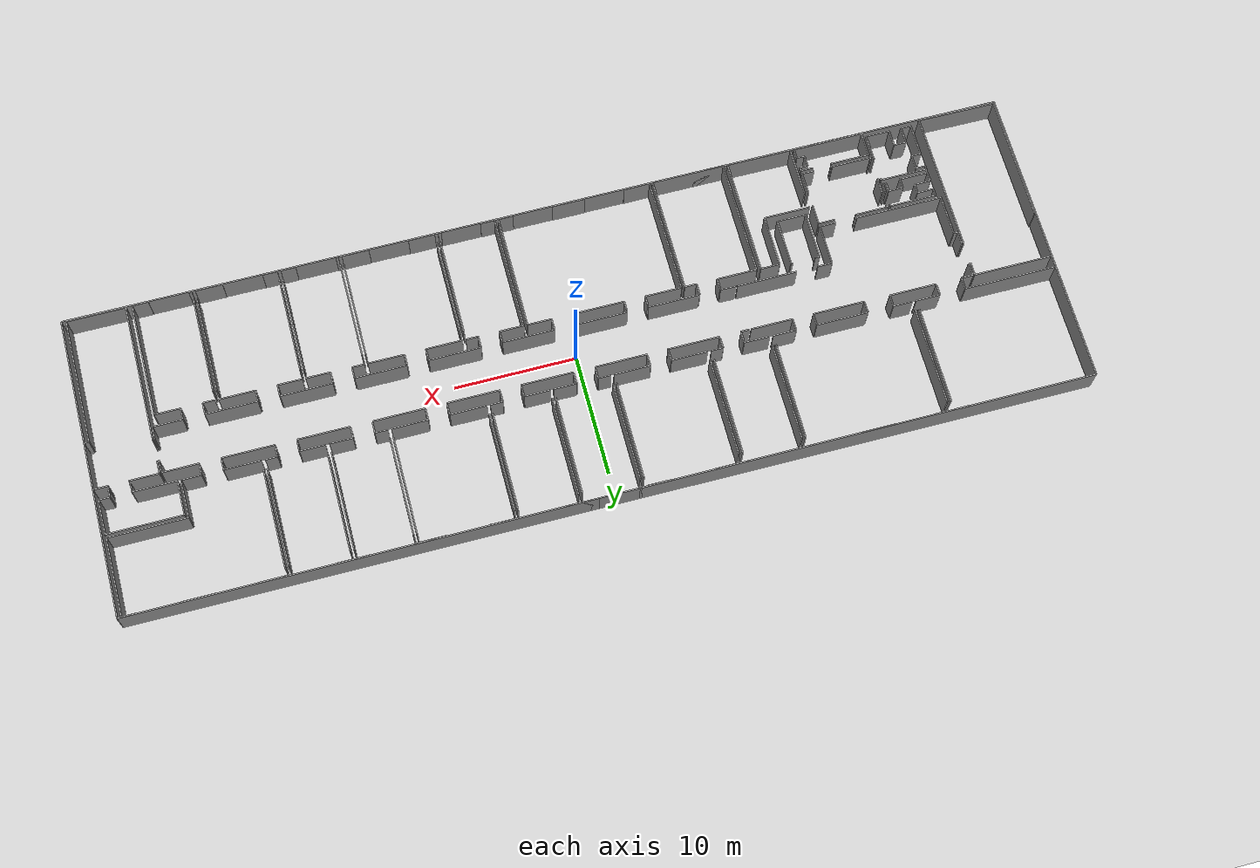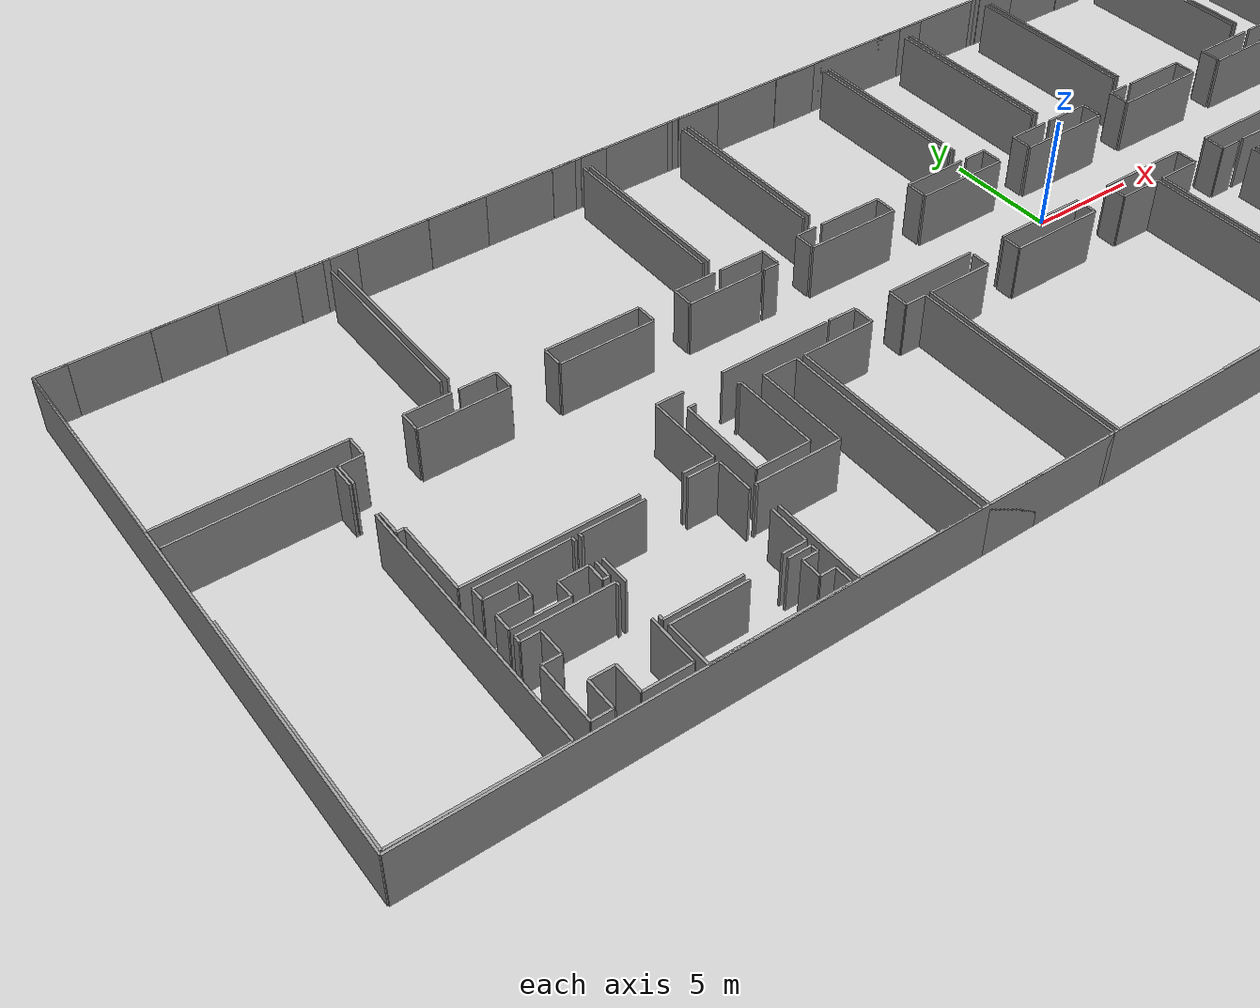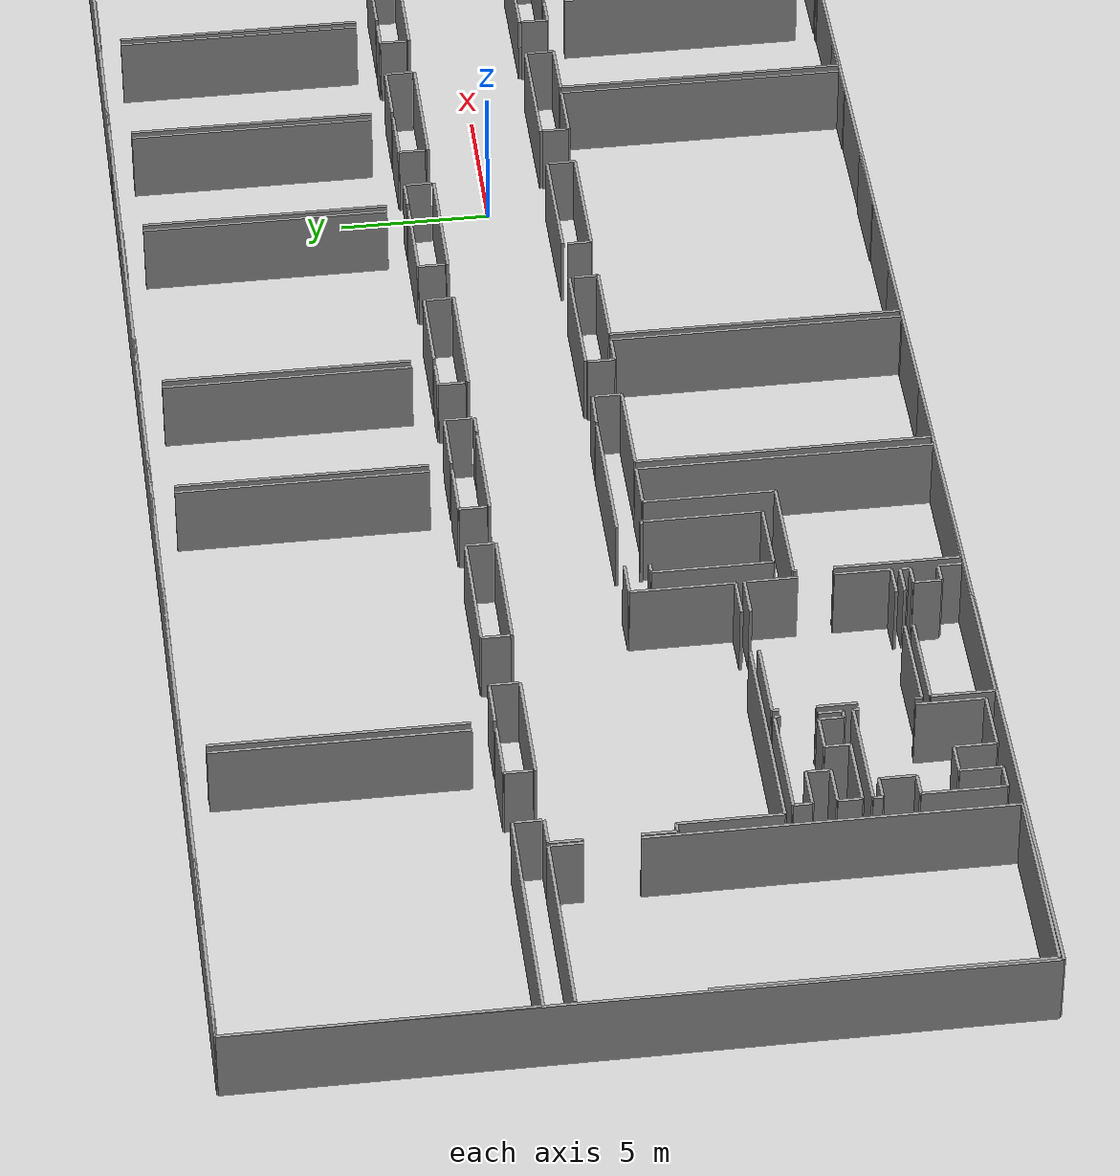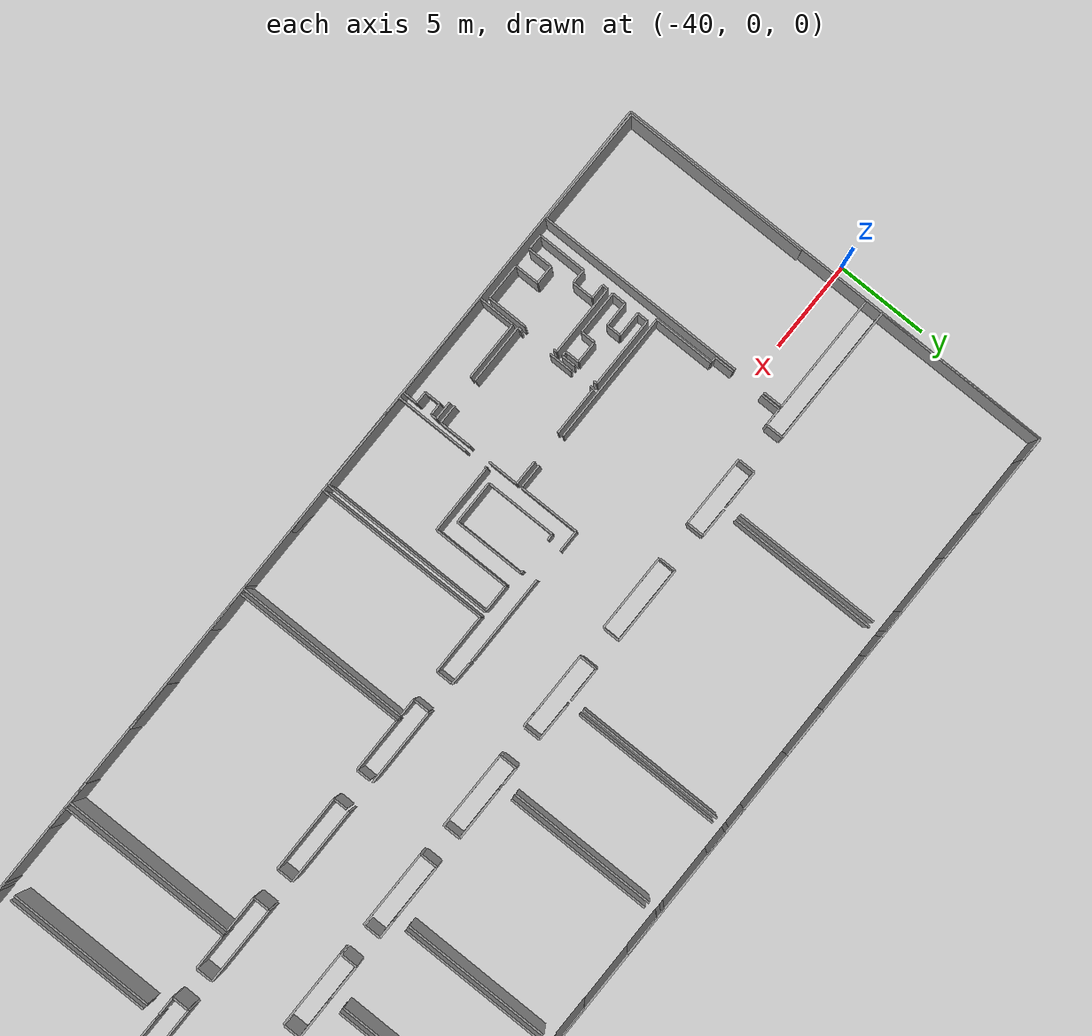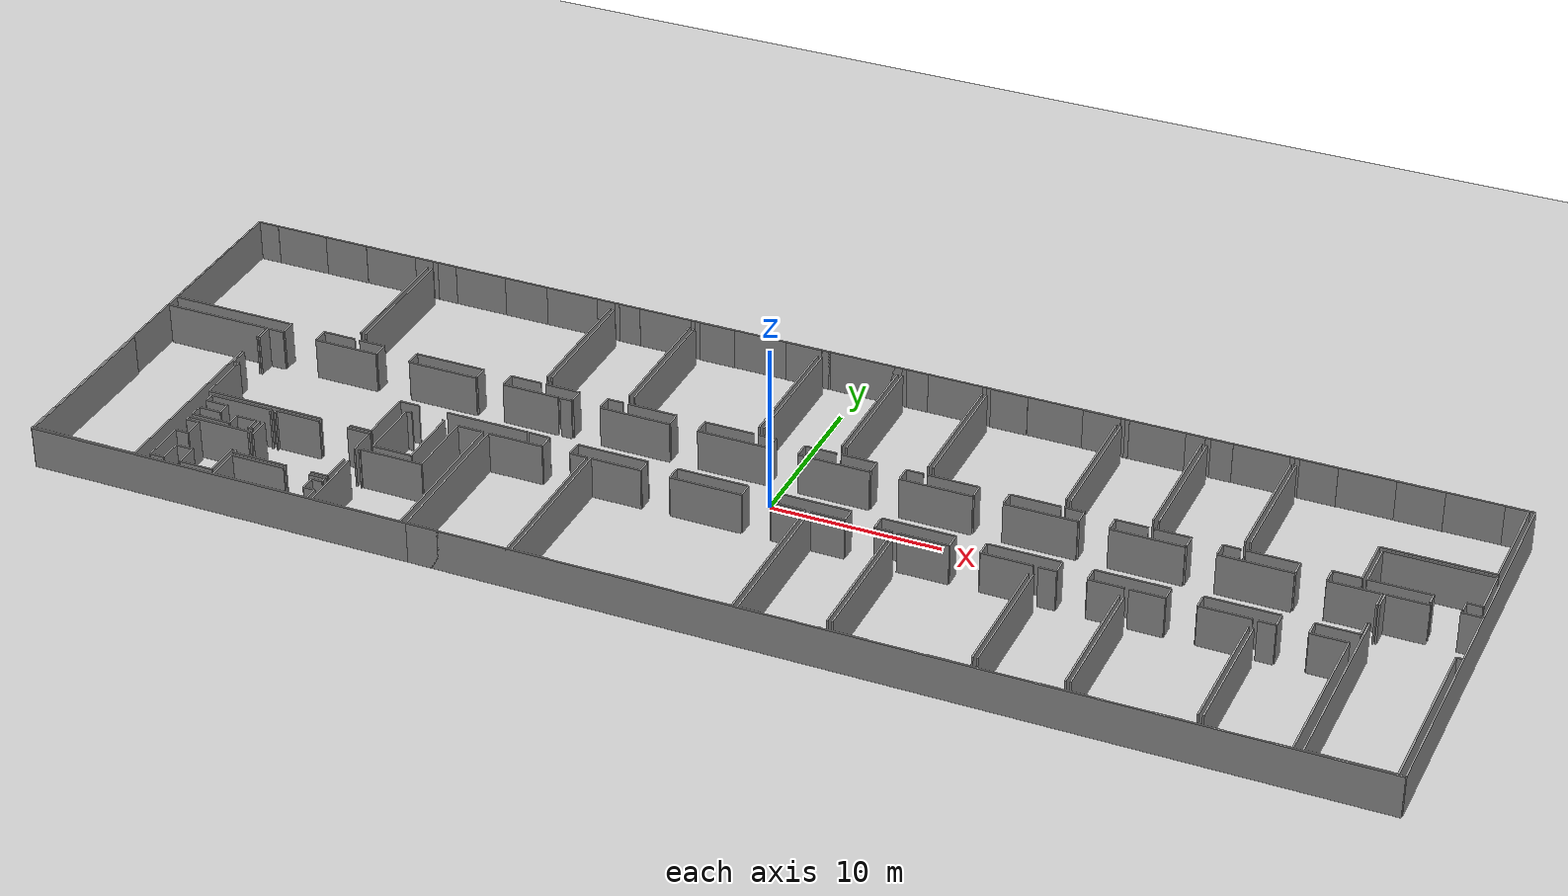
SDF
<sdf version="1.6">
  <world name="default">
    <light name="sun" type="directional">
      <cast_shadows>1</cast_shadows>
      <pose frame="">0 0 10 0 -0 0</pose>
      <diffuse>0.8 0.8 0.8 1</diffuse>
      <specular>0.1 0.1 0.1 1</specular>
      <attenuation>
        <range>1000</range>
        <constant>0.9</constant>
        <linear>0.01</linear>
        <quadratic>0.001</quadratic>
      </attenuation>
      <direction>-0.5 0.5 -1</direction>
    </light>
    <model name="ground_plane">
      <static>1</static>
      <link name="link">
        <collision name="collision">
          <geometry>
            <plane>
              <normal>0 0 1</normal>
              <size>100 100</size>
            </plane>
          </geometry>
          <surface>
            <friction>
              <ode>
                <mu>100</mu>
                <mu2>50</mu2>
              </ode>
              <torsional>
                <ode />
              </torsional>
            </friction>
            <contact>
              <ode />
            </contact>
            <bounce />
          </surface>
          <max_contacts>10</max_contacts>
        </collision>
        <visual name="visual">
          <cast_shadows>0</cast_shadows>
          <geometry>
            <plane>
              <normal>0 0 1</normal>
              <size>100 100</size>
            </plane>
          </geometry>
          <material>
            <script>
              <uri>file://media/materials/scripts/gazebo.material</uri>
              <name>Gazebo/Grey</name>
            </script>
          </material>
        </visual>
        <self_collide>0</self_collide>
        <kinematic>0</kinematic>
        <gravity>1</gravity>
      </link>
    </model>
    <gravity>0 0 -9.8</gravity>
    <magnetic_field>6e-06 2.3e-05 -4.2e-05</magnetic_field>
    <atmosphere type="adiabatic" />
    <physics default="0" name="default_physics" type="ode">
      <max_step_size>0.001</max_step_size>
      <real_time_factor>1</real_time_factor>
      <real_time_update_rate>1000</real_time_update_rate>
    </physics>
    <scene>
      <ambient>0.4 0.4 0.4 1</ambient>
      <background>0.7 0.7 0.7 1</background>
      <shadows>1</shadows>
    </scene>
    <spherical_coordinates>
      <surface_model>EARTH_WGS84</surface_model>
      <latitude_deg>0</latitude_deg>
      <longitude_deg>0</longitude_deg>
      <elevation>0</elevation>
      <heading_deg>0</heading_deg>
    </spherical_coordinates>
  <model name="50052754">
		<static>1</static>
		<link name="Wall_0">
			<collision name="Wall_0_Collision">
				<geometry>
					<box>
						<size>7.62610542331 0.1 2.5</size>
					</box>
				</geometry>
				<pose frame="">3.81305271165 0 1.25 0 0 0</pose>
			</collision>
			<visual name="Wall_0_Visual">
				<pose frame="">3.81305271165 0 1.25 0 0 0</pose>
				<geometry>
					<box>
						<size>7.62610542331 0.1 2.5</size>
					</box>
				</geometry>
				<material>
					<script>
						<uri>file://media/materials/scripts/gazebo.material</uri>
						<name>Gazebo/Grey</name>
					</script>
					<ambient>1 1 1 1</ambient>
				</material>
			</visual>
			<pose frame="">0.0196519699515 -9.60017750166 0 0 0 0.0</pose>
		</link>
		<link name="Wall_1">
			<collision name="Wall_1_Collision">
				<geometry>
					<box>
						<size>0.898919141653 0.1 2.5</size>
					</box>
				</geometry>
				<pose frame="">0.449459570826 0 1.25 0 0 0</pose>
			</collision>
			<visual name="Wall_1_Visual">
				<pose frame="">0.449459570826 0 1.25 0 0 0</pose>
				<geometry>
					<box>
						<size>0.898919141653 0.1 2.5</size>
					</box>
				</geometry>
				<material>
					<script>
						<uri>file://media/materials/scripts/gazebo.material</uri>
						<name>Gazebo/Grey</name>
					</script>
					<ambient>1 1 1 1</ambient>
				</material>
			</visual>
			<pose frame="">7.64575739326 -9.60017750166 0 0 0 -1.57079632679</pose>
		</link>
		<link name="Wall_2">
			<collision name="Wall_2_Collision">
				<geometry>
					<box>
						<size>0.898919141653 0.1 2.5</size>
					</box>
				</geometry>
				<pose frame="">0.449459570826 0 1.25 0 0 0</pose>
			</collision>
			<visual name="Wall_2_Visual">
				<pose frame="">0.449459570826 0 1.25 0 0 0</pose>
				<geometry>
					<box>
						<size>0.898919141653 0.1 2.5</size>
					</box>
				</geometry>
				<material>
					<script>
						<uri>file://media/materials/scripts/gazebo.material</uri>
						<name>Gazebo/Grey</name>
					</script>
					<ambient>1 1 1 1</ambient>
				</material>
			</visual>
			<pose frame="">9.77691844432 -10.4990966433 0 0 0 1.57079632679</pose>
		</link>
		<link name="Wall_3">
			<collision name="Wall_3_Collision">
				<geometry>
					<box>
						<size>1.99131509715 0.1 2.5</size>
					</box>
				</geometry>
				<pose frame="">0.995657548575 0 1.25 0 0 0</pose>
			</collision>
			<visual name="Wall_3_Visual">
				<pose frame="">0.995657548575 0 1.25 0 0 0</pose>
				<geometry>
					<box>
						<size>1.99131509715 0.1 2.5</size>
					</box>
				</geometry>
				<material>
					<script>
						<uri>file://media/materials/scripts/gazebo.material</uri>
						<name>Gazebo/Grey</name>
					</script>
					<ambient>1 1 1 1</ambient>
				</material>
			</visual>
			<pose frame="">9.77691844432 -9.60017750166 0 0 0 0.0</pose>
		</link>
		<link name="Wall_4">
			<collision name="Wall_4_Collision">
				<geometry>
					<box>
						<size>8.11994041016 0.1 2.5</size>
					</box>
				</geometry>
				<pose frame="">4.05997020508 0 1.25 0 0 0</pose>
			</collision>
			<visual name="Wall_4_Visual">
				<pose frame="">4.05997020508 0 1.25 0 0 0</pose>
				<geometry>
					<box>
						<size>8.11994041016 0.1 2.5</size>
					</box>
				</geometry>
				<material>
					<script>
						<uri>file://media/materials/scripts/gazebo.material</uri>
						<name>Gazebo/Grey</name>
					</script>
					<ambient>1 1 1 1</ambient>
				</material>
			</visual>
			<pose frame="">11.7682335415 -8.86494025167 0 0 0 1.57079632679</pose>
		</link>
		<link name="Wall_5">
			<collision name="Wall_5_Collision">
				<geometry>
					<box>
						<size>1.19598085518 0.1 2.5</size>
					</box>
				</geometry>
				<pose frame="">0.597990427589 0 1.25 0 0 0</pose>
			</collision>
			<visual name="Wall_5_Visual">
				<pose frame="">0.597990427589 0 1.25 0 0 0</pose>
				<geometry>
					<box>
						<size>1.19598085518 0.1 2.5</size>
					</box>
				</geometry>
				<material>
					<script>
						<uri>file://media/materials/scripts/gazebo.material</uri>
						<name>Gazebo/Grey</name>
					</script>
					<ambient>1 1 1 1</ambient>
				</material>
			</visual>
			<pose frame="">11.7682335415 -0.00621255824273 0 0 0 3.14159265359</pose>
		</link>
		<link name="Wall_6">
			<collision name="Wall_6_Collision">
				<geometry>
					<box>
						<size>2.73111667565 0.1 2.5</size>
					</box>
				</geometry>
				<pose frame="">1.36555833782 0 1.25 0 0 0</pose>
			</collision>
			<visual name="Wall_6_Visual">
				<pose frame="">1.36555833782 0 1.25 0 0 0</pose>
				<geometry>
					<box>
						<size>2.73111667565 0.1 2.5</size>
					</box>
				</geometry>
				<material>
					<script>
						<uri>file://media/materials/scripts/gazebo.material</uri>
						<name>Gazebo/Grey</name>
					</script>
					<ambient>1 1 1 1</ambient>
				</material>
			</visual>
			<pose frame="">7.28783796634 -0.00621255824273 0 0 0 3.14159265359</pose>
		</link>
		<link name="Wall_7">
			<collision name="Wall_7_Collision">
				<geometry>
					<box>
						<size>1.3012139846 0.1 2.5</size>
					</box>
				</geometry>
				<pose frame="">0.650606992298 0 1.25 0 0 0</pose>
			</collision>
			<visual name="Wall_7_Visual">
				<pose frame="">0.650606992298 0 1.25 0 0 0</pose>
				<geometry>
					<box>
						<size>1.3012139846 0.1 2.5</size>
					</box>
				</geometry>
				<material>
					<script>
						<uri>file://media/materials/scripts/gazebo.material</uri>
						<name>Gazebo/Grey</name>
					</script>
					<ambient>1 1 1 1</ambient>
				</material>
			</visual>
			<pose frame="">1.3012139846 -0.00621255824273 0 0 0 3.14159265359</pose>
		</link>
		<link name="Wall_8">
			<collision name="Wall_8_Collision">
				<geometry>
					<box>
						<size>9.59398507063 0.1 2.5</size>
					</box>
				</geometry>
				<pose frame="">4.79699253532 0 1.25 0 0 0</pose>
			</collision>
			<visual name="Wall_8_Visual">
				<pose frame="">4.79699253532 0 1.25 0 0 0</pose>
				<geometry>
					<box>
						<size>9.59398507063 0.1 2.5</size>
					</box>
				</geometry>
				<material>
					<script>
						<uri>file://media/materials/scripts/gazebo.material</uri>
						<name>Gazebo/Grey</name>
					</script>
					<ambient>1 1 1 1</ambient>
				</material>
			</visual>
			<pose frame="">0.0 -0.00621255824273 0 0 0 -1.56874796175</pose>
		</link>
		<link name="Wall_9">
			<collision name="Wall_9_Collision">
				<geometry>
					<box>
						<size>8.12982978858 0.1 2.5</size>
					</box>
				</geometry>
				<pose frame="">4.06491489429 0 1.25 0 0 0</pose>
			</collision>
			<visual name="Wall_9_Visual">
				<pose frame="">4.06491489429 0 1.25 0 0 0</pose>
				<geometry>
					<box>
						<size>8.12982978858 0.1 2.5</size>
					</box>
				</geometry>
				<material>
					<script>
						<uri>file://media/materials/scripts/gazebo.material</uri>
						<name>Gazebo/Grey</name>
					</script>
					<ambient>1 1 1 1</ambient>
				</material>
			</visual>
			<pose frame="">12.0749310596 -8.86798313734 0 0 0 1.57079632679</pose>
		</link>
		<link name="Wall_10">
			<collision name="Wall_10_Collision">
				<geometry>
					<box>
						<size>1.21106849662 0.1 2.5</size>
					</box>
				</geometry>
				<pose frame="">0.605534248312 0 1.25 0 0 0</pose>
			</collision>
			<visual name="Wall_10_Visual">
				<pose frame="">0.605534248312 0 1.25 0 0 0</pose>
				<geometry>
					<box>
						<size>1.21106849662 0.1 2.5</size>
					</box>
				</geometry>
				<material>
					<script>
						<uri>file://media/materials/scripts/gazebo.material</uri>
						<name>Gazebo/Grey</name>
					</script>
					<ambient>1 1 1 1</ambient>
				</material>
			</visual>
			<pose frame="">12.0749310596 -0.00456432850487 0 0 0 0.0</pose>
		</link>
		<link name="Wall_11">
			<collision name="Wall_11_Collision">
				<geometry>
					<box>
						<size>2.72718628166 0.1 2.5</size>
					</box>
				</geometry>
				<pose frame="">1.36359314083 0 1.25 0 0 0</pose>
			</collision>
			<visual name="Wall_11_Visual">
				<pose frame="">1.36359314083 0 1.25 0 0 0</pose>
				<geometry>
					<box>
						<size>2.72718628166 0.1 2.5</size>
					</box>
				</geometry>
				<material>
					<script>
						<uri>file://media/materials/scripts/gazebo.material</uri>
						<name>Gazebo/Grey</name>
					</script>
					<ambient>1 1 1 1</ambient>
				</material>
			</visual>
			<pose frame="">16.535421091 -0.00456432850487 0 0 0 0.0</pose>
		</link>
		<link name="Wall_12">
			<collision name="Wall_12_Collision">
				<geometry>
					<box>
						<size>1.14437858569 0.1 2.5</size>
					</box>
				</geometry>
				<pose frame="">0.572189292846 0 1.25 0 0 0</pose>
			</collision>
			<visual name="Wall_12_Visual">
				<pose frame="">0.572189292846 0 1.25 0 0 0</pose>
				<geometry>
					<box>
						<size>1.14437858569 0.1 2.5</size>
					</box>
				</geometry>
				<material>
					<script>
						<uri>file://media/materials/scripts/gazebo.material</uri>
						<name>Gazebo/Grey</name>
					</script>
					<ambient>1 1 1 1</ambient>
				</material>
			</visual>
			<pose frame="">22.520396843 -0.00456432850487 0 0 0 0.0</pose>
		</link>
		<link name="Wall_13">
			<collision name="Wall_13_Collision">
				<geometry>
					<box>
						<size>8.13198516593 0.1 2.5</size>
					</box>
				</geometry>
				<pose frame="">4.06599258297 0 1.25 0 0 0</pose>
			</collision>
			<visual name="Wall_13_Visual">
				<pose frame="">4.06599258297 0 1.25 0 0 0</pose>
				<geometry>
					<box>
						<size>8.13198516593 0.1 2.5</size>
					</box>
				</geometry>
				<material>
					<script>
						<uri>file://media/materials/scripts/gazebo.material</uri>
						<name>Gazebo/Grey</name>
					</script>
					<ambient>1 1 1 1</ambient>
				</material>
			</visual>
			<pose frame="">23.6647754287 -0.729024691749 0 0 0 -1.57079632679</pose>
		</link>
		<link name="Wall_14">
			<collision name="Wall_14_Collision">
				<geometry>
					<box>
						<size>1.9021839044 0.1 2.5</size>
					</box>
				</geometry>
				<pose frame="">0.951091952201 0 1.25 0 0 0</pose>
			</collision>
			<visual name="Wall_14_Visual">
				<pose frame="">0.951091952201 0 1.25 0 0 0</pose>
				<geometry>
					<box>
						<size>1.9021839044 0.1 2.5</size>
					</box>
				</geometry>
				<material>
					<script>
						<uri>file://media/materials/scripts/gazebo.material</uri>
						<name>Gazebo/Grey</name>
					</script>
					<ambient>1 1 1 1</ambient>
				</material>
			</visual>
			<pose frame="">23.6647754287 -9.58597736854 0 0 0 3.14159265359</pose>
		</link>
		<link name="Wall_15">
			<collision name="Wall_15_Collision">
				<geometry>
					<box>
						<size>0.907413864148 0.1 2.5</size>
					</box>
				</geometry>
				<pose frame="">0.453706932074 0 1.25 0 0 0</pose>
			</collision>
			<visual name="Wall_15_Visual">
				<pose frame="">0.453706932074 0 1.25 0 0 0</pose>
				<geometry>
					<box>
						<size>0.907413864148 0.1 2.5</size>
					</box>
				</geometry>
				<material>
					<script>
						<uri>file://media/materials/scripts/gazebo.material</uri>
						<name>Gazebo/Grey</name>
					</script>
					<ambient>1 1 1 1</ambient>
				</material>
			</visual>
			<pose frame="">21.7625915243 -9.58597736854 0 0 0 -1.57079632679</pose>
		</link>
		<link name="Wall_16">
			<collision name="Wall_16_Collision">
				<geometry>
					<box>
						<size>0.890170845352 0.1 2.5</size>
					</box>
				</geometry>
				<pose frame="">0.445085422676 0 1.25 0 0 0</pose>
			</collision>
			<visual name="Wall_16_Visual">
				<pose frame="">0.445085422676 0 1.25 0 0 0</pose>
				<geometry>
					<box>
						<size>0.890170845352 0.1 2.5</size>
					</box>
				</geometry>
				<material>
					<script>
						<uri>file://media/materials/scripts/gazebo.material</uri>
						<name>Gazebo/Grey</name>
					</script>
					<ambient>1 1 1 1</ambient>
				</material>
			</visual>
			<pose frame="">20.0465307934 -10.4933912327 0 0 0 1.57079632679</pose>
		</link>
		<link name="Wall_17">
			<collision name="Wall_17_Collision">
				<geometry>
					<box>
						<size>4.25547560937 0.1 2.5</size>
					</box>
				</geometry>
				<pose frame="">2.12773780468 0 1.25 0 0 0</pose>
			</collision>
			<visual name="Wall_17_Visual">
				<pose frame="">2.12773780468 0 1.25 0 0 0</pose>
				<geometry>
					<box>
						<size>4.25547560937 0.1 2.5</size>
					</box>
				</geometry>
				<material>
					<script>
						<uri>file://media/materials/scripts/gazebo.material</uri>
						<name>Gazebo/Grey</name>
					</script>
					<ambient>1 1 1 1</ambient>
				</material>
			</visual>
			<pose frame="">20.0465307934 -9.60322038733 0 0 0 3.14159265359</pose>
		</link>
		<link name="Wall_18">
			<collision name="Wall_18_Collision">
				<geometry>
					<box>
						<size>0.916035373546 0.1 2.5</size>
					</box>
				</geometry>
				<pose frame="">0.458017686773 0 1.25 0 0 0</pose>
			</collision>
			<visual name="Wall_18_Visual">
				<pose frame="">0.458017686773 0 1.25 0 0 0</pose>
				<geometry>
					<box>
						<size>0.916035373546 0.1 2.5</size>
					</box>
				</geometry>
				<material>
					<script>
						<uri>file://media/materials/scripts/gazebo.material</uri>
						<name>Gazebo/Grey</name>
					</script>
					<ambient>1 1 1 1</ambient>
				</material>
			</visual>
			<pose frame="">15.791055184 -9.60322038733 0 0 0 -1.57079632679</pose>
		</link>
		<link name="Wall_19">
			<collision name="Wall_19_Collision">
				<geometry>
					<box>
						<size>0.91185140575 0.1 2.5</size>
					</box>
				</geometry>
				<pose frame="">0.455925702875 0 1.25 0 0 0</pose>
			</collision>
			<visual name="Wall_19_Visual">
				<pose frame="">0.455925702875 0 1.25 0 0 0</pose>
				<geometry>
					<box>
						<size>0.91185140575 0.1 2.5</size>
					</box>
				</geometry>
				<material>
					<script>
						<uri>file://media/materials/scripts/gazebo.material</uri>
						<name>Gazebo/Grey</name>
					</script>
					<ambient>1 1 1 1</ambient>
				</material>
			</visual>
			<pose frame="">13.6631905924 -10.5192557609 0 0 0 1.57079632679</pose>
		</link>
		<link name="Wall_20">
			<collision name="Wall_20_Collision">
				<geometry>
					<box>
						<size>1.58827597442 0.1 2.5</size>
					</box>
				</geometry>
				<pose frame="">0.794137987208 0 1.25 0 0 0</pose>
			</collision>
			<visual name="Wall_20_Visual">
				<pose frame="">0.794137987208 0 1.25 0 0 0</pose>
				<geometry>
					<box>
						<size>1.58827597442 0.1 2.5</size>
					</box>
				</geometry>
				<material>
					<script>
						<uri>file://media/materials/scripts/gazebo.material</uri>
						<name>Gazebo/Grey</name>
					</script>
					<ambient>1 1 1 1</ambient>
				</material>
			</visual>
			<pose frame="">13.6631905924 -9.60740435513 0 0 0 3.13704251336</pose>
		</link>
		<link name="Wall_21">
			<collision name="Wall_21_Collision">
				<geometry>
					<box>
						<size>10.435576405 0.1 2.5</size>
					</box>
				</geometry>
				<pose frame="">5.21778820248 0 1.25 0 0 0</pose>
			</collision>
			<visual name="Wall_21_Visual">
				<pose frame="">5.21778820248 0 1.25 0 0 0</pose>
				<geometry>
					<box>
						<size>10.435576405 0.1 2.5</size>
					</box>
				</geometry>
				<material>
					<script>
						<uri>file://media/materials/scripts/gazebo.material</uri>
						<name>Gazebo/Grey</name>
					</script>
					<ambient>1 1 1 1</ambient>
				</material>
			</visual>
			<pose frame="">0.0877365368157 -24.9205997021 0 0 0 1.57079632679</pose>
		</link>
		<link name="Wall_22">
			<collision name="Wall_22_Collision">
				<geometry>
					<box>
						<size>6.44077466798 0.1 2.5</size>
					</box>
				</geometry>
				<pose frame="">3.22038733399 0 1.25 0 0 0</pose>
			</collision>
			<visual name="Wall_22_Visual">
				<pose frame="">3.22038733399 0 1.25 0 0 0</pose>
				<geometry>
					<box>
						<size>6.44077466798 0.1 2.5</size>
					</box>
				</geometry>
				<material>
					<script>
						<uri>file://media/materials/scripts/gazebo.material</uri>
						<name>Gazebo/Grey</name>
					</script>
					<ambient>1 1 1 1</ambient>
				</material>
			</visual>
			<pose frame="">0.0877365368157 -10.5570382579 0 0 0 0.0</pose>
		</link>
		<link name="Wall_23">
			<collision name="Wall_23_Collision">
				<geometry>
					<box>
						<size>1.06868680465 0.1 2.5</size>
					</box>
				</geometry>
				<pose frame="">0.534343402327 0 1.25 0 0 0</pose>
			</collision>
			<visual name="Wall_23_Visual">
				<pose frame="">0.534343402327 0 1.25 0 0 0</pose>
				<geometry>
					<box>
						<size>1.06868680465 0.1 2.5</size>
					</box>
				</geometry>
				<material>
					<script>
						<uri>file://media/materials/scripts/gazebo.material</uri>
						<name>Gazebo/Grey</name>
					</script>
					<ambient>1 1 1 1</ambient>
				</material>
			</visual>
			<pose frame="">6.52851120479 -10.5570382579 0 0 0 -1.57079632679</pose>
		</link>
		<link name="Wall_24">
			<collision name="Wall_24_Collision">
				<geometry>
					<box>
						<size>11.5982123047 0.1 2.5</size>
					</box>
				</geometry>
				<pose frame="">5.79910615233 0 1.25 0 0 0</pose>
			</collision>
			<visual name="Wall_24_Visual">
				<pose frame="">5.79910615233 0 1.25 0 0 0</pose>
				<geometry>
					<box>
						<size>11.5982123047 0.1 2.5</size>
					</box>
				</geometry>
				<material>
					<script>
						<uri>file://media/materials/scripts/gazebo.material</uri>
						<name>Gazebo/Grey</name>
					</script>
					<ambient>1 1 1 1</ambient>
				</material>
			</visual>
			<pose frame="">6.52851120479 -13.3700592729 0 0 0 -1.57079632679</pose>
		</link>
		<link name="Wall_25">
			<collision name="Wall_25_Collision">
				<geometry>
					<box>
						<size>6.44095108904 0.1 2.5</size>
					</box>
				</geometry>
				<pose frame="">3.22047554452 0 1.25 0 0 0</pose>
			</collision>
			<visual name="Wall_25_Visual">
				<pose frame="">3.22047554452 0 1.25 0 0 0</pose>
				<geometry>
					<box>
						<size>6.44095108904 0.1 2.5</size>
					</box>
				</geometry>
				<material>
					<script>
						<uri>file://media/materials/scripts/gazebo.material</uri>
						<name>Gazebo/Grey</name>
					</script>
					<ambient>1 1 1 1</ambient>
				</material>
			</visual>
			<pose frame="">6.52851120479 -24.9682715775 0 0 0 3.13419121394</pose>
		</link>
		<link name="Wall_26">
			<collision name="Wall_26_Collision">
				<geometry>
					<box>
						<size>3.30837744461 0.1 2.5</size>
					</box>
				</geometry>
				<pose frame="">1.6541887223 0 1.25 0 0 0</pose>
			</collision>
			<visual name="Wall_26_Visual">
				<pose frame="">1.6541887223 0 1.25 0 0 0</pose>
				<geometry>
					<box>
						<size>3.30837744461 0.1 2.5</size>
					</box>
				</geometry>
				<material>
					<script>
						<uri>file://media/materials/scripts/gazebo.material</uri>
						<name>Gazebo/Grey</name>
					</script>
					<ambient>1 1 1 1</ambient>
				</material>
			</visual>
			<pose frame="">6.9903958921 -17.7928935941 0 0 0 1.57079632679</pose>
		</link>
		<link name="Wall_27">
			<collision name="Wall_27_Collision">
				<geometry>
					<box>
						<size>0.326983422612 0.1 2.5</size>
					</box>
				</geometry>
				<pose frame="">0.163491711306 0 1.25 0 0 0</pose>
			</collision>
			<visual name="Wall_27_Visual">
				<pose frame="">0.163491711306 0 1.25 0 0 0</pose>
				<geometry>
					<box>
						<size>0.326983422612 0.1 2.5</size>
					</box>
				</geometry>
				<material>
					<script>
						<uri>file://media/materials/scripts/gazebo.material</uri>
						<name>Gazebo/Grey</name>
					</script>
					<ambient>1 1 1 1</ambient>
				</material>
			</visual>
			<pose frame="">6.9903958921 -14.4845161495 0 0 0 3.14159265359</pose>
		</link>
		<link name="Wall_28">
			<collision name="Wall_28_Collision">
				<geometry>
					<box>
						<size>1.09708707091 0.1 2.5</size>
					</box>
				</geometry>
				<pose frame="">0.548543535453 0 1.25 0 0 0</pose>
			</collision>
			<visual name="Wall_28_Visual">
				<pose frame="">0.548543535453 0 1.25 0 0 0</pose>
				<geometry>
					<box>
						<size>1.09708707091 0.1 2.5</size>
					</box>
				</geometry>
				<material>
					<script>
						<uri>file://media/materials/scripts/gazebo.material</uri>
						<name>Gazebo/Grey</name>
					</script>
					<ambient>1 1 1 1</ambient>
				</material>
			</visual>
			<pose frame="">6.66341246949 -14.4845161495 0 0 0 1.57079632679</pose>
		</link>
		<link name="Wall_29">
			<collision name="Wall_29_Collision">
				<geometry>
					<box>
						<size>1.06767250943 0.1 2.5</size>
					</box>
				</geometry>
				<pose frame="">0.533836254715 0 1.25 0 0 0</pose>
			</collision>
			<visual name="Wall_29_Visual">
				<pose frame="">0.533836254715 0 1.25 0 0 0</pose>
				<geometry>
					<box>
						<size>1.06767250943 0.1 2.5</size>
					</box>
				</geometry>
				<material>
					<script>
						<uri>file://media/materials/scripts/gazebo.material</uri>
						<name>Gazebo/Grey</name>
					</script>
					<ambient>1 1 1 1</ambient>
				</material>
			</visual>
			<pose frame="">6.66341246949 -11.6342197851 0 0 0 1.57079632679</pose>
		</link>
		<link name="Wall_30">
			<collision name="Wall_30_Collision">
				<geometry>
					<box>
						<size>0.96801800374 0.1 2.5</size>
					</box>
				</geometry>
				<pose frame="">0.48400900187 0 1.25 0 0 0</pose>
			</collision>
			<visual name="Wall_30_Visual">
				<pose frame="">0.48400900187 0 1.25 0 0 0</pose>
				<geometry>
					<box>
						<size>0.96801800374 0.1 2.5</size>
					</box>
				</geometry>
				<material>
					<script>
						<uri>file://media/materials/scripts/gazebo.material</uri>
						<name>Gazebo/Grey</name>
					</script>
					<ambient>1 1 1 1</ambient>
				</material>
			</visual>
			<pose frame="">6.66341246949 -10.5665472757 0 0 0 0.0</pose>
		</link>
		<link name="Wall_31">
			<collision name="Wall_31_Collision">
				<geometry>
					<box>
						<size>3.87942565533 0.1 2.5</size>
					</box>
				</geometry>
				<pose frame="">1.93971282766 0 1.25 0 0 0</pose>
			</collision>
			<visual name="Wall_31_Visual">
				<pose frame="">1.93971282766 0 1.25 0 0 0</pose>
				<geometry>
					<box>
						<size>3.87942565533 0.1 2.5</size>
					</box>
				</geometry>
				<material>
					<script>
						<uri>file://media/materials/scripts/gazebo.material</uri>
						<name>Gazebo/Grey</name>
					</script>
					<ambient>1 1 1 1</ambient>
				</material>
			</visual>
			<pose frame="">9.7713398206 -10.5665472757 0 0 0 0.0</pose>
		</link>
		<link name="Wall_32">
			<collision name="Wall_32_Collision">
				<geometry>
					<box>
						<size>4.22720213002 0.1 2.5</size>
					</box>
				</geometry>
				<pose frame="">2.11360106501 0 1.25 0 0 0</pose>
			</collision>
			<visual name="Wall_32_Visual">
				<pose frame="">2.11360106501 0 1.25 0 0 0</pose>
				<geometry>
					<box>
						<size>4.22720213002 0.1 2.5</size>
					</box>
				</geometry>
				<material>
					<script>
						<uri>file://media/materials/scripts/gazebo.material</uri>
						<name>Gazebo/Grey</name>
					</script>
					<ambient>1 1 1 1</ambient>
				</material>
			</visual>
			<pose frame="">15.802846366 -10.5665472757 0 0 0 0.0</pose>
		</link>
		<link name="Wall_33">
			<collision name="Wall_33_Collision">
				<geometry>
					<box>
						<size>3.44099654506 0.1 2.5</size>
					</box>
				</geometry>
				<pose frame="">1.72049827253 0 1.25 0 0 0</pose>
			</collision>
			<visual name="Wall_33_Visual">
				<pose frame="">1.72049827253 0 1.25 0 0 0</pose>
				<geometry>
					<box>
						<size>3.44099654506 0.1 2.5</size>
					</box>
				</geometry>
				<material>
					<script>
						<uri>file://media/materials/scripts/gazebo.material</uri>
						<name>Gazebo/Grey</name>
					</script>
					<ambient>1 1 1 1</ambient>
				</material>
			</visual>
			<pose frame="">21.7524485721 -10.5665472757 0 0 0 0.0</pose>
		</link>
		<link name="Wall_34">
			<collision name="Wall_34_Collision">
				<geometry>
					<box>
						<size>4.93429268757 0.1 2.5</size>
					</box>
				</geometry>
				<pose frame="">2.46714634378 0 1.25 0 0 0</pose>
			</collision>
			<visual name="Wall_34_Visual">
				<pose frame="">2.46714634378 0 1.25 0 0 0</pose>
				<geometry>
					<box>
						<size>4.93429268757 0.1 2.5</size>
					</box>
				</geometry>
				<material>
					<script>
						<uri>file://media/materials/scripts/gazebo.material</uri>
						<name>Gazebo/Grey</name>
					</script>
					<ambient>1 1 1 1</ambient>
				</material>
			</visual>
			<pose frame="">25.1934451171 -14.4353228312 0 0 0 3.14159265359</pose>
		</link>
		<link name="Wall_35">
			<collision name="Wall_35_Collision">
				<geometry>
					<box>
						<size>1.2011791182 0.1 2.5</size>
					</box>
				</geometry>
				<pose frame="">0.600589559099 0 1.25 0 0 0</pose>
			</collision>
			<visual name="Wall_35_Visual">
				<pose frame="">0.600589559099 0 1.25 0 0 0</pose>
				<geometry>
					<box>
						<size>1.2011791182 0.1 2.5</size>
					</box>
				</geometry>
				<material>
					<script>
						<uri>file://media/materials/scripts/gazebo.material</uri>
						<name>Gazebo/Grey</name>
					</script>
					<ambient>1 1 1 1</ambient>
				</material>
			</visual>
			<pose frame="">18.4888269042 -14.4353228312 0 0 0 3.14159265359</pose>
		</link>
		<link name="Wall_36">
			<collision name="Wall_36_Collision">
				<geometry>
					<box>
						<size>3.34970997496 0.1 2.5</size>
					</box>
				</geometry>
				<pose frame="">1.67485498748 0 1.25 0 0 0</pose>
			</collision>
			<visual name="Wall_36_Visual">
				<pose frame="">1.67485498748 0 1.25 0 0 0</pose>
				<geometry>
					<box>
						<size>3.34970997496 0.1 2.5</size>
					</box>
				</geometry>
				<material>
					<script>
						<uri>file://media/materials/scripts/gazebo.material</uri>
						<name>Gazebo/Grey</name>
					</script>
					<ambient>1 1 1 1</ambient>
				</material>
			</visual>
			<pose frame="">17.287647786 -14.4353228312 0 0 0 -1.57079632679</pose>
		</link>
		<link name="Wall_37">
			<collision name="Wall_37_Collision">
				<geometry>
					<box>
						<size>1.34520903991 0.1 2.5</size>
					</box>
				</geometry>
				<pose frame="">0.672604519953 0 1.25 0 0 0</pose>
			</collision>
			<visual name="Wall_37_Visual">
				<pose frame="">0.672604519953 0 1.25 0 0 0</pose>
				<geometry>
					<box>
						<size>1.34520903991 0.1 2.5</size>
					</box>
				</geometry>
				<material>
					<script>
						<uri>file://media/materials/scripts/gazebo.material</uri>
						<name>Gazebo/Grey</name>
					</script>
					<ambient>1 1 1 1</ambient>
				</material>
			</visual>
			<pose frame="">17.287647786 -17.7850328061 0 0 0 3.14159265359</pose>
		</link>
		<link name="Wall_38">
			<collision name="Wall_38_Collision">
				<geometry>
					<box>
						<size>7.16105537787 0.1 2.5</size>
					</box>
				</geometry>
				<pose frame="">3.58052768894 0 1.25 0 0 0</pose>
			</collision>
			<visual name="Wall_38_Visual">
				<pose frame="">3.58052768894 0 1.25 0 0 0</pose>
				<geometry>
					<box>
						<size>7.16105537787 0.1 2.5</size>
					</box>
				</geometry>
				<material>
					<script>
						<uri>file://media/materials/scripts/gazebo.material</uri>
						<name>Gazebo/Grey</name>
					</script>
					<ambient>1 1 1 1</ambient>
				</material>
			</visual>
			<pose frame="">14.1514469555 -17.7850328061 0 0 0 -3.14049493976</pose>
		</link>
		<link name="Wall_39">
			<collision name="Wall_39_Collision">
				<geometry>
					<box>
						<size>3.87283273638 0.1 2.5</size>
					</box>
				</geometry>
				<pose frame="">1.93641636819 0 1.25 0 0 0</pose>
			</collision>
			<visual name="Wall_39_Visual">
				<pose frame="">1.93641636819 0 1.25 0 0 0</pose>
				<geometry>
					<box>
						<size>3.87283273638 0.1 2.5</size>
					</box>
				</geometry>
				<material>
					<script>
						<uri>file://media/materials/scripts/gazebo.material</uri>
						<name>Gazebo/Grey</name>
					</script>
					<ambient>1 1 1 1</ambient>
				</material>
			</visual>
			<pose frame="">18.1016197027 -19.1108434499 0 0 0 1.57079632679</pose>
		</link>
		<link name="Wall_40">
			<collision name="Wall_40_Collision">
				<geometry>
					<box>
						<size>0.355256901962 0.1 2.5</size>
					</box>
				</geometry>
				<pose frame="">0.177628450981 0 1.25 0 0 0</pose>
			</collision>
			<visual name="Wall_40_Visual">
				<pose frame="">0.177628450981 0 1.25 0 0 0</pose>
				<geometry>
					<box>
						<size>0.355256901962 0.1 2.5</size>
					</box>
				</geometry>
				<material>
					<script>
						<uri>file://media/materials/scripts/gazebo.material</uri>
						<name>Gazebo/Grey</name>
					</script>
					<ambient>1 1 1 1</ambient>
				</material>
			</visual>
			<pose frame="">18.1016197027 -15.2380107135 0 0 0 0.0</pose>
		</link>
		<link name="Wall_41">
			<collision name="Wall_41_Collision">
				<geometry>
					<box>
						<size>0.140860249136 0.1 2.5</size>
					</box>
				</geometry>
				<pose frame="">0.0704301245681 0 1.25 0 0 0</pose>
			</collision>
			<visual name="Wall_41_Visual">
				<pose frame="">0.0704301245681 0 1.25 0 0 0</pose>
				<geometry>
					<box>
						<size>0.140860249136 0.1 2.5</size>
					</box>
				</geometry>
				<material>
					<script>
						<uri>file://media/materials/scripts/gazebo.material</uri>
						<name>Gazebo/Grey</name>
					</script>
					<ambient>1 1 1 1</ambient>
				</material>
			</visual>
			<pose frame="">20.3361120796 -15.2380107135 0 0 0 0.0</pose>
		</link>
		<link name="Wall_42">
			<collision name="Wall_42_Collision">
				<geometry>
					<box>
						<size>3.86700053884 0.1 2.5</size>
					</box>
				</geometry>
				<pose frame="">1.93350026942 0 1.25 0 0 0</pose>
			</collision>
			<visual name="Wall_42_Visual">
				<pose frame="">1.93350026942 0 1.25 0 0 0</pose>
				<geometry>
					<box>
						<size>3.86700053884 0.1 2.5</size>
					</box>
				</geometry>
				<material>
					<script>
						<uri>file://media/materials/scripts/gazebo.material</uri>
						<name>Gazebo/Grey</name>
					</script>
					<ambient>1 1 1 1</ambient>
				</material>
			</visual>
			<pose frame="">20.4769723288 -15.2380107135 0 0 0 -1.57079632679</pose>
		</link>
		<link name="Wall_43">
			<collision name="Wall_43_Collision">
				<geometry>
					<box>
						<size>2.37535978595 0.1 2.5</size>
					</box>
				</geometry>
				<pose frame="">1.18767989298 0 1.25 0 0 0</pose>
			</collision>
			<visual name="Wall_43_Visual">
				<pose frame="">1.18767989298 0 1.25 0 0 0</pose>
				<geometry>
					<box>
						<size>2.37535978595 0.1 2.5</size>
					</box>
				</geometry>
				<material>
					<script>
						<uri>file://media/materials/scripts/gazebo.material</uri>
						<name>Gazebo/Grey</name>
					</script>
					<ambient>1 1 1 1</ambient>
				</material>
			</visual>
			<pose frame="">20.4769723288 -19.1050112523 0 0 0 -3.13913736095</pose>
		</link>
		<link name="Wall_44">
			<collision name="Wall_44_Collision">
				<geometry>
					<box>
						<size>3.26945386542 0.1 2.5</size>
					</box>
				</geometry>
				<pose frame="">1.63472693271 0 1.25 0 0 0</pose>
			</collision>
			<visual name="Wall_44_Visual">
				<pose frame="">1.63472693271 0 1.25 0 0 0</pose>
				<geometry>
					<box>
						<size>3.26945386542 0.1 2.5</size>
					</box>
				</geometry>
				<material>
					<script>
						<uri>file://media/materials/scripts/gazebo.material</uri>
						<name>Gazebo/Grey</name>
					</script>
					<ambient>1 1 1 1</ambient>
				</material>
			</visual>
			<pose frame="">11.4441662176 -22.7137468699 0 0 0 0.0</pose>
		</link>
		<link name="Wall_45">
			<collision name="Wall_45_Collision">
				<geometry>
					<box>
						<size>1.03445434087 0.1 2.5</size>
					</box>
				</geometry>
				<pose frame="">0.517227170433 0 1.25 0 0 0</pose>
			</collision>
			<visual name="Wall_45_Visual">
				<pose frame="">0.517227170433 0 1.25 0 0 0</pose>
				<geometry>
					<box>
						<size>1.03445434087 0.1 2.5</size>
					</box>
				</geometry>
				<material>
					<script>
						<uri>file://media/materials/scripts/gazebo.material</uri>
						<name>Gazebo/Grey</name>
					</script>
					<ambient>1 1 1 1</ambient>
				</material>
			</visual>
			<pose frame="">16.270309677 -22.7137468699 0 0 0 0.0</pose>
		</link>
		<link name="Wall_46">
			<collision name="Wall_46_Collision">
				<geometry>
					<box>
						<size>1.81229199024 0.1 2.5</size>
					</box>
				</geometry>
				<pose frame="">0.906145995119 0 1.25 0 0 0</pose>
			</collision>
			<visual name="Wall_46_Visual">
				<pose frame="">0.906145995119 0 1.25 0 0 0</pose>
				<geometry>
					<box>
						<size>1.81229199024 0.1 2.5</size>
					</box>
				</geometry>
				<material>
					<script>
						<uri>file://media/materials/scripts/gazebo.material</uri>
						<name>Gazebo/Grey</name>
					</script>
					<ambient>1 1 1 1</ambient>
				</material>
			</visual>
			<pose frame="">17.3047640179 -22.7137468699 0 0 0 1.57079632679</pose>
		</link>
		<link name="Wall_47">
			<collision name="Wall_47_Collision">
				<geometry>
					<box>
						<size>1.68930869441 0.1 2.5</size>
					</box>
				</geometry>
				<pose frame="">0.844654347206 0 1.25 0 0 0</pose>
			</collision>
			<visual name="Wall_47_Visual">
				<pose frame="">0.844654347206 0 1.25 0 0 0</pose>
				<geometry>
					<box>
						<size>1.68930869441 0.1 2.5</size>
					</box>
				</geometry>
				<material>
					<script>
						<uri>file://media/materials/scripts/gazebo.material</uri>
						<name>Gazebo/Grey</name>
					</script>
					<ambient>1 1 1 1</ambient>
				</material>
			</visual>
			<pose frame="">17.3047640179 -19.7532726869 0 0 0 1.57079632679</pose>
		</link>
		<link name="Wall_48">
			<collision name="Wall_48_Collision">
				<geometry>
					<box>
						<size>1.36955212527 0.1 2.5</size>
					</box>
				</geometry>
				<pose frame="">0.684776062633 0 1.25 0 0 0</pose>
			</collision>
			<visual name="Wall_48_Visual">
				<pose frame="">0.684776062633 0 1.25 0 0 0</pose>
				<geometry>
					<box>
						<size>1.36955212527 0.1 2.5</size>
					</box>
				</geometry>
				<material>
					<script>
						<uri>file://media/materials/scripts/gazebo.material</uri>
						<name>Gazebo/Grey</name>
					</script>
					<ambient>1 1 1 1</ambient>
				</material>
			</visual>
			<pose frame="">17.3047640179 -18.0639639925 0 0 0 3.14159265359</pose>
		</link>
		<link name="Wall_49">
			<collision name="Wall_49_Collision">
				<geometry>
					<box>
						<size>2.70258962249 0.1 2.5</size>
					</box>
				</geometry>
				<pose frame="">1.35129481125 0 1.25 0 0 0</pose>
			</collision>
			<visual name="Wall_49_Visual">
				<pose frame="">1.35129481125 0 1.25 0 0 0</pose>
				<geometry>
					<box>
						<size>2.70258962249 0.1 2.5</size>
					</box>
				</geometry>
				<material>
					<script>
						<uri>file://media/materials/scripts/gazebo.material</uri>
						<name>Gazebo/Grey</name>
					</script>
					<ambient>1 1 1 1</ambient>
				</material>
			</visual>
			<pose frame="">14.1752828933 -18.0639639925 0 0 0 3.14159265359</pose>
		</link>
		<link name="Wall_50">
			<collision name="Wall_50_Collision">
				<geometry>
					<box>
						<size>0.214523439729 0.1 2.5</size>
					</box>
				</geometry>
				<pose frame="">0.107261719864 0 1.25 0 0 0</pose>
			</collision>
			<visual name="Wall_50_Visual">
				<pose frame="">0.107261719864 0 1.25 0 0 0</pose>
				<geometry>
					<box>
						<size>0.214523439729 0.1 2.5</size>
					</box>
				</geometry>
				<material>
					<script>
						<uri>file://media/materials/scripts/gazebo.material</uri>
						<name>Gazebo/Grey</name>
					</script>
					<ambient>1 1 1 1</ambient>
				</material>
			</visual>
			<pose frame="">11.4726932708 -18.0639639925 0 0 0 -1.57079632679</pose>
		</link>
		<link name="Wall_51">
			<collision name="Wall_51_Collision">
				<geometry>
					<box>
						<size>1.28904244192 0.1 2.5</size>
					</box>
				</geometry>
				<pose frame="">0.644521220958 0 1.25 0 0 0</pose>
			</collision>
			<visual name="Wall_51_Visual">
				<pose frame="">0.644521220958 0 1.25 0 0 0</pose>
				<geometry>
					<box>
						<size>1.28904244192 0.1 2.5</size>
					</box>
				</geometry>
				<material>
					<script>
						<uri>file://media/materials/scripts/gazebo.material</uri>
						<name>Gazebo/Grey</name>
					</script>
					<ambient>1 1 1 1</ambient>
				</material>
			</visual>
			<pose frame="">11.4726932708 -19.4303464452 0 0 0 -1.57079632679</pose>
		</link>
		<link name="Wall_52">
			<collision name="Wall_52_Collision">
				<geometry>
					<box>
						<size>0.218800034224 0.1 2.5</size>
					</box>
				</geometry>
				<pose frame="">0.109400017112 0 1.25 0 0 0</pose>
			</collision>
			<visual name="Wall_52_Visual">
				<pose frame="">0.109400017112 0 1.25 0 0 0</pose>
				<geometry>
					<box>
						<size>0.218800034224 0.1 2.5</size>
					</box>
				</geometry>
				<material>
					<script>
						<uri>file://media/materials/scripts/gazebo.material</uri>
						<name>Gazebo/Grey</name>
					</script>
					<ambient>1 1 1 1</ambient>
				</material>
			</visual>
			<pose frame="">11.4726932708 -22.4968144791 0 0 0 -1.70154812908</pose>
		</link>
		<link name="Wall_53">
			<collision name="Wall_53_Collision">
				<geometry>
					<box>
						<size>4.07987574884 0.1 2.5</size>
					</box>
				</geometry>
				<pose frame="">2.03993787442 0 1.25 0 0 0</pose>
			</collision>
			<visual name="Wall_53_Visual">
				<pose frame="">2.03993787442 0 1.25 0 0 0</pose>
				<geometry>
					<box>
						<size>4.07987574884 0.1 2.5</size>
					</box>
				</geometry>
				<material>
					<script>
						<uri>file://media/materials/scripts/gazebo.material</uri>
						<name>Gazebo/Grey</name>
					</script>
					<ambient>1 1 1 1</ambient>
				</material>
			</visual>
			<pose frame="">17.6056293385 -25.0041522711 0 0 0 1.57079632679</pose>
		</link>
		<link name="Wall_54">
			<collision name="Wall_54_Collision">
				<geometry>
					<box>
						<size>0.10967067102 0.1 2.5</size>
					</box>
				</geometry>
				<pose frame="">0.0548353355098 0 1.25 0 0 0</pose>
			</collision>
			<visual name="Wall_54_Visual">
				<pose frame="">0.0548353355098 0 1.25 0 0 0</pose>
				<geometry>
					<box>
						<size>0.10967067102 0.1 2.5</size>
					</box>
				</geometry>
				<material>
					<script>
						<uri>file://media/materials/scripts/gazebo.material</uri>
						<name>Gazebo/Grey</name>
					</script>
					<ambient>1 1 1 1</ambient>
				</material>
			</visual>
			<pose frame="">17.6056293385 -19.7656978034 0 0 0 1.57079632679</pose>
		</link>
		<link name="Wall_55">
			<collision name="Wall_55_Collision">
				<geometry>
					<box>
						<size>3.78928016736 0.1 2.5</size>
					</box>
				</geometry>
				<pose frame="">1.89464008368 0 1.25 0 0 0</pose>
			</collision>
			<visual name="Wall_55_Visual">
				<pose frame="">1.89464008368 0 1.25 0 0 0</pose>
				<geometry>
					<box>
						<size>3.78928016736 0.1 2.5</size>
					</box>
				</geometry>
				<material>
					<script>
						<uri>file://media/materials/scripts/gazebo.material</uri>
						<name>Gazebo/Grey</name>
					</script>
					<ambient>1 1 1 1</ambient>
				</material>
			</visual>
			<pose frame="">17.6056293385 -19.6560271324 0 0 0 0.0</pose>
		</link>
		<link name="Wall_56">
			<collision name="Wall_56_Collision">
				<geometry>
					<box>
						<size>4.25167200228 0.1 2.5</size>
					</box>
				</geometry>
				<pose frame="">2.12583600114 0 1.25 0 0 0</pose>
			</collision>
			<visual name="Wall_56_Visual">
				<pose frame="">2.12583600114 0 1.25 0 0 0</pose>
				<geometry>
					<box>
						<size>4.25167200228 0.1 2.5</size>
					</box>
				</geometry>
				<material>
					<script>
						<uri>file://media/materials/scripts/gazebo.material</uri>
						<name>Gazebo/Grey</name>
					</script>
					<ambient>1 1 1 1</ambient>
				</material>
			</visual>
			<pose frame="">21.3949095058 -19.6560271324 0 0 0 1.57079632679</pose>
		</link>
		<link name="Wall_57">
			<collision name="Wall_57_Collision">
				<geometry>
					<box>
						<size>1.56949507116 0.1 2.5</size>
					</box>
				</geometry>
				<pose frame="">0.78474753558 0 1.25 0 0 0</pose>
			</collision>
			<visual name="Wall_57_Visual">
				<pose frame="">0.78474753558 0 1.25 0 0 0</pose>
				<geometry>
					<box>
						<size>1.56949507116 0.1 2.5</size>
					</box>
				</geometry>
				<material>
					<script>
						<uri>file://media/materials/scripts/gazebo.material</uri>
						<name>Gazebo/Grey</name>
					</script>
					<ambient>1 1 1 1</ambient>
				</material>
			</visual>
			<pose frame="">21.3949095058 -15.4043551301 0 0 0 0.0</pose>
		</link>
		<link name="Wall_58">
			<collision name="Wall_58_Collision">
				<geometry>
					<box>
						<size>9.61856160259 0.1 2.5</size>
					</box>
				</geometry>
				<pose frame="">4.80928080129 0 1.25 0 0 0</pose>
			</collision>
			<visual name="Wall_58_Visual">
				<pose frame="">4.80928080129 0 1.25 0 0 0</pose>
				<geometry>
					<box>
						<size>9.61856160259 0.1 2.5</size>
					</box>
				</geometry>
				<material>
					<script>
						<uri>file://media/materials/scripts/gazebo.material</uri>
						<name>Gazebo/Grey</name>
					</script>
					<ambient>1 1 1 1</ambient>
				</material>
			</visual>
			<pose frame="">22.964404577 -15.4043551301 0 0 0 -1.57079632679</pose>
		</link>
		<link name="Wall_59">
			<collision name="Wall_59_Collision">
				<geometry>
					<box>
						<size>5.35880809154 0.1 2.5</size>
					</box>
				</geometry>
				<pose frame="">2.67940404577 0 1.25 0 0 0</pose>
			</collision>
			<visual name="Wall_59_Visual">
				<pose frame="">2.67940404577 0 1.25 0 0 0</pose>
				<geometry>
					<box>
						<size>5.35880809154 0.1 2.5</size>
					</box>
				</geometry>
				<material>
					<script>
						<uri>file://media/materials/scripts/gazebo.material</uri>
						<name>Gazebo/Grey</name>
					</script>
					<ambient>1 1 1 1</ambient>
				</material>
			</visual>
			<pose frame="">22.964404577 -25.0229167327 0 0 0 3.13809103538</pose>
		</link>
		<link name="Wall_60">
			<collision name="Wall_60_Collision">
				<geometry>
					<box>
						<size>2.01832070747 0.1 2.5</size>
					</box>
				</geometry>
				<pose frame="">1.00916035374 0 1.25 0 0 0</pose>
			</collision>
			<visual name="Wall_60_Visual">
				<pose frame="">1.00916035374 0 1.25 0 0 0</pose>
				<geometry>
					<box>
						<size>2.01832070747 0.1 2.5</size>
					</box>
				</geometry>
				<material>
					<script>
						<uri>file://media/materials/scripts/gazebo.material</uri>
						<name>Gazebo/Grey</name>
					</script>
					<ambient>1 1 1 1</ambient>
				</material>
			</visual>
			<pose frame="">11.498557799 -25.0040254842 0 0 0 1.57079632679</pose>
		</link>
		<link name="Wall_61">
			<collision name="Wall_61_Collision">
				<geometry>
					<box>
						<size>3.22558559701 0.1 2.5</size>
					</box>
				</geometry>
				<pose frame="">1.6127927985 0 1.25 0 0 0</pose>
			</collision>
			<visual name="Wall_61_Visual">
				<pose frame="">1.6127927985 0 1.25 0 0 0</pose>
				<geometry>
					<box>
						<size>3.22558559701 0.1 2.5</size>
					</box>
				</geometry>
				<material>
					<script>
						<uri>file://media/materials/scripts/gazebo.material</uri>
						<name>Gazebo/Grey</name>
					</script>
					<ambient>1 1 1 1</ambient>
				</material>
			</visual>
			<pose frame="">11.498557799 -22.9857047767 0 0 0 0.0</pose>
		</link>
		<link name="Wall_62">
			<collision name="Wall_62_Collision">
				<geometry>
					<box>
						<size>0.997559352119 0.1 2.5</size>
					</box>
				</geometry>
				<pose frame="">0.498779676059 0 1.25 0 0 0</pose>
			</collision>
			<visual name="Wall_62_Visual">
				<pose frame="">0.498779676059 0 1.25 0 0 0</pose>
				<geometry>
					<box>
						<size>0.997559352119 0.1 2.5</size>
					</box>
				</geometry>
				<material>
					<script>
						<uri>file://media/materials/scripts/gazebo.material</uri>
						<name>Gazebo/Grey</name>
					</script>
					<ambient>1 1 1 1</ambient>
				</material>
			</visual>
			<pose frame="">16.2917366636 -22.9857047767 0 0 0 0.0</pose>
		</link>
		<link name="Wall_63">
			<collision name="Wall_63_Collision">
				<geometry>
					<box>
						<size>0.326349488098 0.1 2.5</size>
					</box>
				</geometry>
				<pose frame="">0.163174744049 0 1.25 0 0 0</pose>
			</collision>
			<visual name="Wall_63_Visual">
				<pose frame="">0.163174744049 0 1.25 0 0 0</pose>
				<geometry>
					<box>
						<size>0.326349488098 0.1 2.5</size>
					</box>
				</geometry>
				<material>
					<script>
						<uri>file://media/materials/scripts/gazebo.material</uri>
						<name>Gazebo/Grey</name>
					</script>
					<ambient>1 1 1 1</ambient>
				</material>
			</visual>
			<pose frame="">17.2892960157 -22.9857047767 0 0 0 -1.57079632679</pose>
		</link>
		<link name="Wall_64">
			<collision name="Wall_64_Collision">
				<geometry>
					<box>
						<size>0.657643665409 0.1 2.5</size>
					</box>
				</geometry>
				<pose frame="">0.328821832705 0 1.25 0 0 0</pose>
			</collision>
			<visual name="Wall_64_Visual">
				<pose frame="">0.328821832705 0 1.25 0 0 0</pose>
				<geometry>
					<box>
						<size>0.657643665409 0.1 2.5</size>
					</box>
				</geometry>
				<material>
					<script>
						<uri>file://media/materials/scripts/gazebo.material</uri>
						<name>Gazebo/Grey</name>
					</script>
					<ambient>1 1 1 1</ambient>
				</material>
			</visual>
			<pose frame="">17.2892960157 -23.3120542648 0 0 0 3.14159265359</pose>
		</link>
		<link name="Wall_65">
			<collision name="Wall_65_Collision">
				<geometry>
					<box>
						<size>0.882563631177 0.1 2.5</size>
					</box>
				</geometry>
				<pose frame="">0.441281815588 0 1.25 0 0 0</pose>
			</collision>
			<visual name="Wall_65_Visual">
				<pose frame="">0.441281815588 0 1.25 0 0 0</pose>
				<geometry>
					<box>
						<size>0.882563631177 0.1 2.5</size>
					</box>
				</geometry>
				<material>
					<script>
						<uri>file://media/materials/scripts/gazebo.material</uri>
						<name>Gazebo/Grey</name>
					</script>
					<ambient>1 1 1 1</ambient>
				</material>
			</visual>
			<pose frame="">16.6316523503 -23.3120542648 0 0 0 -1.57079632679</pose>
		</link>
		<link name="Wall_66">
			<collision name="Wall_66_Collision">
				<geometry>
					<box>
						<size>0.663222289138 0.1 2.5</size>
					</box>
				</geometry>
				<pose frame="">0.331611144569 0 1.25 0 0 0</pose>
			</collision>
			<visual name="Wall_66_Visual">
				<pose frame="">0.331611144569 0 1.25 0 0 0</pose>
				<geometry>
					<box>
						<size>0.663222289138 0.1 2.5</size>
					</box>
				</geometry>
				<material>
					<script>
						<uri>file://media/materials/scripts/gazebo.material</uri>
						<name>Gazebo/Grey</name>
					</script>
					<ambient>1 1 1 1</ambient>
				</material>
			</visual>
			<pose frame="">16.6316523503 -24.194617896 0 0 0 0.0</pose>
		</link>
		<link name="Wall_67">
			<collision name="Wall_67_Collision">
				<geometry>
					<box>
						<size>0.805730768012 0.1 2.5</size>
					</box>
				</geometry>
				<pose frame="">0.402865384006 0 1.25 0 0 0</pose>
			</collision>
			<visual name="Wall_67_Visual">
				<pose frame="">0.402865384006 0 1.25 0 0 0</pose>
				<geometry>
					<box>
						<size>0.805730768012 0.1 2.5</size>
					</box>
				</geometry>
				<material>
					<script>
						<uri>file://media/materials/scripts/gazebo.material</uri>
						<name>Gazebo/Grey</name>
					</script>
					<ambient>1 1 1 1</ambient>
				</material>
			</visual>
			<pose frame="">17.2948746394 -24.194617896 0 0 0 -1.57079632679</pose>
		</link>
		<link name="Wall_68">
			<collision name="Wall_68_Collision">
				<geometry>
					<box>
						<size>5.79631800664 0.1 2.5</size>
					</box>
				</geometry>
				<pose frame="">2.89815900332 0 1.25 0 0 0</pose>
			</collision>
			<visual name="Wall_68_Visual">
				<pose frame="">2.89815900332 0 1.25 0 0 0</pose>
				<geometry>
					<box>
						<size>5.79631800664 0.1 2.5</size>
					</box>
				</geometry>
				<material>
					<script>
						<uri>file://media/materials/scripts/gazebo.material</uri>
						<name>Gazebo/Grey</name>
					</script>
					<ambient>1 1 1 1</ambient>
				</material>
			</visual>
			<pose frame="">17.2948746394 -25.000348664 0 0 0 -3.14095831634</pose>
		</link>
		<link name="Wall_69">
			<collision name="Wall_69_Collision">
				<geometry>
					<box>
						<size>2.65669276364 0.1 2.5</size>
					</box>
				</geometry>
				<pose frame="">1.32834638182 0 1.25 0 0 0</pose>
			</collision>
			<visual name="Wall_69_Visual">
				<pose frame="">1.32834638182 0 1.25 0 0 0</pose>
				<geometry>
					<box>
						<size>2.65669276364 0.1 2.5</size>
					</box>
				</geometry>
				<material>
					<script>
						<uri>file://media/materials/scripts/gazebo.material</uri>
						<name>Gazebo/Grey</name>
					</script>
					<ambient>1 1 1 1</ambient>
				</material>
			</visual>
			<pose frame="">7.35085105709 -24.6567561571 0 0 0 1.57079632679</pose>
		</link>
		<link name="Wall_70">
			<collision name="Wall_70_Collision">
				<geometry>
					<box>
						<size>0.783289486196 0.1 2.5</size>
					</box>
				</geometry>
				<pose frame="">0.391644743098 0 1.25 0 0 0</pose>
			</collision>
			<visual name="Wall_70_Visual">
				<pose frame="">0.391644743098 0 1.25 0 0 0</pose>
				<geometry>
					<box>
						<size>0.783289486196 0.1 2.5</size>
					</box>
				</geometry>
				<material>
					<script>
						<uri>file://media/materials/scripts/gazebo.material</uri>
						<name>Gazebo/Grey</name>
					</script>
					<ambient>1 1 1 1</ambient>
				</material>
			</visual>
			<pose frame="">7.35085105709 -22.0000633935 0 0 0 0.0</pose>
		</link>
		<link name="Wall_71">
			<collision name="Wall_71_Collision">
				<geometry>
					<box>
						<size>1.16466449016 0.1 2.5</size>
					</box>
				</geometry>
				<pose frame="">0.582332245079 0 1.25 0 0 0</pose>
			</collision>
			<visual name="Wall_71_Visual">
				<pose frame="">0.582332245079 0 1.25 0 0 0</pose>
				<geometry>
					<box>
						<size>1.16466449016 0.1 2.5</size>
					</box>
				</geometry>
				<material>
					<script>
						<uri>file://media/materials/scripts/gazebo.material</uri>
						<name>Gazebo/Grey</name>
					</script>
					<ambient>1 1 1 1</ambient>
				</material>
			</visual>
			<pose frame="">8.13414054328 -22.0000633935 0 0 0 1.57079632679</pose>
		</link>
		<link name="Wall_72">
			<collision name="Wall_72_Collision">
				<geometry>
					<box>
						<size>0.787473453992 0.1 2.5</size>
					</box>
				</geometry>
				<pose frame="">0.393736726996 0 1.25 0 0 0</pose>
			</collision>
			<visual name="Wall_72_Visual">
				<pose frame="">0.393736726996 0 1.25 0 0 0</pose>
				<geometry>
					<box>
						<size>0.787473453992 0.1 2.5</size>
					</box>
				</geometry>
				<material>
					<script>
						<uri>file://media/materials/scripts/gazebo.material</uri>
						<name>Gazebo/Grey</name>
					</script>
					<ambient>1 1 1 1</ambient>
				</material>
			</visual>
			<pose frame="">8.13414054328 -20.8353989033 0 0 0 3.14159265359</pose>
		</link>
		<link name="Wall_73">
			<collision name="Wall_73_Collision">
				<geometry>
					<box>
						<size>0.298456369457 0.1 2.5</size>
					</box>
				</geometry>
				<pose frame="">0.149228184729 0 1.25 0 0 0</pose>
			</collision>
			<visual name="Wall_73_Visual">
				<pose frame="">0.149228184729 0 1.25 0 0 0</pose>
				<geometry>
					<box>
						<size>0.298456369457 0.1 2.5</size>
					</box>
				</geometry>
				<material>
					<script>
						<uri>file://media/materials/scripts/gazebo.material</uri>
						<name>Gazebo/Grey</name>
					</script>
					<ambient>1 1 1 1</ambient>
				</material>
			</visual>
			<pose frame="">7.34666708929 -20.8353989033 0 0 0 1.57079632679</pose>
		</link>
		<link name="Wall_74">
			<collision name="Wall_74_Collision">
				<geometry>
					<box>
						<size>3.85863260325 0.1 2.5</size>
					</box>
				</geometry>
				<pose frame="">1.92931630163 0 1.25 0 0 0</pose>
			</collision>
			<visual name="Wall_74_Visual">
				<pose frame="">1.92931630163 0 1.25 0 0 0</pose>
				<geometry>
					<box>
						<size>3.85863260325 0.1 2.5</size>
					</box>
				</geometry>
				<material>
					<script>
						<uri>file://media/materials/scripts/gazebo.material</uri>
						<name>Gazebo/Grey</name>
					</script>
					<ambient>1 1 1 1</ambient>
				</material>
			</visual>
			<pose frame="">7.34666708929 -20.5369425338 0 0 0 0.0</pose>
		</link>
		<link name="Wall_75">
			<collision name="Wall_75_Collision">
				<geometry>
					<box>
						<size>0.190687501981 0.1 2.5</size>
					</box>
				</geometry>
				<pose frame="">0.0953437509905 0 1.25 0 0 0</pose>
			</collision>
			<visual name="Wall_75_Visual">
				<pose frame="">0.0953437509905 0 1.25 0 0 0</pose>
				<geometry>
					<box>
						<size>0.190687501981 0.1 2.5</size>
					</box>
				</geometry>
				<material>
					<script>
						<uri>file://media/materials/scripts/gazebo.material</uri>
						<name>Gazebo/Grey</name>
					</script>
					<ambient>1 1 1 1</ambient>
				</material>
			</visual>
			<pose frame="">11.2052996925 -20.5369425338 0 0 0 -1.57079632679</pose>
		</link>
		<link name="Wall_76">
			<collision name="Wall_76_Collision">
				<geometry>
					<box>
						<size>2.18200259913 0.1 2.5</size>
					</box>
				</geometry>
				<pose frame="">1.09100129957 0 1.25 0 0 0</pose>
			</collision>
			<visual name="Wall_76_Visual">
				<pose frame="">1.09100129957 0 1.25 0 0 0</pose>
				<geometry>
					<box>
						<size>2.18200259913 0.1 2.5</size>
					</box>
				</geometry>
				<material>
					<script>
						<uri>file://media/materials/scripts/gazebo.material</uri>
						<name>Gazebo/Grey</name>
					</script>
					<ambient>1 1 1 1</ambient>
				</material>
			</visual>
			<pose frame="">11.2052996925 -22.4739928365 0 0 0 -1.57079632679</pose>
		</link>
		<link name="Wall_77">
			<collision name="Wall_77_Collision">
				<geometry>
					<box>
						<size>1.98713112935 0.1 2.5</size>
					</box>
				</geometry>
				<pose frame="">0.993565564677 0 1.25 0 0 0</pose>
			</collision>
			<visual name="Wall_77_Visual">
				<pose frame="">0.993565564677 0 1.25 0 0 0</pose>
				<geometry>
					<box>
						<size>1.98713112935 0.1 2.5</size>
					</box>
				</geometry>
				<material>
					<script>
						<uri>file://media/materials/scripts/gazebo.material</uri>
						<name>Gazebo/Grey</name>
					</script>
					<ambient>1 1 1 1</ambient>
				</material>
			</visual>
			<pose frame="">11.2052996925 -24.6559954357 0 0 0 3.14159265359</pose>
		</link>
		<link name="Wall_78">
			<collision name="Wall_78_Collision">
				<geometry>
					<box>
						<size>1.33468572696 0.1 2.5</size>
					</box>
				</geometry>
				<pose frame="">0.667342863482 0 1.25 0 0 0</pose>
			</collision>
			<visual name="Wall_78_Visual">
				<pose frame="">0.667342863482 0 1.25 0 0 0</pose>
				<geometry>
					<box>
						<size>1.33468572696 0.1 2.5</size>
					</box>
				</geometry>
				<material>
					<script>
						<uri>file://media/materials/scripts/gazebo.material</uri>
						<name>Gazebo/Grey</name>
					</script>
					<ambient>1 1 1 1</ambient>
				</material>
			</visual>
			<pose frame="">9.21816856319 -24.6559954357 0 0 0 1.57079632679</pose>
		</link>
		<link name="Wall_79">
			<collision name="Wall_79_Collision">
				<geometry>
					<box>
						<size>1.02950965165 0.1 2.5</size>
					</box>
				</geometry>
				<pose frame="">0.514754825826 0 1.25 0 0 0</pose>
			</collision>
			<visual name="Wall_79_Visual">
				<pose frame="">0.514754825826 0 1.25 0 0 0</pose>
				<geometry>
					<box>
						<size>1.02950965165 0.1 2.5</size>
					</box>
				</geometry>
				<material>
					<script>
						<uri>file://media/materials/scripts/gazebo.material</uri>
						<name>Gazebo/Grey</name>
					</script>
					<ambient>1 1 1 1</ambient>
				</material>
			</visual>
			<pose frame="">9.21816856319 -23.3213097087 0 0 0 3.14159265359</pose>
		</link>
		<link name="Wall_80">
			<collision name="Wall_80_Collision">
				<geometry>
					<box>
						<size>1.33937684237 0.1 2.5</size>
					</box>
				</geometry>
				<pose frame="">0.669688421186 0 1.25 0 0 0</pose>
			</collision>
			<visual name="Wall_80_Visual">
				<pose frame="">0.669688421186 0 1.25 0 0 0</pose>
				<geometry>
					<box>
						<size>1.33937684237 0.1 2.5</size>
					</box>
				</geometry>
				<material>
					<script>
						<uri>file://media/materials/scripts/gazebo.material</uri>
						<name>Gazebo/Grey</name>
					</script>
					<ambient>1 1 1 1</ambient>
				</material>
			</visual>
			<pose frame="">8.18865891153 -23.3213097087 0 0 0 -1.57079632679</pose>
		</link>
		<link name="Wall_81">
			<collision name="Wall_81_Collision">
				<geometry>
					<box>
						<size>0.837817073694 0.1 2.5</size>
					</box>
				</geometry>
				<pose frame="">0.418908536847 0 1.25 0 0 0</pose>
			</collision>
			<visual name="Wall_81_Visual">
				<pose frame="">0.418908536847 0 1.25 0 0 0</pose>
				<geometry>
					<box>
						<size>0.837817073694 0.1 2.5</size>
					</box>
				</geometry>
				<material>
					<script>
						<uri>file://media/materials/scripts/gazebo.material</uri>
						<name>Gazebo/Grey</name>
					</script>
					<ambient>1 1 1 1</ambient>
				</material>
			</visual>
			<pose frame="">8.18865891153 -24.6606865511 0 0 0 3.13690140471</pose>
		</link>
		<link name="Wall_82">
			<collision name="Wall_82_Collision">
				<geometry>
					<box>
						<size>0.757805318711 0.1 2.5</size>
					</box>
				</geometry>
				<pose frame="">0.378902659355 0 1.25 0 0 0</pose>
			</collision>
			<visual name="Wall_82_Visual">
				<pose frame="">0.378902659355 0 1.25 0 0 0</pose>
				<geometry>
					<box>
						<size>0.757805318711 0.1 2.5</size>
					</box>
				</geometry>
				<material>
					<script>
						<uri>file://media/materials/scripts/gazebo.material</uri>
						<name>Gazebo/Grey</name>
					</script>
					<ambient>1 1 1 1</ambient>
				</material>
			</visual>
			<pose frame="">7.35452787727 -20.2136359314 0 0 0 1.57079632679</pose>
		</link>
		<link name="Wall_83">
			<collision name="Wall_83_Collision">
				<geometry>
					<box>
						<size>1.33937684237 0.1 2.5</size>
					</box>
				</geometry>
				<pose frame="">0.669688421186 0 1.25 0 0 0</pose>
			</collision>
			<visual name="Wall_83_Visual">
				<pose frame="">0.669688421186 0 1.25 0 0 0</pose>
				<geometry>
					<box>
						<size>1.33937684237 0.1 2.5</size>
					</box>
				</geometry>
				<material>
					<script>
						<uri>file://media/materials/scripts/gazebo.material</uri>
						<name>Gazebo/Grey</name>
					</script>
					<ambient>1 1 1 1</ambient>
				</material>
			</visual>
			<pose frame="">7.35452787727 -19.4558306127 0 0 0 0.0</pose>
		</link>
		<link name="Wall_84">
			<collision name="Wall_84_Collision">
				<geometry>
					<box>
						<size>0.77213223874 0.1 2.5</size>
					</box>
				</geometry>
				<pose frame="">0.38606611937 0 1.25 0 0 0</pose>
			</collision>
			<visual name="Wall_84_Visual">
				<pose frame="">0.38606611937 0 1.25 0 0 0</pose>
				<geometry>
					<box>
						<size>0.77213223874 0.1 2.5</size>
					</box>
				</geometry>
				<material>
					<script>
						<uri>file://media/materials/scripts/gazebo.material</uri>
						<name>Gazebo/Grey</name>
					</script>
					<ambient>1 1 1 1</ambient>
				</material>
			</visual>
			<pose frame="">8.69390471964 -19.4558306127 0 0 0 1.57079632679</pose>
		</link>
		<link name="Wall_85">
			<collision name="Wall_85_Collision">
				<geometry>
					<box>
						<size>1.3537037624 0.1 2.5</size>
					</box>
				</geometry>
				<pose frame="">0.676851881201 0 1.25 0 0 0</pose>
			</collision>
			<visual name="Wall_85_Visual">
				<pose frame="">0.676851881201 0 1.25 0 0 0</pose>
				<geometry>
					<box>
						<size>1.3537037624 0.1 2.5</size>
					</box>
				</geometry>
				<material>
					<script>
						<uri>file://media/materials/scripts/gazebo.material</uri>
						<name>Gazebo/Grey</name>
					</script>
					<ambient>1 1 1 1</ambient>
				</material>
			</visual>
			<pose frame="">8.69390471964 -18.683698374 0 0 0 3.14159265359</pose>
		</link>
		<link name="Wall_86">
			<collision name="Wall_86_Collision">
				<geometry>
					<box>
						<size>0.59108054138 0.1 2.5</size>
					</box>
				</geometry>
				<pose frame="">0.29554027069 0 1.25 0 0 0</pose>
			</collision>
			<visual name="Wall_86_Visual">
				<pose frame="">0.29554027069 0 1.25 0 0 0</pose>
				<geometry>
					<box>
						<size>0.59108054138 0.1 2.5</size>
					</box>
				</geometry>
				<material>
					<script>
						<uri>file://media/materials/scripts/gazebo.material</uri>
						<name>Gazebo/Grey</name>
					</script>
					<ambient>1 1 1 1</ambient>
				</material>
			</visual>
			<pose frame="">7.34020095724 -18.683698374 0 0 0 1.57079632679</pose>
		</link>
		<link name="Wall_87">
			<collision name="Wall_87_Collision">
				<geometry>
					<box>
						<size>3.84646106057 0.1 2.5</size>
					</box>
				</geometry>
				<pose frame="">1.92323053029 0 1.25 0 0 0</pose>
			</collision>
			<visual name="Wall_87_Visual">
				<pose frame="">1.92323053029 0 1.25 0 0 0</pose>
				<geometry>
					<box>
						<size>3.84646106057 0.1 2.5</size>
					</box>
				</geometry>
				<material>
					<script>
						<uri>file://media/materials/scripts/gazebo.material</uri>
						<name>Gazebo/Grey</name>
					</script>
					<ambient>1 1 1 1</ambient>
				</material>
			</visual>
			<pose frame="">7.34020095724 -18.0926178326 0 0 0 0.0</pose>
		</link>
		<link name="Wall_88">
			<collision name="Wall_88_Collision">
				<geometry>
					<box>
						<size>0.190687501981 0.1 2.5</size>
					</box>
				</geometry>
				<pose frame="">0.0953437509905 0 1.25 0 0 0</pose>
			</collision>
			<visual name="Wall_88_Visual">
				<pose frame="">0.0953437509905 0 1.25 0 0 0</pose>
				<geometry>
					<box>
						<size>0.190687501981 0.1 2.5</size>
					</box>
				</geometry>
				<material>
					<script>
						<uri>file://media/materials/scripts/gazebo.material</uri>
						<name>Gazebo/Grey</name>
					</script>
					<ambient>1 1 1 1</ambient>
				</material>
			</visual>
			<pose frame="">11.1866620178 -18.0926178326 0 0 0 -1.57079632679</pose>
		</link>
		<link name="Wall_89">
			<collision name="Wall_89_Collision">
				<geometry>
					<box>
						<size>0.774794763701 0.1 2.5</size>
					</box>
				</geometry>
				<pose frame="">0.38739738185 0 1.25 0 0 0</pose>
			</collision>
			<visual name="Wall_89_Visual">
				<pose frame="">0.38739738185 0 1.25 0 0 0</pose>
				<geometry>
					<box>
						<size>0.774794763701 0.1 2.5</size>
					</box>
				</geometry>
				<material>
					<script>
						<uri>file://media/materials/scripts/gazebo.material</uri>
						<name>Gazebo/Grey</name>
					</script>
					<ambient>1 1 1 1</ambient>
				</material>
			</visual>
			<pose frame="">11.1866620178 -19.435798282 0 0 0 -1.57079632679</pose>
		</link>
		<link name="Wall_90">
			<collision name="Wall_90_Collision">
				<geometry>
					<box>
						<size>0.264731053282 0.1 2.5</size>
					</box>
				</geometry>
				<pose frame="">0.132365526641 0 1.25 0 0 0</pose>
			</collision>
			<visual name="Wall_90_Visual">
				<pose frame="">0.132365526641 0 1.25 0 0 0</pose>
				<geometry>
					<box>
						<size>0.264731053282 0.1 2.5</size>
					</box>
				</geometry>
				<material>
					<script>
						<uri>file://media/materials/scripts/gazebo.material</uri>
						<name>Gazebo/Grey</name>
					</script>
					<ambient>1 1 1 1</ambient>
				</material>
			</visual>
			<pose frame="">11.1866620178 -20.2105930457 0 0 0 3.14159265359</pose>
		</link>
		<link name="Wall_91">
			<collision name="Wall_91_Collision">
				<geometry>
					<box>
						<size>0.785698437351 0.1 2.5</size>
					</box>
				</geometry>
				<pose frame="">0.392849218676 0 1.25 0 0 0</pose>
			</collision>
			<visual name="Wall_91_Visual">
				<pose frame="">0.392849218676 0 1.25 0 0 0</pose>
				<geometry>
					<box>
						<size>0.785698437351 0.1 2.5</size>
					</box>
				</geometry>
				<material>
					<script>
						<uri>file://media/materials/scripts/gazebo.material</uri>
						<name>Gazebo/Grey</name>
					</script>
					<ambient>1 1 1 1</ambient>
				</material>
			</visual>
			<pose frame="">10.9219309645 -20.2105930457 0 0 0 1.57079632679</pose>
		</link>
		<link name="Wall_92">
			<collision name="Wall_92_Collision">
				<geometry>
					<box>
						<size>1.20739167644 0.1 2.5</size>
					</box>
				</geometry>
				<pose frame="">0.60369583822 0 1.25 0 0 0</pose>
			</collision>
			<visual name="Wall_92_Visual">
				<pose frame="">0.60369583822 0 1.25 0 0 0</pose>
				<geometry>
					<box>
						<size>1.20739167644 0.1 2.5</size>
					</box>
				</geometry>
				<material>
					<script>
						<uri>file://media/materials/scripts/gazebo.material</uri>
						<name>Gazebo/Grey</name>
					</script>
					<ambient>1 1 1 1</ambient>
				</material>
			</visual>
			<pose frame="">10.9219309645 -19.4248946084 0 0 0 3.14159265359</pose>
		</link>
		<link name="Wall_93">
			<collision name="Wall_93_Collision">
				<geometry>
					<box>
						<size>0.792925290817 0.1 2.5</size>
					</box>
				</geometry>
				<pose frame="">0.396462645409 0 1.25 0 0 0</pose>
			</collision>
			<visual name="Wall_93_Visual">
				<pose frame="">0.396462645409 0 1.25 0 0 0</pose>
				<geometry>
					<box>
						<size>0.792925290817 0.1 2.5</size>
					</box>
				</geometry>
				<material>
					<script>
						<uri>file://media/materials/scripts/gazebo.material</uri>
						<name>Gazebo/Grey</name>
					</script>
					<ambient>1 1 1 1</ambient>
				</material>
			</visual>
			<pose frame="">9.71453928809 -19.4248946084 0 0 0 -1.57079632679</pose>
		</link>
		<link name="Wall_94">
			<collision name="Wall_94_Collision">
				<geometry>
					<box>
						<size>2.36001511961 0.1 2.5</size>
					</box>
				</geometry>
				<pose frame="">1.18000755981 0 1.25 0 0 0</pose>
			</collision>
			<visual name="Wall_94_Visual">
				<pose frame="">1.18000755981 0 1.25 0 0 0</pose>
				<geometry>
					<box>
						<size>2.36001511961 0.1 2.5</size>
					</box>
				</geometry>
				<material>
					<script>
						<uri>file://media/materials/scripts/gazebo.material</uri>
						<name>Gazebo/Grey</name>
					</script>
					<ambient>1 1 1 1</ambient>
				</material>
			</visual>
			<pose frame="">9.71453928809 -20.2178198992 0 0 0 3.13981979631</pose>
		</link>
		<link name="Wall_95">
			<collision name="Wall_95_Collision">
				<geometry>
					<box>
						<size>0.694031506545 0.1 2.5</size>
					</box>
				</geometry>
				<pose frame="">0.347015753273 0 1.25 0 0 0</pose>
			</collision>
			<visual name="Wall_95_Visual">
				<pose frame="">0.347015753273 0 1.25 0 0 0</pose>
				<geometry>
					<box>
						<size>0.694031506545 0.1 2.5</size>
					</box>
				</geometry>
				<material>
					<script>
						<uri>file://media/materials/scripts/gazebo.material</uri>
						<name>Gazebo/Grey</name>
					</script>
					<ambient>1 1 1 1</ambient>
				</material>
			</visual>
			<pose frame="">25.3305017592 -10.5760562934 0 0 0 0.0</pose>
		</link>
		<link name="Wall_96">
			<collision name="Wall_96_Collision">
				<geometry>
					<box>
						<size>4.25902564265 0.1 2.5</size>
					</box>
				</geometry>
				<pose frame="">2.12951282133 0 1.25 0 0 0</pose>
			</collision>
			<visual name="Wall_96_Visual">
				<pose frame="">2.12951282133 0 1.25 0 0 0</pose>
				<geometry>
					<box>
						<size>4.25902564265 0.1 2.5</size>
					</box>
				</geometry>
				<material>
					<script>
						<uri>file://media/materials/scripts/gazebo.material</uri>
						<name>Gazebo/Grey</name>
					</script>
					<ambient>1 1 1 1</ambient>
				</material>
			</visual>
			<pose frame="">27.7952391518 -10.5760562934 0 0 0 0.0</pose>
		</link>
		<link name="Wall_97">
			<collision name="Wall_97_Collision">
				<geometry>
					<box>
						<size>4.25065770706 0.1 2.5</size>
					</box>
				</geometry>
				<pose frame="">2.12532885353 0 1.25 0 0 0</pose>
			</collision>
			<visual name="Wall_97_Visual">
				<pose frame="">2.12532885353 0 1.25 0 0 0</pose>
				<geometry>
					<box>
						<size>4.25065770706 0.1 2.5</size>
					</box>
				</geometry>
				<material>
					<script>
						<uri>file://media/materials/scripts/gazebo.material</uri>
						<name>Gazebo/Grey</name>
					</script>
					<ambient>1 1 1 1</ambient>
				</material>
			</visual>
			<pose frame="">33.7527021459 -10.5760562934 0 0 0 0.0</pose>
		</link>
		<link name="Wall_98">
			<collision name="Wall_98_Collision">
				<geometry>
					<box>
						<size>4.24736124758 0.1 2.5</size>
					</box>
				</geometry>
				<pose frame="">2.12368062379 0 1.25 0 0 0</pose>
			</collision>
			<visual name="Wall_98_Visual">
				<pose frame="">2.12368062379 0 1.25 0 0 0</pose>
				<geometry>
					<box>
						<size>4.24736124758 0.1 2.5</size>
					</box>
				</geometry>
				<material>
					<script>
						<uri>file://media/materials/scripts/gazebo.material</uri>
						<name>Gazebo/Grey</name>
					</script>
					<ambient>1 1 1 1</ambient>
				</material>
			</visual>
			<pose frame="">39.7648102951 -10.5760562934 0 0 0 0.0</pose>
		</link>
		<link name="Wall_99">
			<collision name="Wall_99_Collision">
				<geometry>
					<box>
						<size>4.26003993787 0.1 2.5</size>
					</box>
				</geometry>
				<pose frame="">2.13001996894 0 1.25 0 0 0</pose>
			</collision>
			<visual name="Wall_99_Visual">
				<pose frame="">2.13001996894 0 1.25 0 0 0</pose>
				<geometry>
					<box>
						<size>4.26003993787 0.1 2.5</size>
					</box>
				</geometry>
				<material>
					<script>
						<uri>file://media/materials/scripts/gazebo.material</uri>
						<name>Gazebo/Grey</name>
					</script>
					<ambient>1 1 1 1</ambient>
				</material>
			</visual>
			<pose frame="">45.7364734223 -10.5760562934 0 0 0 0.0</pose>
		</link>
		<link name="Wall_100">
			<collision name="Wall_100_Collision">
				<geometry>
					<box>
						<size>4.24482550952 0.1 2.5</size>
					</box>
				</geometry>
				<pose frame="">2.12241275476 0 1.25 0 0 0</pose>
			</collision>
			<visual name="Wall_100_Visual">
				<pose frame="">2.12241275476 0 1.25 0 0 0</pose>
				<geometry>
					<box>
						<size>4.24482550952 0.1 2.5</size>
					</box>
				</geometry>
				<material>
					<script>
						<uri>file://media/materials/scripts/gazebo.material</uri>
						<name>Gazebo/Grey</name>
					</script>
					<ambient>1 1 1 1</ambient>
				</material>
			</visual>
			<pose frame="">51.7346350122 -10.5760562934 0 0 0 0.0</pose>
		</link>
		<link name="Wall_101">
			<collision name="Wall_101_Collision">
				<geometry>
					<box>
						<size>4.24698088687 0.1 2.5</size>
					</box>
				</geometry>
				<pose frame="">2.12349044344 0 1.25 0 0 0</pose>
			</collision>
			<visual name="Wall_101_Visual">
				<pose frame="">2.12349044344 0 1.25 0 0 0</pose>
				<geometry>
					<box>
						<size>4.24698088687 0.1 2.5</size>
					</box>
				</geometry>
				<material>
					<script>
						<uri>file://media/materials/scripts/gazebo.material</uri>
						<name>Gazebo/Grey</name>
					</script>
					<ambient>1 1 1 1</ambient>
				</material>
			</visual>
			<pose frame="">57.7339376842 -10.5760562934 0 0 0 0.0</pose>
		</link>
		<link name="Wall_102">
			<collision name="Wall_102_Collision">
				<geometry>
					<box>
						<size>4.26270246284 0.1 2.5</size>
					</box>
				</geometry>
				<pose frame="">2.13135123142 0 1.25 0 0 0</pose>
			</collision>
			<visual name="Wall_102_Visual">
				<pose frame="">2.13135123142 0 1.25 0 0 0</pose>
				<geometry>
					<box>
						<size>4.26270246284 0.1 2.5</size>
					</box>
				</geometry>
				<material>
					<script>
						<uri>file://media/materials/scripts/gazebo.material</uri>
						<name>Gazebo/Grey</name>
					</script>
					<ambient>1 1 1 1</ambient>
				</material>
			</visual>
			<pose frame="">63.7099115661 -10.5760562934 0 0 0 0.0</pose>
		</link>
		<link name="Wall_103">
			<collision name="Wall_103_Collision">
				<geometry>
					<box>
						<size>2.97670290659 0.1 2.5</size>
					</box>
				</geometry>
				<pose frame="">1.48835145329 0 1.25 0 0 0</pose>
			</collision>
			<visual name="Wall_103_Visual">
				<pose frame="">1.48835145329 0 1.25 0 0 0</pose>
				<geometry>
					<box>
						<size>2.97670290659 0.1 2.5</size>
					</box>
				</geometry>
				<material>
					<script>
						<uri>file://media/materials/scripts/gazebo.material</uri>
						<name>Gazebo/Grey</name>
					</script>
					<ambient>1 1 1 1</ambient>
				</material>
			</visual>
			<pose frame="">69.7074392215 -10.5760562934 0 0 0 0.0</pose>
		</link>
		<link name="Wall_104">
			<collision name="Wall_104_Collision">
				<geometry>
					<box>
						<size>1.05271165489 0.1 2.5</size>
					</box>
				</geometry>
				<pose frame="">0.526355827443 0 1.25 0 0 0</pose>
			</collision>
			<visual name="Wall_104_Visual">
				<pose frame="">0.526355827443 0 1.25 0 0 0</pose>
				<geometry>
					<box>
						<size>1.05271165489 0.1 2.5</size>
					</box>
				</geometry>
				<material>
					<script>
						<uri>file://media/materials/scripts/gazebo.material</uri>
						<name>Gazebo/Grey</name>
					</script>
					<ambient>1 1 1 1</ambient>
				</material>
			</visual>
			<pose frame="">72.6841421281 -10.5760562934 0 0 0 -1.57079632679</pose>
		</link>
		<link name="Wall_105">
			<collision name="Wall_105_Collision">
				<geometry>
					<box>
						<size>1.09290310311 0.1 2.5</size>
					</box>
				</geometry>
				<pose frame="">0.546451551555 0 1.25 0 0 0</pose>
			</collision>
			<visual name="Wall_105_Visual">
				<pose frame="">0.546451551555 0 1.25 0 0 0</pose>
				<geometry>
					<box>
						<size>1.09290310311 0.1 2.5</size>
					</box>
				</geometry>
				<material>
					<script>
						<uri>file://media/materials/scripts/gazebo.material</uri>
						<name>Gazebo/Grey</name>
					</script>
					<ambient>1 1 1 1</ambient>
				</material>
			</visual>
			<pose frame="">72.6841421281 -13.3779200609 0 0 0 -1.57079632679</pose>
		</link>
		<link name="Wall_106">
			<collision name="Wall_106_Collision">
				<geometry>
					<box>
						<size>2.43126565026 0.1 2.5</size>
					</box>
				</geometry>
				<pose frame="">1.21563282513 0 1.25 0 0 0</pose>
			</collision>
			<visual name="Wall_106_Visual">
				<pose frame="">1.21563282513 0 1.25 0 0 0</pose>
				<geometry>
					<box>
						<size>2.43126565026 0.1 2.5</size>
					</box>
				</geometry>
				<material>
					<script>
						<uri>file://media/materials/scripts/gazebo.material</uri>
						<name>Gazebo/Grey</name>
					</script>
					<ambient>1 1 1 1</ambient>
				</material>
			</visual>
			<pose frame="">72.6841421281 -14.470823164 0 0 0 3.14159265359</pose>
		</link>
		<link name="Wall_107">
			<collision name="Wall_107_Collision">
				<geometry>
					<box>
						<size>4.20995911122 0.1 2.5</size>
					</box>
				</geometry>
				<pose frame="">2.10497955561 0 1.25 0 0 0</pose>
			</collision>
			<visual name="Wall_107_Visual">
				<pose frame="">2.10497955561 0 1.25 0 0 0</pose>
				<geometry>
					<box>
						<size>4.20995911122 0.1 2.5</size>
					</box>
				</geometry>
				<material>
					<script>
						<uri>file://media/materials/scripts/gazebo.material</uri>
						<name>Gazebo/Grey</name>
					</script>
					<ambient>1 1 1 1</ambient>
				</material>
			</visual>
			<pose frame="">68.5000475451 -14.470823164 0 0 0 3.14159265359</pose>
		</link>
		<link name="Wall_108">
			<collision name="Wall_108_Collision">
				<geometry>
					<box>
						<size>4.222003867 0.1 2.5</size>
					</box>
				</geometry>
				<pose frame="">2.1110019335 0 1.25 0 0 0</pose>
			</collision>
			<visual name="Wall_108_Visual">
				<pose frame="">2.1110019335 0 1.25 0 0 0</pose>
				<geometry>
					<box>
						<size>4.222003867 0.1 2.5</size>
					</box>
				</geometry>
				<material>
					<script>
						<uri>file://media/materials/scripts/gazebo.material</uri>
						<name>Gazebo/Grey</name>
					</script>
					<ambient>1 1 1 1</ambient>
				</material>
			</visual>
			<pose frame="">62.5103806777 -14.470823164 0 0 0 3.14159265359</pose>
		</link>
		<link name="Wall_109">
			<collision name="Wall_109_Collision">
				<geometry>
					<box>
						<size>4.22251101461 0.1 2.5</size>
					</box>
				</geometry>
				<pose frame="">2.11125550731 0 1.25 0 0 0</pose>
			</collision>
			<visual name="Wall_109_Visual">
				<pose frame="">2.11125550731 0 1.25 0 0 0</pose>
				<geometry>
					<box>
						<size>4.22251101461 0.1 2.5</size>
					</box>
				</geometry>
				<material>
					<script>
						<uri>file://media/materials/scripts/gazebo.material</uri>
						<name>Gazebo/Grey</name>
					</script>
					<ambient>1 1 1 1</ambient>
				</material>
			</visual>
			<pose frame="">56.5326317791 -14.470823164 0 0 0 3.14159265359</pose>
		</link>
		<link name="Wall_110">
			<collision name="Wall_110_Collision">
				<geometry>
					<box>
						<size>4.26118102 0.1 2.5</size>
					</box>
				</geometry>
				<pose frame="">2.13059051 0 1.25 0 0 0</pose>
			</collision>
			<visual name="Wall_110_Visual">
				<pose frame="">2.13059051 0 1.25 0 0 0</pose>
				<geometry>
					<box>
						<size>4.26118102 0.1 2.5</size>
					</box>
				</geometry>
				<material>
					<script>
						<uri>file://media/materials/scripts/gazebo.material</uri>
						<name>Gazebo/Grey</name>
					</script>
					<ambient>1 1 1 1</ambient>
				</material>
			</visual>
			<pose frame="">50.5605882912 -14.470823164 0 0 0 3.14159265359</pose>
		</link>
		<link name="Wall_111">
			<collision name="Wall_111_Collision">
				<geometry>
					<box>
						<size>4.26942216869 0.1 2.5</size>
					</box>
				</geometry>
				<pose frame="">2.13471108434 0 1.25 0 0 0</pose>
			</collision>
			<visual name="Wall_111_Visual">
				<pose frame="">2.13471108434 0 1.25 0 0 0</pose>
				<geometry>
					<box>
						<size>4.26942216869 0.1 2.5</size>
					</box>
				</geometry>
				<material>
					<script>
						<uri>file://media/materials/scripts/gazebo.material</uri>
						<name>Gazebo/Grey</name>
					</script>
					<ambient>1 1 1 1</ambient>
				</material>
			</visual>
			<pose frame="">44.561539193 -14.470823164 0 0 0 3.14159265359</pose>
		</link>
		<link name="Wall_112">
			<collision name="Wall_112_Collision">
				<geometry>
					<box>
						<size>4.2045072744 0.1 2.5</size>
					</box>
				</geometry>
				<pose frame="">2.1022536372 0 1.25 0 0 0</pose>
			</collision>
			<visual name="Wall_112_Visual">
				<pose frame="">2.1022536372 0 1.25 0 0 0</pose>
				<geometry>
					<box>
						<size>4.2045072744 0.1 2.5</size>
					</box>
				</geometry>
				<material>
					<script>
						<uri>file://media/materials/scripts/gazebo.material</uri>
						<name>Gazebo/Grey</name>
					</script>
					<ambient>1 1 1 1</ambient>
				</material>
			</visual>
			<pose frame="">38.533455894 -14.470823164 0 0 0 3.14159265359</pose>
		</link>
		<link name="Wall_113">
			<collision name="Wall_113_Collision">
				<geometry>
					<box>
						<size>4.21705917779 0.1 2.5</size>
					</box>
				</geometry>
				<pose frame="">2.10852958889 0 1.25 0 0 0</pose>
			</collision>
			<visual name="Wall_113_Visual">
				<pose frame="">2.10852958889 0 1.25 0 0 0</pose>
				<geometry>
					<box>
						<size>4.21705917779 0.1 2.5</size>
					</box>
				</geometry>
				<material>
					<script>
						<uri>file://media/materials/scripts/gazebo.material</uri>
						<name>Gazebo/Grey</name>
					</script>
					<ambient>1 1 1 1</ambient>
				</material>
			</visual>
			<pose frame="">32.5702874893 -14.470823164 0 0 0 3.14159265359</pose>
		</link>
		<link name="Wall_114">
			<collision name="Wall_114_Collision">
				<geometry>
					<box>
						<size>1.27058218687 0.1 2.5</size>
					</box>
				</geometry>
				<pose frame="">0.635291093435 0 1.25 0 0 0</pose>
			</collision>
			<visual name="Wall_114_Visual">
				<pose frame="">0.635291093435 0 1.25 0 0 0</pose>
				<geometry>
					<box>
						<size>1.27058218687 0.1 2.5</size>
					</box>
				</geometry>
				<material>
					<script>
						<uri>file://media/materials/scripts/gazebo.material</uri>
						<name>Gazebo/Grey</name>
					</script>
					<ambient>1 1 1 1</ambient>
				</material>
			</visual>
			<pose frame="">26.6006529525 -14.470823164 0 0 0 3.11554544142</pose>
		</link>
		<link name="Wall_115">
			<collision name="Wall_115_Collision">
				<geometry>
					<box>
						<size>8.11829218042 0.1 2.5</size>
					</box>
				</geometry>
				<pose frame="">4.05914609021 0 1.25 0 0 0</pose>
			</collision>
			<visual name="Wall_115_Visual">
				<pose frame="">4.05914609021 0 1.25 0 0 0</pose>
				<geometry>
					<box>
						<size>8.11829218042 0.1 2.5</size>
					</box>
				</geometry>
				<material>
					<script>
						<uri>file://media/materials/scripts/gazebo.material</uri>
						<name>Gazebo/Grey</name>
					</script>
					<ambient>1 1 1 1</ambient>
				</material>
			</visual>
			<pose frame="">23.9510602555 -8.86012234936 0 0 0 1.57079632679</pose>
		</link>
		<link name="Wall_116">
			<collision name="Wall_116_Collision">
				<geometry>
					<box>
						<size>1.30818726426 0.1 2.5</size>
					</box>
				</geometry>
				<pose frame="">0.654093632128 0 1.25 0 0 0</pose>
			</collision>
			<visual name="Wall_116_Visual">
				<pose frame="">0.654093632128 0 1.25 0 0 0</pose>
				<geometry>
					<box>
						<size>1.30818726426 0.1 2.5</size>
					</box>
				</geometry>
				<material>
					<script>
						<uri>file://media/materials/scripts/gazebo.material</uri>
						<name>Gazebo/Grey</name>
					</script>
					<ambient>1 1 1 1</ambient>
				</material>
			</visual>
			<pose frame="">23.9510602555 -0.00431075469904 0 0 0 0.0</pose>
		</link>
		<link name="Wall_117">
			<collision name="Wall_117_Collision">
				<geometry>
					<box>
						<size>0.250657707059 0.1 2.5</size>
					</box>
				</geometry>
				<pose frame="">0.125328853529 0 1.25 0 0 0</pose>
			</collision>
			<visual name="Wall_117_Visual">
				<pose frame="">0.125328853529 0 1.25 0 0 0</pose>
				<geometry>
					<box>
						<size>0.250657707059 0.1 2.5</size>
					</box>
				</geometry>
				<material>
					<script>
						<uri>file://media/materials/scripts/gazebo.material</uri>
						<name>Gazebo/Grey</name>
					</script>
					<ambient>1 1 1 1</ambient>
				</material>
			</visual>
			<pose frame="">28.5096833497 -0.00431075469904 0 0 0 0.0</pose>
		</link>
		<link name="Wall_118">
			<collision name="Wall_118_Collision">
				<geometry>
					<box>
						<size>8.11106532695 0.1 2.5</size>
					</box>
				</geometry>
				<pose frame="">4.05553266348 0 1.25 0 0 0</pose>
			</collision>
			<visual name="Wall_118_Visual">
				<pose frame="">4.05553266348 0 1.25 0 0 0</pose>
				<geometry>
					<box>
						<size>8.11106532695 0.1 2.5</size>
					</box>
				</geometry>
				<material>
					<script>
						<uri>file://media/materials/scripts/gazebo.material</uri>
						<name>Gazebo/Grey</name>
					</script>
					<ambient>1 1 1 1</ambient>
				</material>
			</visual>
			<pose frame="">28.7603410568 -0.738280135662 0 0 0 -1.57079632679</pose>
		</link>
		<link name="Wall_119">
			<collision name="Wall_119_Collision">
				<geometry>
					<box>
						<size>0.970934102507 0.1 2.5</size>
					</box>
				</geometry>
				<pose frame="">0.485467051254 0 1.25 0 0 0</pose>
			</collision>
			<visual name="Wall_119_Visual">
				<pose frame="">0.485467051254 0 1.25 0 0 0</pose>
				<geometry>
					<box>
						<size>0.970934102507 0.1 2.5</size>
					</box>
				</geometry>
				<material>
					<script>
						<uri>file://media/materials/scripts/gazebo.material</uri>
						<name>Gazebo/Grey</name>
					</script>
					<ambient>1 1 1 1</ambient>
				</material>
			</visual>
			<pose frame="">28.7603410568 -9.59523281245 0 0 0 3.14159265359</pose>
		</link>
		<link name="Wall_120">
			<collision name="Wall_120_Collision">
				<geometry>
					<box>
						<size>0.890044058449 0.1 2.5</size>
					</box>
				</geometry>
				<pose frame="">0.445022029224 0 1.25 0 0 0</pose>
			</collision>
			<visual name="Wall_120_Visual">
				<pose frame="">0.445022029224 0 1.25 0 0 0</pose>
				<geometry>
					<box>
						<size>0.890044058449 0.1 2.5</size>
					</box>
				</geometry>
				<material>
					<script>
						<uri>file://media/materials/scripts/gazebo.material</uri>
						<name>Gazebo/Grey</name>
					</script>
					<ambient>1 1 1 1</ambient>
				</material>
			</visual>
			<pose frame="">27.7894069543 -9.59523281245 0 0 0 -1.57079632679</pose>
		</link>
		<link name="Wall_121">
			<collision name="Wall_121_Collision">
				<geometry>
					<box>
						<size>0.881929696662 0.1 2.5</size>
					</box>
				</geometry>
				<pose frame="">0.440964848331 0 1.25 0 0 0</pose>
			</collision>
			<visual name="Wall_121_Visual">
				<pose frame="">0.440964848331 0 1.25 0 0 0</pose>
				<geometry>
					<box>
						<size>0.881929696662 0.1 2.5</size>
					</box>
				</geometry>
				<material>
					<script>
						<uri>file://media/materials/scripts/gazebo.material</uri>
						<name>Gazebo/Grey</name>
					</script>
					<ambient>1 1 1 1</ambient>
				</material>
			</visual>
			<pose frame="">26.0432977273 -10.4852768709 0 0 0 1.57079632679</pose>
		</link>
		<link name="Wall_122">
			<collision name="Wall_122_Collision">
				<geometry>
					<box>
						<size>2.09228395425 0.1 2.5</size>
					</box>
				</geometry>
				<pose frame="">1.04614197712 0 1.25 0 0 0</pose>
			</collision>
			<visual name="Wall_122_Visual">
				<pose frame="">1.04614197712 0 1.25 0 0 0</pose>
				<geometry>
					<box>
						<size>2.09228395425 0.1 2.5</size>
					</box>
				</geometry>
				<material>
					<script>
						<uri>file://media/materials/scripts/gazebo.material</uri>
						<name>Gazebo/Grey</name>
					</script>
					<ambient>1 1 1 1</ambient>
				</material>
			</visual>
			<pose frame="">26.0432977273 -9.60334717424 0 0 0 3.13492689363</pose>
		</link>
		<link name="Wall_123">
			<collision name="Wall_123_Collision">
				<geometry>
					<box>
						<size>8.10282417826 0.1 2.5</size>
					</box>
				</geometry>
				<pose frame="">4.05141208913 0 1.25 0 0 0</pose>
			</collision>
			<visual name="Wall_123_Visual">
				<pose frame="">4.05141208913 0 1.25 0 0 0</pose>
				<geometry>
					<box>
						<size>8.10282417826 0.1 2.5</size>
					</box>
				</geometry>
				<material>
					<script>
						<uri>file://media/materials/scripts/gazebo.material</uri>
						<name>Gazebo/Grey</name>
					</script>
					<ambient>1 1 1 1</ambient>
				</material>
			</visual>
			<pose frame="">29.0717296903 -8.84820438049 0 0 0 1.57079632679</pose>
		</link>
		<link name="Wall_124">
			<collision name="Wall_124_Collision">
				<geometry>
					<box>
						<size>2.18415797648 0.1 2.5</size>
					</box>
				</geometry>
				<pose frame="">1.09207898824 0 1.25 0 0 0</pose>
			</collision>
			<visual name="Wall_124_Visual">
				<pose frame="">1.09207898824 0 1.25 0 0 0</pose>
				<geometry>
					<box>
						<size>2.18415797648 0.1 2.5</size>
					</box>
				</geometry>
				<material>
					<script>
						<uri>file://media/materials/scripts/gazebo.material</uri>
						<name>Gazebo/Grey</name>
					</script>
					<ambient>1 1 1 1</ambient>
				</material>
			</visual>
			<pose frame="">29.0717296903 -0.021807347301 0 0 0 0.0</pose>
		</link>
		<link name="Wall_125">
			<collision name="Wall_125_Collision">
				<geometry>
					<box>
						<size>2.20355637263 0.1 2.5</size>
					</box>
				</geometry>
				<pose frame="">1.10177818631 0 1.25 0 0 0</pose>
			</collision>
			<visual name="Wall_125_Visual">
				<pose frame="">1.10177818631 0 1.25 0 0 0</pose>
				<geometry>
					<box>
						<size>2.20355637263 0.1 2.5</size>
					</box>
				</geometry>
				<material>
					<script>
						<uri>file://media/materials/scripts/gazebo.material</uri>
						<name>Gazebo/Grey</name>
					</script>
					<ambient>1 1 1 1</ambient>
				</material>
			</visual>
			<pose frame="">34.5172271704 -0.021807347301 0 0 0 0.0</pose>
		</link>
		<link name="Wall_126">
			<collision name="Wall_126_Collision">
				<geometry>
					<box>
						<size>8.13528162541 0.1 2.5</size>
					</box>
				</geometry>
				<pose frame="">4.0676408127 0 1.25 0 0 0</pose>
			</collision>
			<visual name="Wall_126_Visual">
				<pose frame="">4.0676408127 0 1.25 0 0 0</pose>
				<geometry>
					<box>
						<size>8.13528162541 0.1 2.5</size>
					</box>
				</geometry>
				<material>
					<script>
						<uri>file://media/materials/scripts/gazebo.material</uri>
						<name>Gazebo/Grey</name>
					</script>
					<ambient>1 1 1 1</ambient>
				</material>
			</visual>
			<pose frame="">36.7207835431 -0.734349741672 0 0 0 -1.57079632679</pose>
		</link>
		<link name="Wall_127">
			<collision name="Wall_127_Collision">
				<geometry>
					<box>
						<size>2.96516529842 0.1 2.5</size>
					</box>
				</geometry>
				<pose frame="">1.48258264921 0 1.25 0 0 0</pose>
			</collision>
			<visual name="Wall_127_Visual">
				<pose frame="">1.48258264921 0 1.25 0 0 0</pose>
				<geometry>
					<box>
						<size>2.96516529842 0.1 2.5</size>
					</box>
				</geometry>
				<material>
					<script>
						<uri>file://media/materials/scripts/gazebo.material</uri>
						<name>Gazebo/Grey</name>
					</script>
					<ambient>1 1 1 1</ambient>
				</material>
			</visual>
			<pose frame="">36.7207835431 -9.59421851723 0 0 0 3.14159265359</pose>
		</link>
		<link name="Wall_128">
			<collision name="Wall_128_Collision">
				<geometry>
					<box>
						<size>0.899806649973 0.1 2.5</size>
					</box>
				</geometry>
				<pose frame="">0.449903324987 0 1.25 0 0 0</pose>
			</collision>
			<visual name="Wall_128_Visual">
				<pose frame="">0.449903324987 0 1.25 0 0 0</pose>
				<geometry>
					<box>
						<size>0.899806649973 0.1 2.5</size>
					</box>
				</geometry>
				<material>
					<script>
						<uri>file://media/materials/scripts/gazebo.material</uri>
						<name>Gazebo/Grey</name>
					</script>
					<ambient>1 1 1 1</ambient>
				</material>
			</visual>
			<pose frame="">33.7556182446 -9.59421851723 0 0 0 -1.57079632679</pose>
		</link>
		<link name="Wall_129">
			<collision name="Wall_129_Collision">
				<geometry>
					<box>
						<size>0.894481600051 0.1 2.5</size>
					</box>
				</geometry>
				<pose frame="">0.447240800025 0 1.25 0 0 0</pose>
			</collision>
			<visual name="Wall_129_Visual">
				<pose frame="">0.447240800025 0 1.25 0 0 0</pose>
				<geometry>
					<box>
						<size>0.894481600051 0.1 2.5</size>
					</box>
				</geometry>
				<material>
					<script>
						<uri>file://media/materials/scripts/gazebo.material</uri>
						<name>Gazebo/Grey</name>
					</script>
					<ambient>1 1 1 1</ambient>
				</material>
			</visual>
			<pose frame="">32.0284002663 -10.4940251672 0 0 0 1.57079632679</pose>
		</link>
		<link name="Wall_130">
			<collision name="Wall_130_Collision">
				<geometry>
					<box>
						<size>2.95667492539 0.1 2.5</size>
					</box>
				</geometry>
				<pose frame="">1.4783374627 0 1.25 0 0 0</pose>
			</collision>
			<visual name="Wall_130_Visual">
				<pose frame="">1.4783374627 0 1.25 0 0 0</pose>
				<geometry>
					<box>
						<size>2.95667492539 0.1 2.5</size>
					</box>
				</geometry>
				<material>
					<script>
						<uri>file://media/materials/scripts/gazebo.material</uri>
						<name>Gazebo/Grey</name>
					</script>
					<ambient>1 1 1 1</ambient>
				</material>
			</visual>
			<pose frame="">32.0284002663 -9.59954356715 0 0 0 -3.13987738941</pose>
		</link>
		<link name="Wall_131">
			<collision name="Wall_131_Collision">
				<geometry>
					<box>
						<size>8.13350660877 0.1 2.5</size>
					</box>
				</geometry>
				<pose frame="">4.06675330438 0 1.25 0 0 0</pose>
			</collision>
			<visual name="Wall_131_Visual">
				<pose frame="">4.06675330438 0 1.25 0 0 0</pose>
				<geometry>
					<box>
						<size>8.13350660877 0.1 2.5</size>
					</box>
				</geometry>
				<material>
					<script>
						<uri>file://media/materials/scripts/gazebo.material</uri>
						<name>Gazebo/Grey</name>
					</script>
					<ambient>1 1 1 1</ambient>
				</material>
			</visual>
			<pose frame="">37.001616533 -8.87964753241 0 0 0 1.57079632679</pose>
		</link>
		<link name="Wall_132">
			<collision name="Wall_132_Collision">
				<geometry>
					<box>
						<size>0.230498589496 0.1 2.5</size>
					</box>
				</geometry>
				<pose frame="">0.115249294748 0 1.25 0 0 0</pose>
			</collision>
			<visual name="Wall_132_Visual">
				<pose frame="">0.115249294748 0 1.25 0 0 0</pose>
				<geometry>
					<box>
						<size>0.230498589496 0.1 2.5</size>
					</box>
				</geometry>
				<material>
					<script>
						<uri>file://media/materials/scripts/gazebo.material</uri>
						<name>Gazebo/Grey</name>
					</script>
					<ambient>1 1 1 1</ambient>
				</material>
			</visual>
			<pose frame="">37.001616533 -0.0 0 0 0 0.0</pose>
		</link>
		<link name="Wall_133">
			<collision name="Wall_133_Collision">
				<geometry>
					<box>
						<size>1.14247678215 0.1 2.5</size>
					</box>
				</geometry>
				<pose frame="">0.571238391074 0 1.25 0 0 0</pose>
			</collision>
			<visual name="Wall_133_Visual">
				<pose frame="">0.571238391074 0 1.25 0 0 0</pose>
				<geometry>
					<box>
						<size>1.14247678215 0.1 2.5</size>
					</box>
				</geometry>
				<material>
					<script>
						<uri>file://media/materials/scripts/gazebo.material</uri>
						<name>Gazebo/Grey</name>
					</script>
					<ambient>1 1 1 1</ambient>
				</material>
			</visual>
			<pose frame="">40.4933278392 -0.0 0 0 0 0.0</pose>
		</link>
		<link name="Wall_134">
			<collision name="Wall_134_Collision">
				<geometry>
					<box>
						<size>8.11537608165 0.1 2.5</size>
					</box>
				</geometry>
				<pose frame="">4.05768804083 0 1.25 0 0 0</pose>
			</collision>
			<visual name="Wall_134_Visual">
				<pose frame="">4.05768804083 0 1.25 0 0 0</pose>
				<geometry>
					<box>
						<size>8.11537608165 0.1 2.5</size>
					</box>
				</geometry>
				<material>
					<script>
						<uri>file://media/materials/scripts/gazebo.material</uri>
						<name>Gazebo/Grey</name>
					</script>
					<ambient>1 1 1 1</ambient>
				</material>
			</visual>
			<pose frame="">41.6358046214 -0.73777298805 0 0 0 -1.57079632679</pose>
		</link>
		<link name="Wall_135">
			<collision name="Wall_135_Collision">
				<geometry>
					<box>
						<size>1.87353006434 0.1 2.5</size>
					</box>
				</geometry>
				<pose frame="">0.936765032172 0 1.25 0 0 0</pose>
			</collision>
			<visual name="Wall_135_Visual">
				<pose frame="">0.936765032172 0 1.25 0 0 0</pose>
				<geometry>
					<box>
						<size>1.87353006434 0.1 2.5</size>
					</box>
				</geometry>
				<material>
					<script>
						<uri>file://media/materials/scripts/gazebo.material</uri>
						<name>Gazebo/Grey</name>
					</script>
					<ambient>1 1 1 1</ambient>
				</material>
			</visual>
			<pose frame="">41.6358046214 -9.59916320644 0 0 0 3.14159265359</pose>
		</link>
		<link name="Wall_136">
			<collision name="Wall_136_Collision">
				<geometry>
					<box>
						<size>0.878633237187 0.1 2.5</size>
					</box>
				</geometry>
				<pose frame="">0.439316618593 0 1.25 0 0 0</pose>
			</collision>
			<visual name="Wall_136_Visual">
				<pose frame="">0.439316618593 0 1.25 0 0 0</pose>
				<geometry>
					<box>
						<size>0.878633237187 0.1 2.5</size>
					</box>
				</geometry>
				<material>
					<script>
						<uri>file://media/materials/scripts/gazebo.material</uri>
						<name>Gazebo/Grey</name>
					</script>
					<ambient>1 1 1 1</ambient>
				</material>
			</visual>
			<pose frame="">39.762274557 -9.59916320644 0 0 0 -1.57079632679</pose>
		</link>
		<link name="Wall_137">
			<collision name="Wall_137_Collision">
				<geometry>
					<box>
						<size>0.886367238264 0.1 2.5</size>
					</box>
				</geometry>
				<pose frame="">0.443183619132 0 1.25 0 0 0</pose>
			</collision>
			<visual name="Wall_137_Visual">
				<pose frame="">0.443183619132 0 1.25 0 0 0</pose>
				<geometry>
					<box>
						<size>0.886367238264 0.1 2.5</size>
					</box>
				</geometry>
				<material>
					<script>
						<uri>file://media/materials/scripts/gazebo.material</uri>
						<name>Gazebo/Grey</name>
					</script>
					<ambient>1 1 1 1</ambient>
				</material>
			</visual>
			<pose frame="">38.0132492314 -10.4777964436 0 0 0 1.57079632679</pose>
		</link>
		<link name="Wall_138">
			<collision name="Wall_138_Collision">
				<geometry>
					<box>
						<size>1.01165586581 0.1 2.5</size>
					</box>
				</geometry>
				<pose frame="">0.505827932903 0 1.25 0 0 0</pose>
			</collision>
			<visual name="Wall_138_Visual">
				<pose frame="">0.505827932903 0 1.25 0 0 0</pose>
				<geometry>
					<box>
						<size>1.01165586581 0.1 2.5</size>
					</box>
				</geometry>
				<material>
					<script>
						<uri>file://media/materials/scripts/gazebo.material</uri>
						<name>Gazebo/Grey</name>
					</script>
					<ambient>1 1 1 1</ambient>
				</material>
			</visual>
			<pose frame="">38.0132492314 -9.59142920536 0 0 0 -3.13482499153</pose>
		</link>
		<link name="Wall_139">
			<collision name="Wall_139_Collision">
				<geometry>
					<box>
						<size>8.14643887286 0.1 2.5</size>
					</box>
				</geometry>
				<pose frame="">4.07321943643 0 1.25 0 0 0</pose>
			</collision>
			<visual name="Wall_139_Visual">
				<pose frame="">4.07321943643 0 1.25 0 0 0</pose>
				<geometry>
					<box>
						<size>8.14643887286 0.1 2.5</size>
					</box>
				</geometry>
				<material>
					<script>
						<uri>file://media/materials/scripts/gazebo.material</uri>
						<name>Gazebo/Grey</name>
					</script>
					<ambient>1 1 1 1</ambient>
				</material>
			</visual>
			<pose frame="">41.9266537767 -8.87533677771 0 0 0 1.57079632679</pose>
		</link>
		<link name="Wall_140">
			<collision name="Wall_140_Collision">
				<geometry>
					<box>
						<size>1.30058005008 0.1 2.5</size>
					</box>
				</geometry>
				<pose frame="">0.65029002504 0 1.25 0 0 0</pose>
			</collision>
			<visual name="Wall_140_Visual">
				<pose frame="">0.65029002504 0 1.25 0 0 0</pose>
				<geometry>
					<box>
						<size>1.30058005008 0.1 2.5</size>
					</box>
				</geometry>
				<material>
					<script>
						<uri>file://media/materials/scripts/gazebo.material</uri>
						<name>Gazebo/Grey</name>
					</script>
					<ambient>1 1 1 1</ambient>
				</material>
			</visual>
			<pose frame="">41.9266537767 -0.00532504992234 0 0 0 0.0</pose>
		</link>
		<link name="Wall_141">
			<collision name="Wall_141_Collision">
				<geometry>
					<box>
						<size>0.261181020001 0.1 2.5</size>
					</box>
				</geometry>
				<pose frame="">0.13059051 0 1.25 0 0 0</pose>
			</collision>
			<visual name="Wall_141_Visual">
				<pose frame="">0.13059051 0 1.25 0 0 0</pose>
				<geometry>
					<box>
						<size>0.261181020001 0.1 2.5</size>
					</box>
				</geometry>
				<material>
					<script>
						<uri>file://media/materials/scripts/gazebo.material</uri>
						<name>Gazebo/Grey</name>
					</script>
					<ambient>1 1 1 1</ambient>
				</material>
			</visual>
			<pose frame="">46.4848965102 -0.00532504992234 0 0 0 0.0</pose>
		</link>
		<link name="Wall_142">
			<collision name="Wall_142_Collision">
				<geometry>
					<box>
						<size>8.12323686963 0.1 2.5</size>
					</box>
				</geometry>
				<pose frame="">4.06161843482 0 1.25 0 0 0</pose>
			</collision>
			<visual name="Wall_142_Visual">
				<pose frame="">4.06161843482 0 1.25 0 0 0</pose>
				<geometry>
					<box>
						<size>8.12323686963 0.1 2.5</size>
					</box>
				</geometry>
				<material>
					<script>
						<uri>file://media/materials/scripts/gazebo.material</uri>
						<name>Gazebo/Grey</name>
					</script>
					<ambient>1 1 1 1</ambient>
				</material>
			</visual>
			<pose frame="">46.7460775302 -0.73777298805 0 0 0 -1.57079632679</pose>
		</link>
		<link name="Wall_143">
			<collision name="Wall_143_Collision">
				<geometry>
					<box>
						<size>1.00453263178 0.1 2.5</size>
					</box>
				</geometry>
				<pose frame="">0.50226631589 0 1.25 0 0 0</pose>
			</collision>
			<visual name="Wall_143_Visual">
				<pose frame="">0.50226631589 0 1.25 0 0 0</pose>
				<geometry>
					<box>
						<size>1.00453263178 0.1 2.5</size>
					</box>
				</geometry>
				<material>
					<script>
						<uri>file://media/materials/scripts/gazebo.material</uri>
						<name>Gazebo/Grey</name>
					</script>
					<ambient>1 1 1 1</ambient>
				</material>
			</visual>
			<pose frame="">46.7460775302 -9.58597736854 0 0 0 3.14159265359</pose>
		</link>
		<link name="Wall_144">
			<collision name="Wall_144_Collision">
				<geometry>
					<box>
						<size>0.904751339187 0.1 2.5</size>
					</box>
				</geometry>
				<pose frame="">0.452375669593 0 1.25 0 0 0</pose>
			</collision>
			<visual name="Wall_144_Visual">
				<pose frame="">0.452375669593 0 1.25 0 0 0</pose>
				<geometry>
					<box>
						<size>0.904751339187 0.1 2.5</size>
					</box>
				</geometry>
				<material>
					<script>
						<uri>file://media/materials/scripts/gazebo.material</uri>
						<name>Gazebo/Grey</name>
					</script>
					<ambient>1 1 1 1</ambient>
				</material>
			</visual>
			<pose frame="">45.7415448984 -9.58597736854 0 0 0 -1.57079632679</pose>
		</link>
		<link name="Wall_145">
			<collision name="Wall_145_Collision">
				<geometry>
					<box>
						<size>0.901328092808 0.1 2.5</size>
					</box>
				</geometry>
				<pose frame="">0.450664046404 0 1.25 0 0 0</pose>
			</collision>
			<visual name="Wall_145_Visual">
				<pose frame="">0.450664046404 0 1.25 0 0 0</pose>
				<geometry>
					<box>
						<size>0.901328092808 0.1 2.5</size>
					</box>
				</geometry>
				<material>
					<script>
						<uri>file://media/materials/scripts/gazebo.material</uri>
						<name>Gazebo/Grey</name>
					</script>
					<ambient>1 1 1 1</ambient>
				</material>
			</visual>
			<pose frame="">44.0181305271 -10.4907287077 0 0 0 1.57079632679</pose>
		</link>
		<link name="Wall_146">
			<collision name="Wall_146_Collision">
				<geometry>
					<box>
						<size>2.09150451565 0.1 2.5</size>
					</box>
				</geometry>
				<pose frame="">1.04575225782 0 1.25 0 0 0</pose>
			</collision>
			<visual name="Wall_146_Visual">
				<pose frame="">1.04575225782 0 1.25 0 0 0</pose>
				<geometry>
					<box>
						<size>2.09150451565 0.1 2.5</size>
					</box>
				</geometry>
				<material>
					<script>
						<uri>file://media/materials/scripts/gazebo.material</uri>
						<name>Gazebo/Grey</name>
					</script>
					<ambient>1 1 1 1</ambient>
				</material>
			</visual>
			<pose frame="">44.0181305271 -9.58940061492 0 0 0 -3.13643993489</pose>
		</link>
		<link name="Wall_147">
			<collision name="Wall_147_Collision">
				<geometry>
					<box>
						<size>8.11715109829 0.1 2.5</size>
					</box>
				</geometry>
				<pose frame="">4.05857554915 0 1.25 0 0 0</pose>
			</collision>
			<visual name="Wall_147_Visual">
				<pose frame="">4.05857554915 0 1.25 0 0 0</pose>
				<geometry>
					<box>
						<size>8.11715109829 0.1 2.5</size>
					</box>
				</geometry>
				<material>
					<script>
						<uri>file://media/materials/scripts/gazebo.material</uri>
						<name>Gazebo/Grey</name>
					</script>
					<ambient>1 1 1 1</ambient>
				</material>
			</visual>
			<pose frame="">47.0147389775 -8.86329202193 0 0 0 1.57079632679</pose>
		</link>
		<link name="Wall_148">
			<collision name="Wall_148_Collision">
				<geometry>
					<box>
						<size>2.20571174998 0.1 2.5</size>
					</box>
				</geometry>
				<pose frame="">1.10285587499 0 1.25 0 0 0</pose>
			</collision>
			<visual name="Wall_148_Visual">
				<pose frame="">1.10285587499 0 1.25 0 0 0</pose>
				<geometry>
					<box>
						<size>2.20571174998 0.1 2.5</size>
					</box>
				</geometry>
				<material>
					<script>
						<uri>file://media/materials/scripts/gazebo.material</uri>
						<name>Gazebo/Grey</name>
					</script>
					<ambient>1 1 1 1</ambient>
				</material>
			</visual>
			<pose frame="">47.0147389775 -0.0290342007671 0 0 0 0.0</pose>
		</link>
		<link name="Wall_149">
			<collision name="Wall_149_Collision">
				<geometry>
					<box>
						<size>2.20089384767 0.1 2.5</size>
					</box>
				</geometry>
				<pose frame="">1.10044692383 0 1.25 0 0 0</pose>
			</collision>
			<visual name="Wall_149_Visual">
				<pose frame="">1.10044692383 0 1.25 0 0 0</pose>
				<geometry>
					<box>
						<size>2.20089384767 0.1 2.5</size>
					</box>
				</geometry>
				<material>
					<script>
						<uri>file://media/materials/scripts/gazebo.material</uri>
						<name>Gazebo/Grey</name>
					</script>
					<ambient>1 1 1 1</ambient>
				</material>
			</visual>
			<pose frame="">52.4905385274 -0.0290342007671 0 0 0 0.0</pose>
		</link>
		<link name="Wall_150">
			<collision name="Wall_150_Collision">
				<geometry>
					<box>
						<size>8.12298329583 0.1 2.5</size>
					</box>
				</geometry>
				<pose frame="">4.06149164791 0 1.25 0 0 0</pose>
			</collision>
			<visual name="Wall_150_Visual">
				<pose frame="">4.06149164791 0 1.25 0 0 0</pose>
				<geometry>
					<box>
						<size>8.12298329583 0.1 2.5</size>
					</box>
				</geometry>
				<material>
					<script>
						<uri>file://media/materials/scripts/gazebo.material</uri>
						<name>Gazebo/Grey</name>
					</script>
					<ambient>1 1 1 1</ambient>
				</material>
			</visual>
			<pose frame="">54.691432375 -0.73777298805 0 0 0 -1.57079632679</pose>
		</link>
		<link name="Wall_151">
			<collision name="Wall_151_Collision">
				<geometry>
					<box>
						<size>2.94982408317 0.1 2.5</size>
					</box>
				</geometry>
				<pose frame="">1.47491204159 0 1.25 0 0 0</pose>
			</collision>
			<visual name="Wall_151_Visual">
				<pose frame="">1.47491204159 0 1.25 0 0 0</pose>
				<geometry>
					<box>
						<size>2.94982408317 0.1 2.5</size>
					</box>
				</geometry>
				<material>
					<script>
						<uri>file://media/materials/scripts/gazebo.material</uri>
						<name>Gazebo/Grey</name>
					</script>
					<ambient>1 1 1 1</ambient>
				</material>
			</visual>
			<pose frame="">54.691432375 -9.59193635297 0 0 0 3.14159265359</pose>
		</link>
		<link name="Wall_152">
			<collision name="Wall_152_Collision">
				<geometry>
					<box>
						<size>0.887635107293 0.1 2.5</size>
					</box>
				</geometry>
				<pose frame="">0.443817553647 0 1.25 0 0 0</pose>
			</collision>
			<visual name="Wall_152_Visual">
				<pose frame="">0.443817553647 0 1.25 0 0 0</pose>
				<geometry>
					<box>
						<size>0.887635107293 0.1 2.5</size>
					</box>
				</geometry>
				<material>
					<script>
						<uri>file://media/materials/scripts/gazebo.material</uri>
						<name>Gazebo/Grey</name>
					</script>
					<ambient>1 1 1 1</ambient>
				</material>
			</visual>
			<pose frame="">51.7416082919 -9.59193635297 0 0 0 -1.57079632679</pose>
		</link>
		<link name="Wall_153">
			<collision name="Wall_153_Collision">
				<geometry>
					<box>
						<size>0.893847665536 0.1 2.5</size>
					</box>
				</geometry>
				<pose frame="">0.446923832768 0 1.25 0 0 0</pose>
			</collision>
			<visual name="Wall_153_Visual">
				<pose frame="">0.446923832768 0 1.25 0 0 0</pose>
				<geometry>
					<box>
						<size>0.893847665536 0.1 2.5</size>
					</box>
				</geometry>
				<material>
					<script>
						<uri>file://media/materials/scripts/gazebo.material</uri>
						<name>Gazebo/Grey</name>
					</script>
					<ambient>1 1 1 1</ambient>
				</material>
			</visual>
			<pose frame="">50.0020919839 -10.4795714603 0 0 0 1.57079632679</pose>
		</link>
		<link name="Wall_154">
			<collision name="Wall_154_Collision">
				<geometry>
					<box>
						<size>2.98736028153 0.1 2.5</size>
					</box>
				</geometry>
				<pose frame="">1.49368014076 0 1.25 0 0 0</pose>
			</collision>
			<visual name="Wall_154_Visual">
				<pose frame="">1.49368014076 0 1.25 0 0 0</pose>
				<geometry>
					<box>
						<size>2.98736028153 0.1 2.5</size>
					</box>
				</geometry>
				<material>
					<script>
						<uri>file://media/materials/scripts/gazebo.material</uri>
						<name>Gazebo/Grey</name>
					</script>
					<ambient>1 1 1 1</ambient>
				</material>
			</visual>
			<pose frame="">50.0020919839 -9.58572379473 0 0 0 -3.13938571379</pose>
		</link>
		<link name="Wall_155">
			<collision name="Wall_155_Collision">
				<geometry>
					<box>
						<size>8.12095470538 0.1 2.5</size>
					</box>
				</geometry>
				<pose frame="">4.06047735269 0 1.25 0 0 0</pose>
			</collision>
			<visual name="Wall_155_Visual">
				<pose frame="">4.06047735269 0 1.25 0 0 0</pose>
				<geometry>
					<box>
						<size>8.12095470538 0.1 2.5</size>
					</box>
				</geometry>
				<material>
					<script>
						<uri>file://media/materials/scripts/gazebo.material</uri>
						<name>Gazebo/Grey</name>
					</script>
					<ambient>1 1 1 1</ambient>
				</material>
			</visual>
			<pose frame="">54.960474183 -8.86709562902 0 0 0 1.57079632679</pose>
		</link>
		<link name="Wall_156">
			<collision name="Wall_156_Collision">
				<geometry>
					<box>
						<size>0.241909410758 0.1 2.5</size>
					</box>
				</geometry>
				<pose frame="">0.120954705379 0 1.25 0 0 0</pose>
			</collision>
			<visual name="Wall_156_Visual">
				<pose frame="">0.120954705379 0 1.25 0 0 0</pose>
				<geometry>
					<box>
						<size>0.241909410758 0.1 2.5</size>
					</box>
				</geometry>
				<material>
					<script>
						<uri>file://media/materials/scripts/gazebo.material</uri>
						<name>Gazebo/Grey</name>
					</script>
					<ambient>1 1 1 1</ambient>
				</material>
			</visual>
			<pose frame="">54.960474183 -0.0124251164855 0 0 0 0.0</pose>
		</link>
		<link name="Wall_157">
			<collision name="Wall_157_Collision">
				<geometry>
					<box>
						<size>1.13144632159 0.1 2.5</size>
					</box>
				</geometry>
				<pose frame="">0.565723160797 0 1.25 0 0 0</pose>
			</collision>
			<visual name="Wall_157_Visual">
				<pose frame="">0.565723160797 0 1.25 0 0 0</pose>
				<geometry>
					<box>
						<size>1.13144632159 0.1 2.5</size>
					</box>
				</geometry>
				<material>
					<script>
						<uri>file://media/materials/scripts/gazebo.material</uri>
						<name>Gazebo/Grey</name>
					</script>
					<ambient>1 1 1 1</ambient>
				</material>
			</visual>
			<pose frame="">58.4804589686 -0.0124251164855 0 0 0 0.0</pose>
		</link>
		<link name="Wall_158">
			<collision name="Wall_158_Collision">
				<geometry>
					<box>
						<size>8.12944942787 0.1 2.5</size>
					</box>
				</geometry>
				<pose frame="">4.06472471394 0 1.25 0 0 0</pose>
			</collision>
			<visual name="Wall_158_Visual">
				<pose frame="">4.06472471394 0 1.25 0 0 0</pose>
				<geometry>
					<box>
						<size>8.12944942787 0.1 2.5</size>
					</box>
				</geometry>
				<material>
					<script>
						<uri>file://media/materials/scripts/gazebo.material</uri>
						<name>Gazebo/Grey</name>
					</script>
					<ambient>1 1 1 1</ambient>
				</material>
			</visual>
			<pose frame="">59.6119052902 -0.735490823798 0 0 0 -1.57079632679</pose>
		</link>
		<link name="Wall_159">
			<collision name="Wall_159_Collision">
				<geometry>
					<box>
						<size>1.87302291673 0.1 2.5</size>
					</box>
				</geometry>
				<pose frame="">0.936511458366 0 1.25 0 0 0</pose>
			</collision>
			<visual name="Wall_159_Visual">
				<pose frame="">0.936511458366 0 1.25 0 0 0</pose>
				<geometry>
					<box>
						<size>1.87302291673 0.1 2.5</size>
					</box>
				</geometry>
				<material>
					<script>
						<uri>file://media/materials/scripts/gazebo.material</uri>
						<name>Gazebo/Grey</name>
					</script>
					<ambient>1 1 1 1</ambient>
				</material>
			</visual>
			<pose frame="">59.6119052902 -9.60841865035 0 0 0 3.14159265359</pose>
		</link>
		<link name="Wall_160">
			<collision name="Wall_160_Collision">
				<geometry>
					<box>
						<size>0.873688547973 0.1 2.5</size>
					</box>
				</geometry>
				<pose frame="">0.436844273986 0 1.25 0 0 0</pose>
			</collision>
			<visual name="Wall_160_Visual">
				<pose frame="">0.436844273986 0 1.25 0 0 0</pose>
				<geometry>
					<box>
						<size>0.873688547973 0.1 2.5</size>
					</box>
				</geometry>
				<material>
					<script>
						<uri>file://media/materials/scripts/gazebo.material</uri>
						<name>Gazebo/Grey</name>
					</script>
					<ambient>1 1 1 1</ambient>
				</material>
			</visual>
			<pose frame="">57.7388823735 -9.60841865035 0 0 0 -1.57079632679</pose>
		</link>
		<link name="Wall_161">
			<collision name="Wall_161_Collision">
				<geometry>
					<box>
						<size>0.886874385876 0.1 2.5</size>
					</box>
				</geometry>
				<pose frame="">0.443437192938 0 1.25 0 0 0</pose>
			</collision>
			<visual name="Wall_161_Visual">
				<pose frame="">0.443437192938 0 1.25 0 0 0</pose>
				<geometry>
					<box>
						<size>0.886874385876 0.1 2.5</size>
					</box>
				</geometry>
				<material>
					<script>
						<uri>file://media/materials/scripts/gazebo.material</uri>
						<name>Gazebo/Grey</name>
					</script>
					<ambient>1 1 1 1</ambient>
				</material>
			</visual>
			<pose frame="">56.0015214428 -10.4821071983 0 0 0 1.57079632679</pose>
		</link>
		<link name="Wall_162">
			<collision name="Wall_162_Collision">
				<geometry>
					<box>
						<size>1.04109068702 0.1 2.5</size>
					</box>
				</geometry>
				<pose frame="">0.520545343508 0 1.25 0 0 0</pose>
			</collision>
			<visual name="Wall_162_Visual">
				<pose frame="">0.520545343508 0 1.25 0 0 0</pose>
				<geometry>
					<box>
						<size>1.04109068702 0.1 2.5</size>
					</box>
				</geometry>
				<material>
					<script>
						<uri>file://media/materials/scripts/gazebo.material</uri>
						<name>Gazebo/Grey</name>
					</script>
					<ambient>1 1 1 1</ambient>
				</material>
			</visual>
			<pose frame="">56.0015214428 -9.59523281245 0 0 0 3.13245881918</pose>
		</link>
		<link name="Wall_163">
			<collision name="Wall_163_Collision">
				<geometry>
					<box>
						<size>8.10142952233 0.1 2.5</size>
					</box>
				</geometry>
				<pose frame="">4.05071476117 0 1.25 0 0 0</pose>
			</collision>
			<visual name="Wall_163_Visual">
				<pose frame="">4.05071476117 0 1.25 0 0 0</pose>
				<geometry>
					<box>
						<size>8.10142952233 0.1 2.5</size>
					</box>
				</geometry>
				<material>
					<script>
						<uri>file://media/materials/scripts/gazebo.material</uri>
						<name>Gazebo/Grey</name>
					</script>
					<ambient>1 1 1 1</ambient>
				</material>
			</visual>
			<pose frame="">59.9292529082 -8.85226156138 0 0 0 1.57079632679</pose>
		</link>
		<link name="Wall_164">
			<collision name="Wall_164_Collision">
				<geometry>
					<box>
						<size>1.28219594916 0.1 2.5</size>
					</box>
				</geometry>
				<pose frame="">0.641097974579 0 1.25 0 0 0</pose>
			</collision>
			<visual name="Wall_164_Visual">
				<pose frame="">0.641097974579 0 1.25 0 0 0</pose>
				<geometry>
					<box>
						<size>1.28219594916 0.1 2.5</size>
					</box>
				</geometry>
				<material>
					<script>
						<uri>file://media/materials/scripts/gazebo.material</uri>
						<name>Gazebo/Grey</name>
					</script>
					<ambient>1 1 1 1</ambient>
				</material>
			</visual>
			<pose frame="">59.9292529082 -0.0163555104758 0 0 0 0.0</pose>
		</link>
		<link name="Wall_165">
			<collision name="Wall_165_Collision">
				<geometry>
					<box>
						<size>0.252686297505 0.1 2.5</size>
					</box>
				</geometry>
				<pose frame="">0.126343148753 0 1.25 0 0 0</pose>
			</collision>
			<visual name="Wall_165_Visual">
				<pose frame="">0.126343148753 0 1.25 0 0 0</pose>
				<geometry>
					<box>
						<size>0.252686297505 0.1 2.5</size>
					</box>
				</geometry>
				<material>
					<script>
						<uri>file://media/materials/scripts/gazebo.material</uri>
						<name>Gazebo/Grey</name>
					</script>
					<ambient>1 1 1 1</ambient>
				</material>
			</visual>
			<pose frame="">64.4606168183 -0.0163555104758 0 0 0 0.0</pose>
		</link>
		<link name="Wall_166">
			<collision name="Wall_166_Collision">
				<geometry>
					<box>
						<size>8.11537608165 0.1 2.5</size>
					</box>
				</geometry>
				<pose frame="">4.05768804083 0 1.25 0 0 0</pose>
			</collision>
			<visual name="Wall_166_Visual">
				<pose frame="">4.05768804083 0 1.25 0 0 0</pose>
				<geometry>
					<box>
						<size>8.11537608165 0.1 2.5</size>
					</box>
				</geometry>
				<material>
					<script>
						<uri>file://media/materials/scripts/gazebo.material</uri>
						<name>Gazebo/Grey</name>
					</script>
					<ambient>1 1 1 1</ambient>
				</material>
			</visual>
			<pose frame="">64.7133031158 -0.73777298805 0 0 0 -1.57079632679</pose>
		</link>
		<link name="Wall_167">
			<collision name="Wall_167_Collision">
				<geometry>
					<box>
						<size>0.982344923769 0.1 2.5</size>
					</box>
				</geometry>
				<pose frame="">0.491172461885 0 1.25 0 0 0</pose>
			</collision>
			<visual name="Wall_167_Visual">
				<pose frame="">0.491172461885 0 1.25 0 0 0</pose>
				<geometry>
					<box>
						<size>0.982344923769 0.1 2.5</size>
					</box>
				</geometry>
				<material>
					<script>
						<uri>file://media/materials/scripts/gazebo.material</uri>
						<name>Gazebo/Grey</name>
					</script>
					<ambient>1 1 1 1</ambient>
				</material>
			</visual>
			<pose frame="">64.7133031158 -9.58673808996 0 0 0 3.14159265359</pose>
		</link>
		<link name="Wall_168">
			<collision name="Wall_168_Collision">
				<geometry>
					<box>
						<size>0.892833370313 0.1 2.5</size>
					</box>
				</geometry>
				<pose frame="">0.446416685156 0 1.25 0 0 0</pose>
			</collision>
			<visual name="Wall_168_Visual">
				<pose frame="">0.446416685156 0 1.25 0 0 0</pose>
				<geometry>
					<box>
						<size>0.892833370313 0.1 2.5</size>
					</box>
				</geometry>
				<material>
					<script>
						<uri>file://media/materials/scripts/gazebo.material</uri>
						<name>Gazebo/Grey</name>
					</script>
					<ambient>1 1 1 1</ambient>
				</material>
			</visual>
			<pose frame="">63.730958192 -9.58673808996 0 0 0 -1.57079632679</pose>
		</link>
		<link name="Wall_169">
			<collision name="Wall_169_Collision">
				<geometry>
					<box>
						<size>0.87571713842 0.1 2.5</size>
					</box>
				</geometry>
				<pose frame="">0.43785856921 0 1.25 0 0 0</pose>
			</collision>
			<visual name="Wall_169_Visual">
				<pose frame="">0.43785856921 0 1.25 0 0 0</pose>
				<geometry>
					<box>
						<size>0.87571713842 0.1 2.5</size>
					</box>
				</geometry>
				<material>
					<script>
						<uri>file://media/materials/scripts/gazebo.material</uri>
						<name>Gazebo/Grey</name>
					</script>
					<ambient>1 1 1 1</ambient>
				</material>
			</visual>
			<pose frame="">62.0024723446 -10.4795714603 0 0 0 1.57079632679</pose>
		</link>
		<link name="Wall_170">
			<collision name="Wall_170_Collision">
				<geometry>
					<box>
						<size>2.07322185943 0.1 2.5</size>
					</box>
				</geometry>
				<pose frame="">1.03661092972 0 1.25 0 0 0</pose>
			</collision>
			<visual name="Wall_170_Visual">
				<pose frame="">1.03661092972 0 1.25 0 0 0</pose>
				<geometry>
					<box>
						<size>2.07322185943 0.1 2.5</size>
					</box>
				</geometry>
				<material>
					<script>
						<uri>file://media/materials/scripts/gazebo.material</uri>
						<name>Gazebo/Grey</name>
					</script>
					<ambient>1 1 1 1</ambient>
				</material>
			</visual>
			<pose frame="">62.0024723446 -9.60385432185 0 0 0 3.14006378981</pose>
		</link>
		<link name="Wall_171">
			<collision name="Wall_171_Collision">
				<geometry>
					<box>
						<size>8.11284034359 0.1 2.5</size>
					</box>
				</geometry>
				<pose frame="">4.0564201718 0 1.25 0 0 0</pose>
			</collision>
			<visual name="Wall_171_Visual">
				<pose frame="">4.0564201718 0 1.25 0 0 0</pose>
				<geometry>
					<box>
						<size>8.11284034359 0.1 2.5</size>
					</box>
				</geometry>
				<material>
					<script>
						<uri>file://media/materials/scripts/gazebo.material</uri>
						<name>Gazebo/Grey</name>
					</script>
					<ambient>1 1 1 1</ambient>
				</material>
			</visual>
			<pose frame="">65.0004754509 -8.84630257694 0 0 0 1.57079632679</pose>
		</link>
		<link name="Wall_172">
			<collision name="Wall_172_Collision">
				<geometry>
					<box>
						<size>2.18301689435 0.1 2.5</size>
					</box>
				</geometry>
				<pose frame="">1.09150844718 0 1.25 0 0 0</pose>
			</collision>
			<visual name="Wall_172_Visual">
				<pose frame="">1.09150844718 0 1.25 0 0 0</pose>
				<geometry>
					<box>
						<size>2.18301689435 0.1 2.5</size>
					</box>
				</geometry>
				<material>
					<script>
						<uri>file://media/materials/scripts/gazebo.material</uri>
						<name>Gazebo/Grey</name>
					</script>
					<ambient>1 1 1 1</ambient>
				</material>
			</visual>
			<pose frame="">65.0004754509 -0.0185108878253 0 0 0 0.0</pose>
		</link>
		<link name="Wall_173">
			<collision name="Wall_173_Collision">
				<geometry>
					<box>
						<size>2.7161558211 0.1 2.5</size>
					</box>
				</geometry>
				<pose frame="">1.35807791055 0 1.25 0 0 0</pose>
			</collision>
			<visual name="Wall_173_Visual">
				<pose frame="">1.35807791055 0 1.25 0 0 0</pose>
				<geometry>
					<box>
						<size>2.7161558211 0.1 2.5</size>
					</box>
				</geometry>
				<material>
					<script>
						<uri>file://media/materials/scripts/gazebo.material</uri>
						<name>Gazebo/Grey</name>
					</script>
					<ambient>1 1 1 1</ambient>
				</material>
			</visual>
			<pose frame="">70.4554819487 -0.0185108878253 0 0 0 0.0</pose>
		</link>
		<link name="Wall_174">
			<collision name="Wall_174_Collision">
				<geometry>
					<box>
						<size>1.29360677042 0.1 2.5</size>
					</box>
				</geometry>
				<pose frame="">0.64680338521 0 1.25 0 0 0</pose>
			</collision>
			<visual name="Wall_174_Visual">
				<pose frame="">0.64680338521 0 1.25 0 0 0</pose>
				<geometry>
					<box>
						<size>1.29360677042 0.1 2.5</size>
					</box>
				</geometry>
				<material>
					<script>
						<uri>file://media/materials/scripts/gazebo.material</uri>
						<name>Gazebo/Grey</name>
					</script>
					<ambient>1 1 1 1</ambient>
				</material>
			</visual>
			<pose frame="">76.4331040604 -0.0185108878253 0 0 0 0.0</pose>
		</link>
		<link name="Wall_175">
			<collision name="Wall_175_Collision">
				<geometry>
					<box>
						<size>6.43899965134 0.1 2.5</size>
					</box>
				</geometry>
				<pose frame="">3.21949982567 0 1.25 0 0 0</pose>
			</collision>
			<visual name="Wall_175_Visual">
				<pose frame="">3.21949982567 0 1.25 0 0 0</pose>
				<geometry>
					<box>
						<size>6.43899965134 0.1 2.5</size>
					</box>
				</geometry>
				<material>
					<script>
						<uri>file://media/materials/scripts/gazebo.material</uri>
						<name>Gazebo/Grey</name>
					</script>
					<ambient>1 1 1 1</ambient>
				</material>
			</visual>
			<pose frame="">77.7267108308 -0.0185108878253 0 0 0 -1.57079632679</pose>
		</link>
		<link name="Wall_176">
			<collision name="Wall_176_Collision">
				<geometry>
					<box>
						<size>6.39437066151 0.1 2.5</size>
					</box>
				</geometry>
				<pose frame="">3.19718533076 0 1.25 0 0 0</pose>
			</collision>
			<visual name="Wall_176_Visual">
				<pose frame="">3.19718533076 0 1.25 0 0 0</pose>
				<geometry>
					<box>
						<size>6.39437066151 0.1 2.5</size>
					</box>
				</geometry>
				<material>
					<script>
						<uri>file://media/materials/scripts/gazebo.material</uri>
						<name>Gazebo/Grey</name>
					</script>
					<ambient>1 1 1 1</ambient>
				</material>
			</visual>
			<pose frame="">77.7267108308 -6.45751053916 0 0 0 3.14159265359</pose>
		</link>
		<link name="Wall_177">
			<collision name="Wall_177_Collision">
				<geometry>
					<box>
						<size>3.13328473169 0.1 2.5</size>
					</box>
				</geometry>
				<pose frame="">1.56664236584 0 1.25 0 0 0</pose>
			</collision>
			<visual name="Wall_177_Visual">
				<pose frame="">1.56664236584 0 1.25 0 0 0</pose>
				<geometry>
					<box>
						<size>3.13328473169 0.1 2.5</size>
					</box>
				</geometry>
				<material>
					<script>
						<uri>file://media/materials/scripts/gazebo.material</uri>
						<name>Gazebo/Grey</name>
					</script>
					<ambient>1 1 1 1</ambient>
				</material>
			</visual>
			<pose frame="">71.3323401693 -6.45751053916 0 0 0 -1.57079632679</pose>
		</link>
		<link name="Wall_178">
			<collision name="Wall_178_Collision">
				<geometry>
					<box>
						<size>1.62059019303 0.1 2.5</size>
					</box>
				</geometry>
				<pose frame="">0.810295096517 0 1.25 0 0 0</pose>
			</collision>
			<visual name="Wall_178_Visual">
				<pose frame="">0.810295096517 0 1.25 0 0 0</pose>
				<geometry>
					<box>
						<size>1.62059019303 0.1 2.5</size>
					</box>
				</geometry>
				<material>
					<script>
						<uri>file://media/materials/scripts/gazebo.material</uri>
						<name>Gazebo/Grey</name>
					</script>
					<ambient>1 1 1 1</ambient>
				</material>
			</visual>
			<pose frame="">71.3323401693 -9.59079527085 0 0 0 3.14159265359</pose>
		</link>
		<link name="Wall_179">
			<collision name="Wall_179_Collision">
				<geometry>
					<box>
						<size>0.887001172779 0.1 2.5</size>
					</box>
				</geometry>
				<pose frame="">0.443500586389 0 1.25 0 0 0</pose>
			</collision>
			<visual name="Wall_179_Visual">
				<pose frame="">0.443500586389 0 1.25 0 0 0</pose>
				<geometry>
					<box>
						<size>0.887001172779 0.1 2.5</size>
					</box>
				</geometry>
				<material>
					<script>
						<uri>file://media/materials/scripts/gazebo.material</uri>
						<name>Gazebo/Grey</name>
					</script>
					<ambient>1 1 1 1</ambient>
				</material>
			</visual>
			<pose frame="">69.7117499762 -9.59079527085 0 0 0 -1.57079632679</pose>
		</link>
		<link name="Wall_180">
			<collision name="Wall_180_Collision">
				<geometry>
					<box>
						<size>0.892072648895 0.1 2.5</size>
					</box>
				</geometry>
				<pose frame="">0.446036324448 0 1.25 0 0 0</pose>
			</collision>
			<visual name="Wall_180_Visual">
				<pose frame="">0.446036324448 0 1.25 0 0 0</pose>
				<geometry>
					<box>
						<size>0.892072648895 0.1 2.5</size>
					</box>
				</geometry>
				<material>
					<script>
						<uri>file://media/materials/scripts/gazebo.material</uri>
						<name>Gazebo/Grey</name>
					</script>
					<ambient>1 1 1 1</ambient>
				</material>
			</visual>
			<pose frame="">67.9836444895 -10.4777964436 0 0 0 1.57079632679</pose>
		</link>
		<link name="Wall_181">
			<collision name="Wall_181_Collision">
				<geometry>
					<box>
						<size>2.98320405315 0.1 2.5</size>
					</box>
				</geometry>
				<pose frame="">1.49160202658 0 1.25 0 0 0</pose>
			</collision>
			<visual name="Wall_181_Visual">
				<pose frame="">1.49160202658 0 1.25 0 0 0</pose>
				<geometry>
					<box>
						<size>2.98320405315 0.1 2.5</size>
					</box>
				</geometry>
				<material>
					<script>
						<uri>file://media/materials/scripts/gazebo.material</uri>
						<name>Gazebo/Grey</name>
					</script>
					<ambient>1 1 1 1</ambient>
				</material>
			</visual>
			<pose frame="">67.9836444895 -9.58572379473 0 0 0 -3.13674760671</pose>
		</link>
		<link name="Wall_182">
			<collision name="Wall_182_Collision">
				<geometry>
					<box>
						<size>2.86779295699 0.1 2.5</size>
					</box>
				</geometry>
				<pose frame="">1.43389647849 0 1.25 0 0 0</pose>
			</collision>
			<visual name="Wall_182_Visual">
				<pose frame="">1.43389647849 0 1.25 0 0 0</pose>
				<geometry>
					<box>
						<size>2.86779295699 0.1 2.5</size>
					</box>
				</geometry>
				<material>
					<script>
						<uri>file://media/materials/scripts/gazebo.material</uri>
						<name>Gazebo/Grey</name>
					</script>
					<ambient>1 1 1 1</ambient>
				</material>
			</visual>
			<pose frame="">71.6007480427 -9.60816507655 0 0 0 1.57079632679</pose>
		</link>
		<link name="Wall_183">
			<collision name="Wall_183_Collision">
				<geometry>
					<box>
						<size>6.16894354813 0.1 2.5</size>
					</box>
				</geometry>
				<pose frame="">3.08447177407 0 1.25 0 0 0</pose>
			</collision>
			<visual name="Wall_183_Visual">
				<pose frame="">3.08447177407 0 1.25 0 0 0</pose>
				<geometry>
					<box>
						<size>6.16894354813 0.1 2.5</size>
					</box>
				</geometry>
				<material>
					<script>
						<uri>file://media/materials/scripts/gazebo.material</uri>
						<name>Gazebo/Grey</name>
					</script>
					<ambient>1 1 1 1</ambient>
				</material>
			</visual>
			<pose frame="">71.6007480427 -6.74037211956 0 0 0 0.0</pose>
		</link>
		<link name="Wall_184">
			<collision name="Wall_184_Collision">
				<geometry>
					<box>
						<size>2.86779295699 0.1 2.5</size>
					</box>
				</geometry>
				<pose frame="">1.43389647849 0 1.25 0 0 0</pose>
			</collision>
			<visual name="Wall_184_Visual">
				<pose frame="">1.43389647849 0 1.25 0 0 0</pose>
				<geometry>
					<box>
						<size>2.86779295699 0.1 2.5</size>
					</box>
				</geometry>
				<material>
					<script>
						<uri>file://media/materials/scripts/gazebo.material</uri>
						<name>Gazebo/Grey</name>
					</script>
					<ambient>1 1 1 1</ambient>
				</material>
			</visual>
			<pose frame="">77.7696915909 -6.74037211956 0 0 0 -1.57079632679</pose>
		</link>
		<link name="Wall_185">
			<collision name="Wall_185_Collision">
				<geometry>
					<box>
						<size>0.883704713303 0.1 2.5</size>
					</box>
				</geometry>
				<pose frame="">0.441852356652 0 1.25 0 0 0</pose>
			</collision>
			<visual name="Wall_185_Visual">
				<pose frame="">0.441852356652 0 1.25 0 0 0</pose>
				<geometry>
					<box>
						<size>0.883704713303 0.1 2.5</size>
					</box>
				</geometry>
				<material>
					<script>
						<uri>file://media/materials/scripts/gazebo.material</uri>
						<name>Gazebo/Grey</name>
					</script>
					<ambient>1 1 1 1</ambient>
				</material>
			</visual>
			<pose frame="">77.7696915909 -9.60816507655 0 0 0 3.14159265359</pose>
		</link>
		<link name="Wall_186">
			<collision name="Wall_186_Collision">
				<geometry>
					<box>
						<size>0.658277599924 0.1 2.5</size>
					</box>
				</geometry>
				<pose frame="">0.329138799962 0 1.25 0 0 0</pose>
			</collision>
			<visual name="Wall_186_Visual">
				<pose frame="">0.329138799962 0 1.25 0 0 0</pose>
				<geometry>
					<box>
						<size>0.658277599924 0.1 2.5</size>
					</box>
				</geometry>
				<material>
					<script>
						<uri>file://media/materials/scripts/gazebo.material</uri>
						<name>Gazebo/Grey</name>
					</script>
					<ambient>1 1 1 1</ambient>
				</material>
			</visual>
			<pose frame="">76.8859868776 -9.60816507655 0 0 0 -1.57079632679</pose>
		</link>
		<link name="Wall_187">
			<collision name="Wall_187_Collision">
				<geometry>
					<box>
						<size>0.080129322641 0.1 2.5</size>
					</box>
				</geometry>
				<pose frame="">0.0400646613205 0 1.25 0 0 0</pose>
			</collision>
			<visual name="Wall_187_Visual">
				<pose frame="">0.0400646613205 0 1.25 0 0 0</pose>
				<geometry>
					<box>
						<size>0.080129322641 0.1 2.5</size>
					</box>
				</geometry>
				<material>
					<script>
						<uri>file://media/materials/scripts/gazebo.material</uri>
						<name>Gazebo/Grey</name>
					</script>
					<ambient>1 1 1 1</ambient>
				</material>
			</visual>
			<pose frame="">76.8859868776 -10.2664426765 0 0 0 3.14159265359</pose>
		</link>
		<link name="Wall_188">
			<collision name="Wall_188_Collision">
				<geometry>
					<box>
						<size>0.0986402104663 0.1 2.5</size>
					</box>
				</geometry>
				<pose frame="">0.0493201052331 0 1.25 0 0 0</pose>
			</collision>
			<visual name="Wall_188_Visual">
				<pose frame="">0.0493201052331 0 1.25 0 0 0</pose>
				<geometry>
					<box>
						<size>0.0986402104663 0.1 2.5</size>
					</box>
				</geometry>
				<material>
					<script>
						<uri>file://media/materials/scripts/gazebo.material</uri>
						<name>Gazebo/Grey</name>
					</script>
					<ambient>1 1 1 1</ambient>
				</material>
			</visual>
			<pose frame="">75.2546197978 -10.2664426765 0 0 0 3.14159265359</pose>
		</link>
		<link name="Wall_189">
			<collision name="Wall_189_Collision">
				<geometry>
					<box>
						<size>0.663222289138 0.1 2.5</size>
					</box>
				</geometry>
				<pose frame="">0.331611144569 0 1.25 0 0 0</pose>
			</collision>
			<visual name="Wall_189_Visual">
				<pose frame="">0.331611144569 0 1.25 0 0 0</pose>
				<geometry>
					<box>
						<size>0.663222289138 0.1 2.5</size>
					</box>
				</geometry>
				<material>
					<script>
						<uri>file://media/materials/scripts/gazebo.material</uri>
						<name>Gazebo/Grey</name>
					</script>
					<ambient>1 1 1 1</ambient>
				</material>
			</visual>
			<pose frame="">75.1559795873 -10.2664426765 0 0 0 1.57079632679</pose>
		</link>
		<link name="Wall_190">
			<collision name="Wall_190_Collision">
				<geometry>
					<box>
						<size>3.55523498317 0.1 2.5</size>
					</box>
				</geometry>
				<pose frame="">1.77761749158 0 1.25 0 0 0</pose>
			</collision>
			<visual name="Wall_190_Visual">
				<pose frame="">1.77761749158 0 1.25 0 0 0</pose>
				<geometry>
					<box>
						<size>3.55523498317 0.1 2.5</size>
					</box>
				</geometry>
				<material>
					<script>
						<uri>file://media/materials/scripts/gazebo.material</uri>
						<name>Gazebo/Grey</name>
					</script>
					<ambient>1 1 1 1</ambient>
				</material>
			</visual>
			<pose frame="">75.1559795873 -9.60322038733 0 0 0 -3.1402018339</pose>
		</link>
		<link name="Wall_191">
			<collision name="Wall_191_Collision">
				<geometry>
					<box>
						<size>4.79584138958 0.1 2.5</size>
					</box>
				</geometry>
				<pose frame="">2.39792069479 0 1.25 0 0 0</pose>
			</collision>
			<visual name="Wall_191_Visual">
				<pose frame="">2.39792069479 0 1.25 0 0 0</pose>
				<geometry>
					<box>
						<size>4.79584138958 0.1 2.5</size>
					</box>
				</geometry>
				<material>
					<script>
						<uri>file://media/materials/scripts/gazebo.material</uri>
						<name>Gazebo/Grey</name>
					</script>
					<ambient>1 1 1 1</ambient>
				</material>
			</visual>
			<pose frame="">72.8716599575 -24.9689055121 0 0 0 0.0</pose>
		</link>
		<link name="Wall_192">
			<collision name="Wall_192_Collision">
				<geometry>
					<box>
						<size>10.4885733304 0.1 2.5</size>
					</box>
				</geometry>
				<pose frame="">5.24428666519 0 1.25 0 0 0</pose>
			</collision>
			<visual name="Wall_192_Visual">
				<pose frame="">5.24428666519 0 1.25 0 0 0</pose>
				<geometry>
					<box>
						<size>10.4885733304 0.1 2.5</size>
					</box>
				</geometry>
				<material>
					<script>
						<uri>file://media/materials/scripts/gazebo.material</uri>
						<name>Gazebo/Grey</name>
					</script>
					<ambient>1 1 1 1</ambient>
				</material>
			</visual>
			<pose frame="">77.6675013471 -24.9689055121 0 0 0 1.57079632679</pose>
		</link>
		<link name="Wall_193">
			<collision name="Wall_193_Collision">
				<geometry>
					<box>
						<size>0.385685758661 0.1 2.5</size>
					</box>
				</geometry>
				<pose frame="">0.192842879331 0 1.25 0 0 0</pose>
			</collision>
			<visual name="Wall_193_Visual">
				<pose frame="">0.192842879331 0 1.25 0 0 0</pose>
				<geometry>
					<box>
						<size>0.385685758661 0.1 2.5</size>
					</box>
				</geometry>
				<material>
					<script>
						<uri>file://media/materials/scripts/gazebo.material</uri>
						<name>Gazebo/Grey</name>
					</script>
					<ambient>1 1 1 1</ambient>
				</material>
			</visual>
			<pose frame="">77.6675013471 -14.4803321817 0 0 0 0.0</pose>
		</link>
		<link name="Wall_194">
			<collision name="Wall_194_Collision">
				<geometry>
					<box>
						<size>1.214491743 0.1 2.5</size>
					</box>
				</geometry>
				<pose frame="">0.607245871501 0 1.25 0 0 0</pose>
			</collision>
			<visual name="Wall_194_Visual">
				<pose frame="">0.607245871501 0 1.25 0 0 0</pose>
				<geometry>
					<box>
						<size>1.214491743 0.1 2.5</size>
					</box>
				</geometry>
				<material>
					<script>
						<uri>file://media/materials/scripts/gazebo.material</uri>
						<name>Gazebo/Grey</name>
					</script>
					<ambient>1 1 1 1</ambient>
				</material>
			</visual>
			<pose frame="">78.0531871058 -10.5460077974 0 0 0 3.14159265359</pose>
		</link>
		<link name="Wall_195">
			<collision name="Wall_195_Collision">
				<geometry>
					<box>
						<size>2.40793686012 0.1 2.5</size>
					</box>
				</geometry>
				<pose frame="">1.20396843006 0 1.25 0 0 0</pose>
			</collision>
			<visual name="Wall_195_Visual">
				<pose frame="">1.20396843006 0 1.25 0 0 0</pose>
				<geometry>
					<box>
						<size>2.40793686012 0.1 2.5</size>
					</box>
				</geometry>
				<material>
					<script>
						<uri>file://media/materials/scripts/gazebo.material</uri>
						<name>Gazebo/Grey</name>
					</script>
					<ambient>1 1 1 1</ambient>
				</material>
			</visual>
			<pose frame="">75.245237567 -10.5460077974 0 0 0 3.14159265359</pose>
		</link>
		<link name="Wall_196">
			<collision name="Wall_196_Collision">
				<geometry>
					<box>
						<size>1.06944752607 0.1 2.5</size>
					</box>
				</geometry>
				<pose frame="">0.534723763035 0 1.25 0 0 0</pose>
			</collision>
			<visual name="Wall_196_Visual">
				<pose frame="">0.534723763035 0 1.25 0 0 0</pose>
				<geometry>
					<box>
						<size>1.06944752607 0.1 2.5</size>
					</box>
				</geometry>
				<material>
					<script>
						<uri>file://media/materials/scripts/gazebo.material</uri>
						<name>Gazebo/Grey</name>
					</script>
					<ambient>1 1 1 1</ambient>
				</material>
			</visual>
			<pose frame="">72.8373007068 -10.5460077974 0 0 0 -1.57079632679</pose>
		</link>
		<link name="Wall_197">
			<collision name="Wall_197_Collision">
				<geometry>
					<box>
						<size>11.6011792845 0.1 2.5</size>
					</box>
				</geometry>
				<pose frame="">5.80058964225 0 1.25 0 0 0</pose>
			</collision>
			<visual name="Wall_197_Visual">
				<pose frame="">5.80058964225 0 1.25 0 0 0</pose>
				<geometry>
					<box>
						<size>11.6011792845 0.1 2.5</size>
					</box>
				</geometry>
				<material>
					<script>
						<uri>file://media/materials/scripts/gazebo.material</uri>
						<name>Gazebo/Grey</name>
					</script>
					<ambient>1 1 1 1</ambient>
				</material>
			</visual>
			<pose frame="">72.8373007068 -13.3677771086 0 0 0 -1.56783461919</pose>
		</link>
		<link name="Wall_198">
			<collision name="Wall_198_Collision">
				<geometry>
					<box>
						<size>8.10307775207 0.1 2.5</size>
					</box>
				</geometry>
				<pose frame="">4.05153887603 0 1.25 0 0 0</pose>
			</collision>
			<visual name="Wall_198_Visual">
				<pose frame="">4.05153887603 0 1.25 0 0 0</pose>
				<geometry>
					<box>
						<size>8.10307775207 0.1 2.5</size>
					</box>
				</geometry>
				<material>
					<script>
						<uri>file://media/materials/scripts/gazebo.material</uri>
						<name>Gazebo/Grey</name>
					</script>
					<ambient>1 1 1 1</ambient>
				</material>
			</visual>
			<pose frame="">67.5159276047 -24.2699293163 0 0 0 1.57079632679</pose>
		</link>
		<link name="Wall_199">
			<collision name="Wall_199_Collision">
				<geometry>
					<box>
						<size>0.984627088022 0.1 2.5</size>
					</box>
				</geometry>
				<pose frame="">0.492313544011 0 1.25 0 0 0</pose>
			</collision>
			<visual name="Wall_199_Visual">
				<pose frame="">0.492313544011 0 1.25 0 0 0</pose>
				<geometry>
					<box>
						<size>0.984627088022 0.1 2.5</size>
					</box>
				</geometry>
				<material>
					<script>
						<uri>file://media/materials/scripts/gazebo.material</uri>
						<name>Gazebo/Grey</name>
					</script>
					<ambient>1 1 1 1</ambient>
				</material>
			</visual>
			<pose frame="">67.5159276047 -15.4316143142 0 0 0 0.0</pose>
		</link>
		<link name="Wall_200">
			<collision name="Wall_200_Collision">
				<geometry>
					<box>
						<size>0.915401439031 0.1 2.5</size>
					</box>
				</geometry>
				<pose frame="">0.457700719516 0 1.25 0 0 0</pose>
			</collision>
			<visual name="Wall_200_Visual">
				<pose frame="">0.457700719516 0 1.25 0 0 0</pose>
				<geometry>
					<box>
						<size>0.915401439031 0.1 2.5</size>
					</box>
				</geometry>
				<material>
					<script>
						<uri>file://media/materials/scripts/gazebo.material</uri>
						<name>Gazebo/Grey</name>
					</script>
					<ambient>1 1 1 1</ambient>
				</material>
			</visual>
			<pose frame="">68.5005546927 -15.4316143142 0 0 0 1.57079632679</pose>
		</link>
		<link name="Wall_201">
			<collision name="Wall_201_Collision">
				<geometry>
					<box>
						<size>0.905004912992 0.1 2.5</size>
					</box>
				</geometry>
				<pose frame="">0.452502456496 0 1.25 0 0 0</pose>
			</collision>
			<visual name="Wall_201_Visual">
				<pose frame="">0.452502456496 0 1.25 0 0 0</pose>
				<geometry>
					<box>
						<size>0.905004912992 0.1 2.5</size>
					</box>
				</geometry>
				<material>
					<script>
						<uri>file://media/materials/scripts/gazebo.material</uri>
						<name>Gazebo/Grey</name>
					</script>
					<ambient>1 1 1 1</ambient>
				</material>
			</visual>
			<pose frame="">70.2522425433 -14.5162128752 0 0 0 -1.57079632679</pose>
		</link>
		<link name="Wall_202">
			<collision name="Wall_202_Collision">
				<geometry>
					<box>
						<size>2.09299819329 0.1 2.5</size>
					</box>
				</geometry>
				<pose frame="">1.04649909664 0 1.25 0 0 0</pose>
			</collision>
			<visual name="Wall_202_Visual">
				<pose frame="">1.04649909664 0 1.25 0 0 0</pose>
				<geometry>
					<box>
						<size>2.09299819329 0.1 2.5</size>
					</box>
				</geometry>
				<material>
					<script>
						<uri>file://media/materials/scripts/gazebo.material</uri>
						<name>Gazebo/Grey</name>
					</script>
					<ambient>1 1 1 1</ambient>
				</material>
			</visual>
			<pose frame="">70.2522425433 -15.4212177882 0 0 0 0.0</pose>
		</link>
		<link name="Wall_203">
			<collision name="Wall_203_Collision">
				<geometry>
					<box>
						<size>9.59054169704 0.1 2.5</size>
					</box>
				</geometry>
				<pose frame="">4.79527084852 0 1.25 0 0 0</pose>
			</collision>
			<visual name="Wall_203_Visual">
				<pose frame="">4.79527084852 0 1.25 0 0 0</pose>
				<geometry>
					<box>
						<size>9.59054169704 0.1 2.5</size>
					</box>
				</geometry>
				<material>
					<script>
						<uri>file://media/materials/scripts/gazebo.material</uri>
						<name>Gazebo/Grey</name>
					</script>
					<ambient>1 1 1 1</ambient>
				</material>
			</visual>
			<pose frame="">72.3452407366 -15.4212177882 0 0 0 -1.57079632679</pose>
		</link>
		<link name="Wall_204">
			<collision name="Wall_204_Collision">
				<geometry>
					<box>
						<size>1.31351231418 0.1 2.5</size>
					</box>
				</geometry>
				<pose frame="">0.656756157089 0 1.25 0 0 0</pose>
			</collision>
			<visual name="Wall_204_Visual">
				<pose frame="">0.656756157089 0 1.25 0 0 0</pose>
				<geometry>
					<box>
						<size>1.31351231418 0.1 2.5</size>
					</box>
				</geometry>
				<material>
					<script>
						<uri>file://media/materials/scripts/gazebo.material</uri>
						<name>Gazebo/Grey</name>
					</script>
					<ambient>1 1 1 1</ambient>
				</material>
			</visual>
			<pose frame="">72.3452407366 -25.0117594852 0 0 0 3.14159265359</pose>
		</link>
		<link name="Wall_205">
			<collision name="Wall_205_Collision">
				<geometry>
					<box>
						<size>0.246479250257 0.1 2.5</size>
					</box>
				</geometry>
				<pose frame="">0.123239625129 0 1.25 0 0 0</pose>
			</collision>
			<visual name="Wall_205_Visual">
				<pose frame="">0.123239625129 0 1.25 0 0 0</pose>
				<geometry>
					<box>
						<size>0.246479250257 0.1 2.5</size>
					</box>
				</geometry>
				<material>
					<script>
						<uri>file://media/materials/scripts/gazebo.material</uri>
						<name>Gazebo/Grey</name>
					</script>
					<ambient>1 1 1 1</ambient>
				</material>
			</visual>
			<pose frame="">67.7624013439 -25.0117594852 0 0 0 -3.13490551047</pose>
		</link>
		<link name="Wall_206">
			<collision name="Wall_206_Collision">
				<geometry>
					<box>
						<size>8.10269739136 0.1 2.5</size>
					</box>
				</geometry>
				<pose frame="">4.05134869568 0 1.25 0 0 0</pose>
			</collision>
			<visual name="Wall_206_Visual">
				<pose frame="">4.05134869568 0 1.25 0 0 0</pose>
				<geometry>
					<box>
						<size>8.10269739136 0.1 2.5</size>
					</box>
				</geometry>
				<material>
					<script>
						<uri>file://media/materials/scripts/gazebo.material</uri>
						<name>Gazebo/Grey</name>
					</script>
					<ambient>1 1 1 1</ambient>
				</material>
			</visual>
			<pose frame="">60.5396050588 -24.2671400044 0 0 0 1.57079632679</pose>
		</link>
		<link name="Wall_207">
			<collision name="Wall_207_Collision">
				<geometry>
					<box>
						<size>1.98941329361 0.1 2.5</size>
					</box>
				</geometry>
				<pose frame="">0.994706646803 0 1.25 0 0 0</pose>
			</collision>
			<visual name="Wall_207_Visual">
				<pose frame="">0.994706646803 0 1.25 0 0 0</pose>
				<geometry>
					<box>
						<size>1.98941329361 0.1 2.5</size>
					</box>
				</geometry>
				<material>
					<script>
						<uri>file://media/materials/scripts/gazebo.material</uri>
						<name>Gazebo/Grey</name>
					</script>
					<ambient>1 1 1 1</ambient>
				</material>
			</visual>
			<pose frame="">60.5396050588 -15.418935624 0 0 0 0.0</pose>
		</link>
		<link name="Wall_208">
			<collision name="Wall_208_Collision">
				<geometry>
					<box>
						<size>0.887635107293 0.1 2.5</size>
					</box>
				</geometry>
				<pose frame="">0.443817553647 0 1.25 0 0 0</pose>
			</collision>
			<visual name="Wall_208_Visual">
				<pose frame="">0.443817553647 0 1.25 0 0 0</pose>
				<geometry>
					<box>
						<size>0.887635107293 0.1 2.5</size>
					</box>
				</geometry>
				<material>
					<script>
						<uri>file://media/materials/scripts/gazebo.material</uri>
						<name>Gazebo/Grey</name>
					</script>
					<ambient>1 1 1 1</ambient>
				</material>
			</visual>
			<pose frame="">62.5290183524 -15.418935624 0 0 0 1.57079632679</pose>
		</link>
		<link name="Wall_209">
			<collision name="Wall_209_Collision">
				<geometry>
					<box>
						<size>0.871152809915 0.1 2.5</size>
					</box>
				</geometry>
				<pose frame="">0.435576404957 0 1.25 0 0 0</pose>
			</collision>
			<visual name="Wall_209_Visual">
				<pose frame="">0.435576404957 0 1.25 0 0 0</pose>
				<geometry>
					<box>
						<size>0.871152809915 0.1 2.5</size>
					</box>
				</geometry>
				<material>
					<script>
						<uri>file://media/materials/scripts/gazebo.material</uri>
						<name>Gazebo/Grey</name>
					</script>
					<ambient>1 1 1 1</ambient>
				</material>
			</visual>
			<pose frame="">64.2809597769 -14.5313005167 0 0 0 -1.57079632679</pose>
		</link>
		<link name="Wall_210">
			<collision name="Wall_210_Collision">
				<geometry>
					<box>
						<size>2.95438841168 0.1 2.5</size>
					</box>
				</geometry>
				<pose frame="">1.47719420584 0 1.25 0 0 0</pose>
			</collision>
			<visual name="Wall_210_Visual">
				<pose frame="">1.47719420584 0 1.25 0 0 0</pose>
				<geometry>
					<box>
						<size>2.95438841168 0.1 2.5</size>
					</box>
				</geometry>
				<material>
					<script>
						<uri>file://media/materials/scripts/gazebo.material</uri>
						<name>Gazebo/Grey</name>
					</script>
					<ambient>1 1 1 1</ambient>
				</material>
			</visual>
			<pose frame="">64.2809597769 -15.4024533266 0 0 0 0.0</pose>
		</link>
		<link name="Wall_211">
			<collision name="Wall_211_Collision">
				<geometry>
					<box>
						<size>8.11106532695 0.1 2.5</size>
					</box>
				</geometry>
				<pose frame="">4.05553266348 0 1.25 0 0 0</pose>
			</collision>
			<visual name="Wall_211_Visual">
				<pose frame="">4.05553266348 0 1.25 0 0 0</pose>
				<geometry>
					<box>
						<size>8.11106532695 0.1 2.5</size>
					</box>
				</geometry>
				<material>
					<script>
						<uri>file://media/materials/scripts/gazebo.material</uri>
						<name>Gazebo/Grey</name>
					</script>
					<ambient>1 1 1 1</ambient>
				</material>
			</visual>
			<pose frame="">67.2353481885 -16.1644426131 0 0 0 -1.57079632679</pose>
		</link>
		<link name="Wall_212">
			<collision name="Wall_212_Collision">
				<geometry>
					<box>
						<size>2.21623506292 0.1 2.5</size>
					</box>
				</geometry>
				<pose frame="">1.10811753146 0 1.25 0 0 0</pose>
			</collision>
			<visual name="Wall_212_Visual">
				<pose frame="">1.10811753146 0 1.25 0 0 0</pose>
				<geometry>
					<box>
						<size>2.21623506292 0.1 2.5</size>
					</box>
				</geometry>
				<material>
					<script>
						<uri>file://media/materials/scripts/gazebo.material</uri>
						<name>Gazebo/Grey</name>
					</script>
					<ambient>1 1 1 1</ambient>
				</material>
			</visual>
			<pose frame="">67.2353481885 -25.0132809281 0 0 0 3.14159265359</pose>
		</link>
		<link name="Wall_213">
			<collision name="Wall_213_Collision">
				<geometry>
					<box>
						<size>1.22857221361 0.1 2.5</size>
					</box>
				</geometry>
				<pose frame="">0.614286106804 0 1.25 0 0 0</pose>
			</collision>
			<visual name="Wall_213_Visual">
				<pose frame="">0.614286106804 0 1.25 0 0 0</pose>
				<geometry>
					<box>
						<size>1.22857221361 0.1 2.5</size>
					</box>
				</geometry>
				<material>
					<script>
						<uri>file://media/materials/scripts/gazebo.material</uri>
						<name>Gazebo/Grey</name>
					</script>
					<ambient>1 1 1 1</ambient>
				</material>
			</visual>
			<pose frame="">61.768170148 -25.0132809281 0 0 0 3.138187094</pose>
		</link>
		<link name="Wall_214">
			<collision name="Wall_214_Collision">
				<geometry>
					<box>
						<size>8.10599385084 0.1 2.5</size>
					</box>
				</geometry>
				<pose frame="">4.05299692542 0 1.25 0 0 0</pose>
			</collision>
			<visual name="Wall_214_Visual">
				<pose frame="">4.05299692542 0 1.25 0 0 0</pose>
				<geometry>
					<box>
						<size>8.10599385084 0.1 2.5</size>
					</box>
				</geometry>
				<material>
					<script>
						<uri>file://media/materials/scripts/gazebo.material</uri>
						<name>Gazebo/Grey</name>
					</script>
					<ambient>1 1 1 1</ambient>
				</material>
			</visual>
			<pose frame="">55.5403974769 -24.272972202 0 0 0 1.57079632679</pose>
		</link>
		<link name="Wall_215">
			<collision name="Wall_215_Collision">
				<geometry>
					<box>
						<size>1.00808266506 0.1 2.5</size>
					</box>
				</geometry>
				<pose frame="">0.50404133253 0 1.25 0 0 0</pose>
			</collision>
			<visual name="Wall_215_Visual">
				<pose frame="">0.50404133253 0 1.25 0 0 0</pose>
				<geometry>
					<box>
						<size>1.00808266506 0.1 2.5</size>
					</box>
				</geometry>
				<material>
					<script>
						<uri>file://media/materials/scripts/gazebo.material</uri>
						<name>Gazebo/Grey</name>
					</script>
					<ambient>1 1 1 1</ambient>
				</material>
			</visual>
			<pose frame="">55.5403974769 -15.4091730324 0 0 0 0.0</pose>
		</link>
		<link name="Wall_216">
			<collision name="Wall_216_Collision">
				<geometry>
					<box>
						<size>0.872293892041 0.1 2.5</size>
					</box>
				</geometry>
				<pose frame="">0.43614694602 0 1.25 0 0 0</pose>
			</collision>
			<visual name="Wall_216_Visual">
				<pose frame="">0.43614694602 0 1.25 0 0 0</pose>
				<geometry>
					<box>
						<size>0.872293892041 0.1 2.5</size>
					</box>
				</geometry>
				<material>
					<script>
						<uri>file://media/materials/scripts/gazebo.material</uri>
						<name>Gazebo/Grey</name>
					</script>
					<ambient>1 1 1 1</ambient>
				</material>
			</visual>
			<pose frame="">56.548480142 -15.4091730324 0 0 0 1.57079632679</pose>
		</link>
		<link name="Wall_217">
			<collision name="Wall_217_Collision">
				<geometry>
					<box>
						<size>0.884338647818 0.1 2.5</size>
					</box>
				</geometry>
				<pose frame="">0.442169323909 0 1.25 0 0 0</pose>
			</collision>
			<visual name="Wall_217_Visual">
				<pose frame="">0.442169323909 0 1.25 0 0 0</pose>
				<geometry>
					<box>
						<size>0.884338647818 0.1 2.5</size>
					</box>
				</geometry>
				<material>
					<script>
						<uri>file://media/materials/scripts/gazebo.material</uri>
						<name>Gazebo/Grey</name>
					</script>
					<ambient>1 1 1 1</ambient>
				</material>
			</visual>
			<pose frame="">58.2732891692 -14.5368791404 0 0 0 -1.57079632679</pose>
		</link>
		<link name="Wall_218">
			<collision name="Wall_218_Collision">
				<geometry>
					<box>
						<size>1.9976544423 0.1 2.5</size>
					</box>
				</geometry>
				<pose frame="">0.998827221148 0 1.25 0 0 0</pose>
			</collision>
			<visual name="Wall_218_Visual">
				<pose frame="">0.998827221148 0 1.25 0 0 0</pose>
				<geometry>
					<box>
						<size>1.9976544423 0.1 2.5</size>
					</box>
				</geometry>
				<material>
					<script>
						<uri>file://media/materials/scripts/gazebo.material</uri>
						<name>Gazebo/Grey</name>
					</script>
					<ambient>1 1 1 1</ambient>
				</material>
			</visual>
			<pose frame="">58.2732891692 -15.4212177882 0 0 0 0.0</pose>
		</link>
		<link name="Wall_219">
			<collision name="Wall_219_Collision">
				<geometry>
					<box>
						<size>8.11486893404 0.1 2.5</size>
					</box>
				</geometry>
				<pose frame="">4.05743446702 0 1.25 0 0 0</pose>
			</collision>
			<visual name="Wall_219_Visual">
				<pose frame="">4.05743446702 0 1.25 0 0 0</pose>
				<geometry>
					<box>
						<size>8.11486893404 0.1 2.5</size>
					</box>
				</geometry>
				<material>
					<script>
						<uri>file://media/materials/scripts/gazebo.material</uri>
						<name>Gazebo/Grey</name>
					</script>
					<ambient>1 1 1 1</ambient>
				</material>
			</visual>
			<pose frame="">60.2709436115 -16.1574693334 0 0 0 -1.57079632679</pose>
		</link>
		<link name="Wall_220">
			<collision name="Wall_220_Collision">
				<geometry>
					<box>
						<size>1.22019715363 0.1 2.5</size>
					</box>
				</geometry>
				<pose frame="">0.610098576817 0 1.25 0 0 0</pose>
			</collision>
			<visual name="Wall_220_Visual">
				<pose frame="">0.610098576817 0 1.25 0 0 0</pose>
				<geometry>
					<box>
						<size>1.22019715363 0.1 2.5</size>
					</box>
				</geometry>
				<material>
					<script>
						<uri>file://media/materials/scripts/gazebo.material</uri>
						<name>Gazebo/Grey</name>
					</script>
					<ambient>1 1 1 1</ambient>
				</material>
			</visual>
			<pose frame="">60.2709436115 -25.0117594852 0 0 0 3.14159265359</pose>
		</link>
		<link name="Wall_221">
			<collision name="Wall_221_Collision">
				<geometry>
					<box>
						<size>0.22168152474 0.1 2.5</size>
					</box>
				</geometry>
				<pose frame="">0.11084076237 0 1.25 0 0 0</pose>
			</collision>
			<visual name="Wall_221_Visual">
				<pose frame="">0.11084076237 0 1.25 0 0 0</pose>
				<geometry>
					<box>
						<size>0.22168152474 0.1 2.5</size>
					</box>
				</geometry>
				<material>
					<script>
						<uri>file://media/materials/scripts/gazebo.material</uri>
						<name>Gazebo/Grey</name>
					</script>
					<ambient>1 1 1 1</ambient>
				</material>
			</visual>
			<pose frame="">55.7620209832 -25.0117594852 0 0 0 -3.11871335138</pose>
		</link>
		<link name="Wall_222">
			<collision name="Wall_222_Collision">
				<geometry>
					<box>
						<size>8.12285650892 0.1 2.5</size>
					</box>
				</geometry>
				<pose frame="">4.06142825446 0 1.25 0 0 0</pose>
			</collision>
			<visual name="Wall_222_Visual">
				<pose frame="">4.06142825446 0 1.25 0 0 0</pose>
				<geometry>
					<box>
						<size>8.12285650892 0.1 2.5</size>
					</box>
				</geometry>
				<material>
					<script>
						<uri>file://media/materials/scripts/gazebo.material</uri>
						<name>Gazebo/Grey</name>
					</script>
					<ambient>1 1 1 1</ambient>
				</material>
			</visual>
			<pose frame="">47.584772893 -24.2932581064 0 0 0 1.57079632679</pose>
		</link>
		<link name="Wall_223">
			<collision name="Wall_223_Collision">
				<geometry>
					<box>
						<size>2.9685885448 0.1 2.5</size>
					</box>
				</geometry>
				<pose frame="">1.4842942724 0 1.25 0 0 0</pose>
			</collision>
			<visual name="Wall_223_Visual">
				<pose frame="">1.4842942724 0 1.25 0 0 0</pose>
				<geometry>
					<box>
						<size>2.9685885448 0.1 2.5</size>
					</box>
				</geometry>
				<material>
					<script>
						<uri>file://media/materials/scripts/gazebo.material</uri>
						<name>Gazebo/Grey</name>
					</script>
					<ambient>1 1 1 1</ambient>
				</material>
			</visual>
			<pose frame="">47.584772893 -15.4351643475 0 0 0 0.0</pose>
		</link>
		<link name="Wall_224">
			<collision name="Wall_224_Collision">
				<geometry>
					<box>
						<size>0.903990617769 0.1 2.5</size>
					</box>
				</geometry>
				<pose frame="">0.451995308885 0 1.25 0 0 0</pose>
			</collision>
			<visual name="Wall_224_Visual">
				<pose frame="">0.451995308885 0 1.25 0 0 0</pose>
				<geometry>
					<box>
						<size>0.903990617769 0.1 2.5</size>
					</box>
				</geometry>
				<material>
					<script>
						<uri>file://media/materials/scripts/gazebo.material</uri>
						<name>Gazebo/Grey</name>
					</script>
					<ambient>1 1 1 1</ambient>
				</material>
			</visual>
			<pose frame="">50.5533614378 -15.4351643475 0 0 0 1.57079632679</pose>
		</link>
		<link name="Wall_225">
			<collision name="Wall_225_Collision">
				<geometry>
					<box>
						<size>0.874702843196 0.1 2.5</size>
					</box>
				</geometry>
				<pose frame="">0.437351421598 0 1.25 0 0 0</pose>
			</collision>
			<visual name="Wall_225_Visual">
				<pose frame="">0.437351421598 0 1.25 0 0 0</pose>
				<geometry>
					<box>
						<size>0.874702843196 0.1 2.5</size>
					</box>
				</geometry>
				<material>
					<script>
						<uri>file://media/materials/scripts/gazebo.material</uri>
						<name>Gazebo/Grey</name>
					</script>
					<ambient>1 1 1 1</ambient>
				</material>
			</visual>
			<pose frame="">52.2968081397 -14.5311737298 0 0 0 -1.57079632679</pose>
		</link>
		<link name="Wall_226">
			<collision name="Wall_226_Collision">
				<geometry>
					<box>
						<size>2.96237598656 0.1 2.5</size>
					</box>
				</geometry>
				<pose frame="">1.48118799328 0 1.25 0 0 0</pose>
			</collision>
			<visual name="Wall_226_Visual">
				<pose frame="">1.48118799328 0 1.25 0 0 0</pose>
				<geometry>
					<box>
						<size>2.96237598656 0.1 2.5</size>
					</box>
				</geometry>
				<material>
					<script>
						<uri>file://media/materials/scripts/gazebo.material</uri>
						<name>Gazebo/Grey</name>
					</script>
					<ambient>1 1 1 1</ambient>
				</material>
			</visual>
			<pose frame="">52.2968081397 -15.405876573 0 0 0 0.0</pose>
		</link>
		<link name="Wall_227">
			<collision name="Wall_227_Collision">
				<geometry>
					<box>
						<size>8.10599385084 0.1 2.5</size>
					</box>
				</geometry>
				<pose frame="">4.05299692542 0 1.25 0 0 0</pose>
			</collision>
			<visual name="Wall_227_Visual">
				<pose frame="">4.05299692542 0 1.25 0 0 0</pose>
				<geometry>
					<box>
						<size>8.10599385084 0.1 2.5</size>
					</box>
				</geometry>
				<material>
					<script>
						<uri>file://media/materials/scripts/gazebo.material</uri>
						<name>Gazebo/Grey</name>
					</script>
					<ambient>1 1 1 1</ambient>
				</material>
			</visual>
			<pose frame="">55.2591841263 -16.1518907097 0 0 0 -1.57079632679</pose>
		</link>
		<link name="Wall_228">
			<collision name="Wall_228_Collision">
				<geometry>
					<box>
						<size>2.22827981869 0.1 2.5</size>
					</box>
				</geometry>
				<pose frame="">1.11413990935 0 1.25 0 0 0</pose>
			</collision>
			<visual name="Wall_228_Visual">
				<pose frame="">1.11413990935 0 1.25 0 0 0</pose>
				<geometry>
					<box>
						<size>2.22827981869 0.1 2.5</size>
					</box>
				</geometry>
				<material>
					<script>
						<uri>file://media/materials/scripts/gazebo.material</uri>
						<name>Gazebo/Grey</name>
					</script>
					<ambient>1 1 1 1</ambient>
				</material>
			</visual>
			<pose frame="">55.2591841263 -25.0087165996 0 0 0 3.14159265359</pose>
		</link>
		<link name="Wall_229">
			<collision name="Wall_229_Collision">
				<geometry>
					<box>
						<size>2.18582126763 0.1 2.5</size>
					</box>
				</geometry>
				<pose frame="">1.09291063381 0 1.25 0 0 0</pose>
			</collision>
			<visual name="Wall_229_Visual">
				<pose frame="">1.09291063381 0 1.25 0 0 0</pose>
				<geometry>
					<box>
						<size>2.18582126763 0.1 2.5</size>
					</box>
				</geometry>
				<material>
					<script>
						<uri>file://media/materials/scripts/gazebo.material</uri>
						<name>Gazebo/Grey</name>
					</script>
					<ambient>1 1 1 1</ambient>
				</material>
			</visual>
			<pose frame="">49.7705790992 -25.0087165996 0 0 0 -3.13788037366</pose>
		</link>
		<link name="Wall_230">
			<collision name="Wall_230_Collision">
				<geometry>
					<box>
						<size>1.20396843006 0.1 2.5</size>
					</box>
				</geometry>
				<pose frame="">0.601984215031 0 1.25 0 0 0</pose>
			</collision>
			<visual name="Wall_230_Visual">
				<pose frame="">0.601984215031 0 1.25 0 0 0</pose>
				<geometry>
					<box>
						<size>1.20396843006 0.1 2.5</size>
					</box>
				</geometry>
				<material>
					<script>
						<uri>file://media/materials/scripts/gazebo.material</uri>
						<name>Gazebo/Grey</name>
					</script>
					<ambient>1 1 1 1</ambient>
				</material>
			</visual>
			<pose frame="">42.5929189515 -25.0104916162 0 0 0 0.0</pose>
		</link>
		<link name="Wall_231">
			<collision name="Wall_231_Collision">
				<geometry>
					<box>
						<size>0.252179149894 0.1 2.5</size>
					</box>
				</geometry>
				<pose frame="">0.126089574947 0 1.25 0 0 0</pose>
			</collision>
			<visual name="Wall_231_Visual">
				<pose frame="">0.126089574947 0 1.25 0 0 0</pose>
				<geometry>
					<box>
						<size>0.252179149894 0.1 2.5</size>
					</box>
				</geometry>
				<material>
					<script>
						<uri>file://media/materials/scripts/gazebo.material</uri>
						<name>Gazebo/Grey</name>
					</script>
					<ambient>1 1 1 1</ambient>
				</material>
			</visual>
			<pose frame="">47.055817934 -25.0104916162 0 0 0 0.0</pose>
		</link>
		<link name="Wall_232">
			<collision name="Wall_232_Collision">
				<geometry>
					<box>
						<size>8.11702431139 0.1 2.5</size>
					</box>
				</geometry>
				<pose frame="">4.05851215569 0 1.25 0 0 0</pose>
			</collision>
			<visual name="Wall_232_Visual">
				<pose frame="">4.05851215569 0 1.25 0 0 0</pose>
				<geometry>
					<box>
						<size>8.11702431139 0.1 2.5</size>
					</box>
				</geometry>
				<material>
					<script>
						<uri>file://media/materials/scripts/gazebo.material</uri>
						<name>Gazebo/Grey</name>
					</script>
					<ambient>1 1 1 1</ambient>
				</material>
			</visual>
			<pose frame="">47.3079970839 -24.2855241054 0 0 0 1.57079632679</pose>
		</link>
		<link name="Wall_233">
			<collision name="Wall_233_Collision">
				<geometry>
					<box>
						<size>1.0054201401 0.1 2.5</size>
					</box>
				</geometry>
				<pose frame="">0.50271007005 0 1.25 0 0 0</pose>
			</collision>
			<visual name="Wall_233_Visual">
				<pose frame="">0.50271007005 0 1.25 0 0 0</pose>
				<geometry>
					<box>
						<size>1.0054201401 0.1 2.5</size>
					</box>
				</geometry>
				<material>
					<script>
						<uri>file://media/materials/scripts/gazebo.material</uri>
						<name>Gazebo/Grey</name>
					</script>
					<ambient>1 1 1 1</ambient>
				</material>
			</visual>
			<pose frame="">47.3079970839 -15.4349107737 0 0 0 3.14159265359</pose>
		</link>
		<link name="Wall_234">
			<collision name="Wall_234_Collision">
				<geometry>
					<box>
						<size>0.90361025706 0.1 2.5</size>
					</box>
				</geometry>
				<pose frame="">0.45180512853 0 1.25 0 0 0</pose>
			</collision>
			<visual name="Wall_234_Visual">
				<pose frame="">0.45180512853 0 1.25 0 0 0</pose>
				<geometry>
					<box>
						<size>0.90361025706 0.1 2.5</size>
					</box>
				</geometry>
				<material>
					<script>
						<uri>file://media/materials/scripts/gazebo.material</uri>
						<name>Gazebo/Grey</name>
					</script>
					<ambient>1 1 1 1</ambient>
				</material>
			</visual>
			<pose frame="">46.3025769438 -15.4349107737 0 0 0 1.57079632679</pose>
		</link>
		<link name="Wall_235">
			<collision name="Wall_235_Collision">
				<geometry>
					<box>
						<size>0.896890551206 0.1 2.5</size>
					</box>
				</geometry>
				<pose frame="">0.448445275603 0 1.25 0 0 0</pose>
			</collision>
			<visual name="Wall_235_Visual">
				<pose frame="">0.448445275603 0 1.25 0 0 0</pose>
				<geometry>
					<box>
						<size>0.896890551206 0.1 2.5</size>
					</box>
				</geometry>
				<material>
					<script>
						<uri>file://media/materials/scripts/gazebo.material</uri>
						<name>Gazebo/Grey</name>
					</script>
					<ambient>1 1 1 1</ambient>
				</material>
			</visual>
			<pose frame="">44.5609052585 -14.5313005167 0 0 0 -1.57079632679</pose>
		</link>
		<link name="Wall_236">
			<collision name="Wall_236_Collision">
				<geometry>
					<box>
						<size>1.98751149006 0.1 2.5</size>
					</box>
				</geometry>
				<pose frame="">0.993755745032 0 1.25 0 0 0</pose>
			</collision>
			<visual name="Wall_236_Visual">
				<pose frame="">0.993755745032 0 1.25 0 0 0</pose>
				<geometry>
					<box>
						<size>1.98751149006 0.1 2.5</size>
					</box>
				</geometry>
				<material>
					<script>
						<uri>file://media/materials/scripts/gazebo.material</uri>
						<name>Gazebo/Grey</name>
					</script>
					<ambient>1 1 1 1</ambient>
				</material>
			</visual>
			<pose frame="">44.5609052585 -15.4281910679 0 0 0 3.14159265359</pose>
		</link>
		<link name="Wall_237">
			<collision name="Wall_237_Collision">
				<geometry>
					<box>
						<size>9.58232044088 0.1 2.5</size>
					</box>
				</geometry>
				<pose frame="">4.79116022044 0 1.25 0 0 0</pose>
			</collision>
			<visual name="Wall_237_Visual">
				<pose frame="">4.79116022044 0 1.25 0 0 0</pose>
				<geometry>
					<box>
						<size>9.58232044088 0.1 2.5</size>
					</box>
				</geometry>
				<material>
					<script>
						<uri>file://media/materials/scripts/gazebo.material</uri>
						<name>Gazebo/Grey</name>
					</script>
					<ambient>1 1 1 1</ambient>
				</material>
			</visual>
			<pose frame="">42.5733937684 -15.4281910679 0 0 0 -1.56875869962</pose>
		</link>
		<link name="Wall_238">
			<collision name="Wall_238_Collision">
				<geometry>
					<box>
						<size>9.60905258487 0.1 2.5</size>
					</box>
				</geometry>
				<pose frame="">4.80452629243 0 1.25 0 0 0</pose>
			</collision>
			<visual name="Wall_238_Visual">
				<pose frame="">4.80452629243 0 1.25 0 0 0</pose>
				<geometry>
					<box>
						<size>9.60905258487 0.1 2.5</size>
					</box>
				</geometry>
				<material>
					<script>
						<uri>file://media/materials/scripts/gazebo.material</uri>
						<name>Gazebo/Grey</name>
					</script>
					<ambient>1 1 1 1</ambient>
				</material>
			</visual>
			<pose frame="">29.58141304 -25.0334400456 0 0 0 1.57079632679</pose>
		</link>
		<link name="Wall_239">
			<collision name="Wall_239_Collision">
				<geometry>
					<box>
						<size>2.99356556468 0.1 2.5</size>
					</box>
				</geometry>
				<pose frame="">1.49678278234 0 1.25 0 0 0</pose>
			</collision>
			<visual name="Wall_239_Visual">
				<pose frame="">1.49678278234 0 1.25 0 0 0</pose>
				<geometry>
					<box>
						<size>2.99356556468 0.1 2.5</size>
					</box>
				</geometry>
				<material>
					<script>
						<uri>file://media/materials/scripts/gazebo.material</uri>
						<name>Gazebo/Grey</name>
					</script>
					<ambient>1 1 1 1</ambient>
				</material>
			</visual>
			<pose frame="">29.58141304 -15.4243874608 0 0 0 0.0</pose>
		</link>
		<link name="Wall_240">
			<collision name="Wall_240_Collision">
				<geometry>
					<box>
						<size>0.789248470633 0.1 2.5</size>
					</box>
				</geometry>
				<pose frame="">0.394624235316 0 1.25 0 0 0</pose>
			</collision>
			<visual name="Wall_240_Visual">
				<pose frame="">0.394624235316 0 1.25 0 0 0</pose>
				<geometry>
					<box>
						<size>0.789248470633 0.1 2.5</size>
					</box>
				</geometry>
				<material>
					<script>
						<uri>file://media/materials/scripts/gazebo.material</uri>
						<name>Gazebo/Grey</name>
					</script>
					<ambient>1 1 1 1</ambient>
				</material>
			</visual>
			<pose frame="">32.5749786047 -15.4243874608 0 0 0 1.57079632679</pose>
		</link>
		<link name="Wall_241">
			<collision name="Wall_241_Collision">
				<geometry>
					<box>
						<size>0.778471583885 0.1 2.5</size>
					</box>
				</geometry>
				<pose frame="">0.389235791943 0 1.25 0 0 0</pose>
			</collision>
			<visual name="Wall_241_Visual">
				<pose frame="">0.389235791943 0 1.25 0 0 0</pose>
				<geometry>
					<box>
						<size>0.778471583885 0.1 2.5</size>
					</box>
				</geometry>
				<material>
					<script>
						<uri>file://media/materials/scripts/gazebo.material</uri>
						<name>Gazebo/Grey</name>
					</script>
					<ambient>1 1 1 1</ambient>
				</material>
			</visual>
			<pose frame="">34.3158895686 -14.6351389901 0 0 0 -1.57079632679</pose>
		</link>
		<link name="Wall_242">
			<collision name="Wall_242_Collision">
				<geometry>
					<box>
						<size>4.24114868934 0.1 2.5</size>
					</box>
				</geometry>
				<pose frame="">2.12057434467 0 1.25 0 0 0</pose>
			</collision>
			<visual name="Wall_242_Visual">
				<pose frame="">2.12057434467 0 1.25 0 0 0</pose>
				<geometry>
					<box>
						<size>4.24114868934 0.1 2.5</size>
					</box>
				</geometry>
				<material>
					<script>
						<uri>file://media/materials/scripts/gazebo.material</uri>
						<name>Gazebo/Grey</name>
					</script>
					<ambient>1 1 1 1</ambient>
				</material>
			</visual>
			<pose frame="">34.3158895686 -15.413610574 0 0 0 0.0</pose>
		</link>
		<link name="Wall_243">
			<collision name="Wall_243_Collision">
				<geometry>
					<box>
						<size>0.888142254905 0.1 2.5</size>
					</box>
				</geometry>
				<pose frame="">0.444071127453 0 1.25 0 0 0</pose>
			</collision>
			<visual name="Wall_243_Visual">
				<pose frame="">0.444071127453 0 1.25 0 0 0</pose>
				<geometry>
					<box>
						<size>0.888142254905 0.1 2.5</size>
					</box>
				</geometry>
				<material>
					<script>
						<uri>file://media/materials/scripts/gazebo.material</uri>
						<name>Gazebo/Grey</name>
					</script>
					<ambient>1 1 1 1</ambient>
				</material>
			</visual>
			<pose frame="">38.5570382579 -15.413610574 0 0 0 1.57079632679</pose>
		</link>
		<link name="Wall_244">
			<collision name="Wall_244_Collision">
				<geometry>
					<box>
						<size>0.893213731022 0.1 2.5</size>
					</box>
				</geometry>
				<pose frame="">0.446606865511 0 1.25 0 0 0</pose>
			</collision>
			<visual name="Wall_244_Visual">
				<pose frame="">0.446606865511 0 1.25 0 0 0</pose>
				<geometry>
					<box>
						<size>0.893213731022 0.1 2.5</size>
					</box>
				</geometry>
				<material>
					<script>
						<uri>file://media/materials/scripts/gazebo.material</uri>
						<name>Gazebo/Grey</name>
					</script>
					<ambient>1 1 1 1</ambient>
				</material>
			</visual>
			<pose frame="">40.2950331231 -14.5254683191 0 0 0 -1.57079632679</pose>
		</link>
		<link name="Wall_245">
			<collision name="Wall_245_Collision">
				<geometry>
					<box>
						<size>1.98282037466 0.1 2.5</size>
					</box>
				</geometry>
				<pose frame="">0.991410187328 0 1.25 0 0 0</pose>
			</collision>
			<visual name="Wall_245_Visual">
				<pose frame="">0.991410187328 0 1.25 0 0 0</pose>
				<geometry>
					<box>
						<size>1.98282037466 0.1 2.5</size>
					</box>
				</geometry>
				<material>
					<script>
						<uri>file://media/materials/scripts/gazebo.material</uri>
						<name>Gazebo/Grey</name>
					</script>
					<ambient>1 1 1 1</ambient>
				</material>
			</visual>
			<pose frame="">40.2950331231 -15.4186820501 0 0 0 0.0</pose>
		</link>
		<link name="Wall_246">
			<collision name="Wall_246_Collision">
				<geometry>
					<box>
						<size>9.59003454943 0.1 2.5</size>
					</box>
				</geometry>
				<pose frame="">4.79501727472 0 1.25 0 0 0</pose>
			</collision>
			<visual name="Wall_246_Visual">
				<pose frame="">4.79501727472 0 1.25 0 0 0</pose>
				<geometry>
					<box>
						<size>9.59003454943 0.1 2.5</size>
					</box>
				</geometry>
				<material>
					<script>
						<uri>file://media/materials/scripts/gazebo.material</uri>
						<name>Gazebo/Grey</name>
					</script>
					<ambient>1 1 1 1</ambient>
				</material>
			</visual>
			<pose frame="">42.2778534977 -15.4186820501 0 0 0 -1.57079632679</pose>
		</link>
		<link name="Wall_247">
			<collision name="Wall_247_Collision">
				<geometry>
					<box>
						<size>1.19636121589 0.1 2.5</size>
					</box>
				</geometry>
				<pose frame="">0.598180607943 0 1.25 0 0 0</pose>
			</collision>
			<visual name="Wall_247_Visual">
				<pose frame="">0.598180607943 0 1.25 0 0 0</pose>
				<geometry>
					<box>
						<size>1.19636121589 0.1 2.5</size>
					</box>
				</geometry>
				<material>
					<script>
						<uri>file://media/materials/scripts/gazebo.material</uri>
						<name>Gazebo/Grey</name>
					</script>
					<ambient>1 1 1 1</ambient>
				</material>
			</visual>
			<pose frame="">42.2778534977 -25.0087165996 0 0 0 3.14159265359</pose>
		</link>
		<link name="Wall_248">
			<collision name="Wall_248_Collision">
				<geometry>
					<box>
						<size>2.70246283559 0.1 2.5</size>
					</box>
				</geometry>
				<pose frame="">1.35123141779 0 1.25 0 0 0</pose>
			</collision>
			<visual name="Wall_248_Visual">
				<pose frame="">1.35123141779 0 1.25 0 0 0</pose>
				<geometry>
					<box>
						<size>2.70246283559 0.1 2.5</size>
					</box>
				</geometry>
				<material>
					<script>
						<uri>file://media/materials/scripts/gazebo.material</uri>
						<name>Gazebo/Grey</name>
					</script>
					<ambient>1 1 1 1</ambient>
				</material>
			</visual>
			<pose frame="">37.7831310026 -25.0087165996 0 0 0 3.14159265359</pose>
		</link>
		<link name="Wall_249">
			<collision name="Wall_249_Collision">
				<geometry>
					<box>
						<size>2.18188910312 0.1 2.5</size>
					</box>
				</geometry>
				<pose frame="">1.09094455156 0 1.25 0 0 0</pose>
			</collision>
			<visual name="Wall_249_Visual">
				<pose frame="">1.09094455156 0 1.25 0 0 0</pose>
				<geometry>
					<box>
						<size>2.18188910312 0.1 2.5</size>
					</box>
				</geometry>
				<material>
					<script>
						<uri>file://media/materials/scripts/gazebo.material</uri>
						<name>Gazebo/Grey</name>
					</script>
					<ambient>1 1 1 1</ambient>
				</material>
			</visual>
			<pose frame="">31.7631620654 -25.0087165996 0 0 0 -3.13026119997</pose>
		</link>
		<link name="Wall_250">
			<collision name="Wall_250_Collision">
				<geometry>
					<box>
						<size>2.47589464008 0.1 2.5</size>
					</box>
				</geometry>
				<pose frame="">1.23794732004 0 1.25 0 0 0</pose>
			</collision>
			<visual name="Wall_250_Visual">
				<pose frame="">1.23794732004 0 1.25 0 0 0</pose>
				<geometry>
					<box>
						<size>2.47589464008 0.1 2.5</size>
					</box>
				</geometry>
				<material>
					<script>
						<uri>file://media/materials/scripts/gazebo.material</uri>
						<name>Gazebo/Grey</name>
					</script>
					<ambient>1 1 1 1</ambient>
				</material>
			</visual>
			<pose frame="">23.3161114457 -25.0388918825 0 0 0 0.0</pose>
		</link>
		<link name="Wall_251">
			<collision name="Wall_251_Collision">
				<geometry>
					<box>
						<size>0.233414688263 0.1 2.5</size>
					</box>
				</geometry>
				<pose frame="">0.116707344131 0 1.25 0 0 0</pose>
			</collision>
			<visual name="Wall_251_Visual">
				<pose frame="">0.116707344131 0 1.25 0 0 0</pose>
				<geometry>
					<box>
						<size>0.233414688263 0.1 2.5</size>
					</box>
				</geometry>
				<material>
					<script>
						<uri>file://media/materials/scripts/gazebo.material</uri>
						<name>Gazebo/Grey</name>
					</script>
					<ambient>1 1 1 1</ambient>
				</material>
			</visual>
			<pose frame="">29.0765475926 -25.0388918825 0 0 0 0.0</pose>
		</link>
		<link name="Wall_252">
			<collision name="Wall_252_Collision">
				<geometry>
					<box>
						<size>9.61539193001 0.1 2.5</size>
					</box>
				</geometry>
				<pose frame="">4.80769596501 0 1.25 0 0 0</pose>
			</collision>
			<visual name="Wall_252_Visual">
				<pose frame="">4.80769596501 0 1.25 0 0 0</pose>
				<geometry>
					<box>
						<size>9.61539193001 0.1 2.5</size>
					</box>
				</geometry>
				<material>
					<script>
						<uri>file://media/materials/scripts/gazebo.material</uri>
						<name>Gazebo/Grey</name>
					</script>
					<ambient>1 1 1 1</ambient>
				</material>
			</visual>
			<pose frame="">29.3099622809 -25.0388918825 0 0 0 1.57079632679</pose>
		</link>
		<link name="Wall_253">
			<collision name="Wall_253_Collision">
				<geometry>
					<box>
						<size>0.992868236711 0.1 2.5</size>
					</box>
				</geometry>
				<pose frame="">0.496434118356 0 1.25 0 0 0</pose>
			</collision>
			<visual name="Wall_253_Visual">
				<pose frame="">0.496434118356 0 1.25 0 0 0</pose>
				<geometry>
					<box>
						<size>0.992868236711 0.1 2.5</size>
					</box>
				</geometry>
				<material>
					<script>
						<uri>file://media/materials/scripts/gazebo.material</uri>
						<name>Gazebo/Grey</name>
					</script>
					<ambient>1 1 1 1</ambient>
				</material>
			</visual>
			<pose frame="">29.3099622809 -15.4234999525 0 0 0 3.14159265359</pose>
		</link>
		<link name="Wall_254">
			<collision name="Wall_254_Collision">
				<geometry>
					<box>
						<size>0.900820945196 0.1 2.5</size>
					</box>
				</geometry>
				<pose frame="">0.450410472598 0 1.25 0 0 0</pose>
			</collision>
			<visual name="Wall_254_Visual">
				<pose frame="">0.450410472598 0 1.25 0 0 0</pose>
				<geometry>
					<box>
						<size>0.900820945196 0.1 2.5</size>
					</box>
				</geometry>
				<material>
					<script>
						<uri>file://media/materials/scripts/gazebo.material</uri>
						<name>Gazebo/Grey</name>
					</script>
					<ambient>1 1 1 1</ambient>
				</material>
			</visual>
			<pose frame="">28.3170940442 -15.4234999525 0 0 0 1.57079632679</pose>
		</link>
		<link name="Wall_255">
			<collision name="Wall_255_Collision">
				<geometry>
					<box>
						<size>0.896003042886 0.1 2.5</size>
					</box>
				</geometry>
				<pose frame="">0.448001521443 0 1.25 0 0 0</pose>
			</collision>
			<visual name="Wall_255_Visual">
				<pose frame="">0.448001521443 0 1.25 0 0 0</pose>
				<geometry>
					<box>
						<size>0.896003042886 0.1 2.5</size>
					</box>
				</geometry>
				<material>
					<script>
						<uri>file://media/materials/scripts/gazebo.material</uri>
						<name>Gazebo/Grey</name>
					</script>
					<ambient>1 1 1 1</ambient>
				</material>
			</visual>
			<pose frame="">26.5964689848 -14.5226790073 0 0 0 -1.57079632679</pose>
		</link>
		<link name="Wall_256">
			<collision name="Wall_256_Collision">
				<geometry>
					<box>
						<size>3.28885226156 0.1 2.5</size>
					</box>
				</geometry>
				<pose frame="">1.64442613078 0 1.25 0 0 0</pose>
			</collision>
			<visual name="Wall_256_Visual">
				<pose frame="">1.64442613078 0 1.25 0 0 0</pose>
				<geometry>
					<box>
						<size>3.28885226156 0.1 2.5</size>
					</box>
				</geometry>
				<material>
					<script>
						<uri>file://media/materials/scripts/gazebo.material</uri>
						<name>Gazebo/Grey</name>
					</script>
					<ambient>1 1 1 1</ambient>
				</material>
			</visual>
			<pose frame="">26.5964689848 -15.4186820501 0 0 0 3.14159265359</pose>
		</link>
		<link name="Wall_257">
			<collision name="Wall_257_Collision">
				<geometry>
					<box>
						<size>9.62021358278 0.1 2.5</size>
					</box>
				</geometry>
				<pose frame="">4.81010679139 0 1.25 0 0 0</pose>
			</collision>
			<visual name="Wall_257_Visual">
				<pose frame="">4.81010679139 0 1.25 0 0 0</pose>
				<geometry>
					<box>
						<size>9.62021358278 0.1 2.5</size>
					</box>
				</geometry>
				<material>
					<script>
						<uri>file://media/materials/scripts/gazebo.material</uri>
						<name>Gazebo/Grey</name>
					</script>
					<ambient>1 1 1 1</ambient>
				</material>
			</visual>
			<pose frame="">23.3076167232 -15.4186820501 0 0 0 -1.569913319</pose>
		</link>
		<link name="Wall_258">
			<collision name="Wall_258_Collision">
				<geometry>
					<box>
						<size>25.0388918825 0.1 2.5</size>
					</box>
				</geometry>
				<pose frame="">12.5194459412 0 1.25 0 0 0</pose>
			</collision>
			<visual name="Wall_258_Visual">
				<pose frame="">12.5194459412 0 1.25 0 0 0</pose>
				<geometry>
					<box>
						<size>25.0388918825 0.1 2.5</size>
					</box>
				</geometry>
				<material>
					<script>
						<uri>file://media/materials/scripts/gazebo.material</uri>
						<name>Gazebo/Grey</name>
					</script>
					<ambient>1 1 1 1</ambient>
				</material>
			</visual>
			<pose frame="">78.0531871058 -25.0388918825 0 0 0 1.57079632679</pose>
		</link>
		<link name="Wall_259">
			<collision name="Wall_259_Collision">
				<geometry>
					<box>
						<size>78.0531871058 0.1 2.5</size>
					</box>
				</geometry>
				<pose frame="">39.0265935529 0 1.25 0 0 0</pose>
			</collision>
			<visual name="Wall_259_Visual">
				<pose frame="">39.0265935529 0 1.25 0 0 0</pose>
				<geometry>
					<box>
						<size>78.0531871058 0.1 2.5</size>
					</box>
				</geometry>
				<material>
					<script>
						<uri>file://media/materials/scripts/gazebo.material</uri>
						<name>Gazebo/Grey</name>
					</script>
					<ambient>1 1 1 1</ambient>
				</material>
			</visual>
			<pose frame="">78.0531871058 -25.0388918825 0 0 0 3.14159265359</pose>
		</link>
		<link name="Wall_260">
			<collision name="Wall_260_Collision">
				<geometry>
					<box>
						<size>25.0388918825 0.1 2.5</size>
					</box>
				</geometry>
				<pose frame="">12.5194459412 0 1.25 0 0 0</pose>
			</collision>
			<visual name="Wall_260_Visual">
				<pose frame="">12.5194459412 0 1.25 0 0 0</pose>
				<geometry>
					<box>
						<size>25.0388918825 0.1 2.5</size>
					</box>
				</geometry>
				<material>
					<script>
						<uri>file://media/materials/scripts/gazebo.material</uri>
						<name>Gazebo/Grey</name>
					</script>
					<ambient>1 1 1 1</ambient>
				</material>
			</visual>
			<pose frame="">0.0 -25.0388918825 0 0 0 1.57079632679</pose>
		</link>
		<link name="Wall_261">
			<collision name="Wall_261_Collision">
				<geometry>
					<box>
						<size>78.0531871058 0.1 2.5</size>
					</box>
				</geometry>
				<pose frame="">39.0265935529 0 1.25 0 0 0</pose>
			</collision>
			<visual name="Wall_261_Visual">
				<pose frame="">39.0265935529 0 1.25 0 0 0</pose>
				<geometry>
					<box>
						<size>78.0531871058 0.1 2.5</size>
					</box>
				</geometry>
				<material>
					<script>
						<uri>file://media/materials/scripts/gazebo.material</uri>
						<name>Gazebo/Grey</name>
					</script>
					<ambient>1 1 1 1</ambient>
				</material>
			</visual>
			<pose frame="">0.0 -0.0 0 0 0 0.0</pose>
		</link>
		<pose frame="">-39.0 12.5388918825 0 0 0 0</pose>
	</model>
</world>
</sdf>
